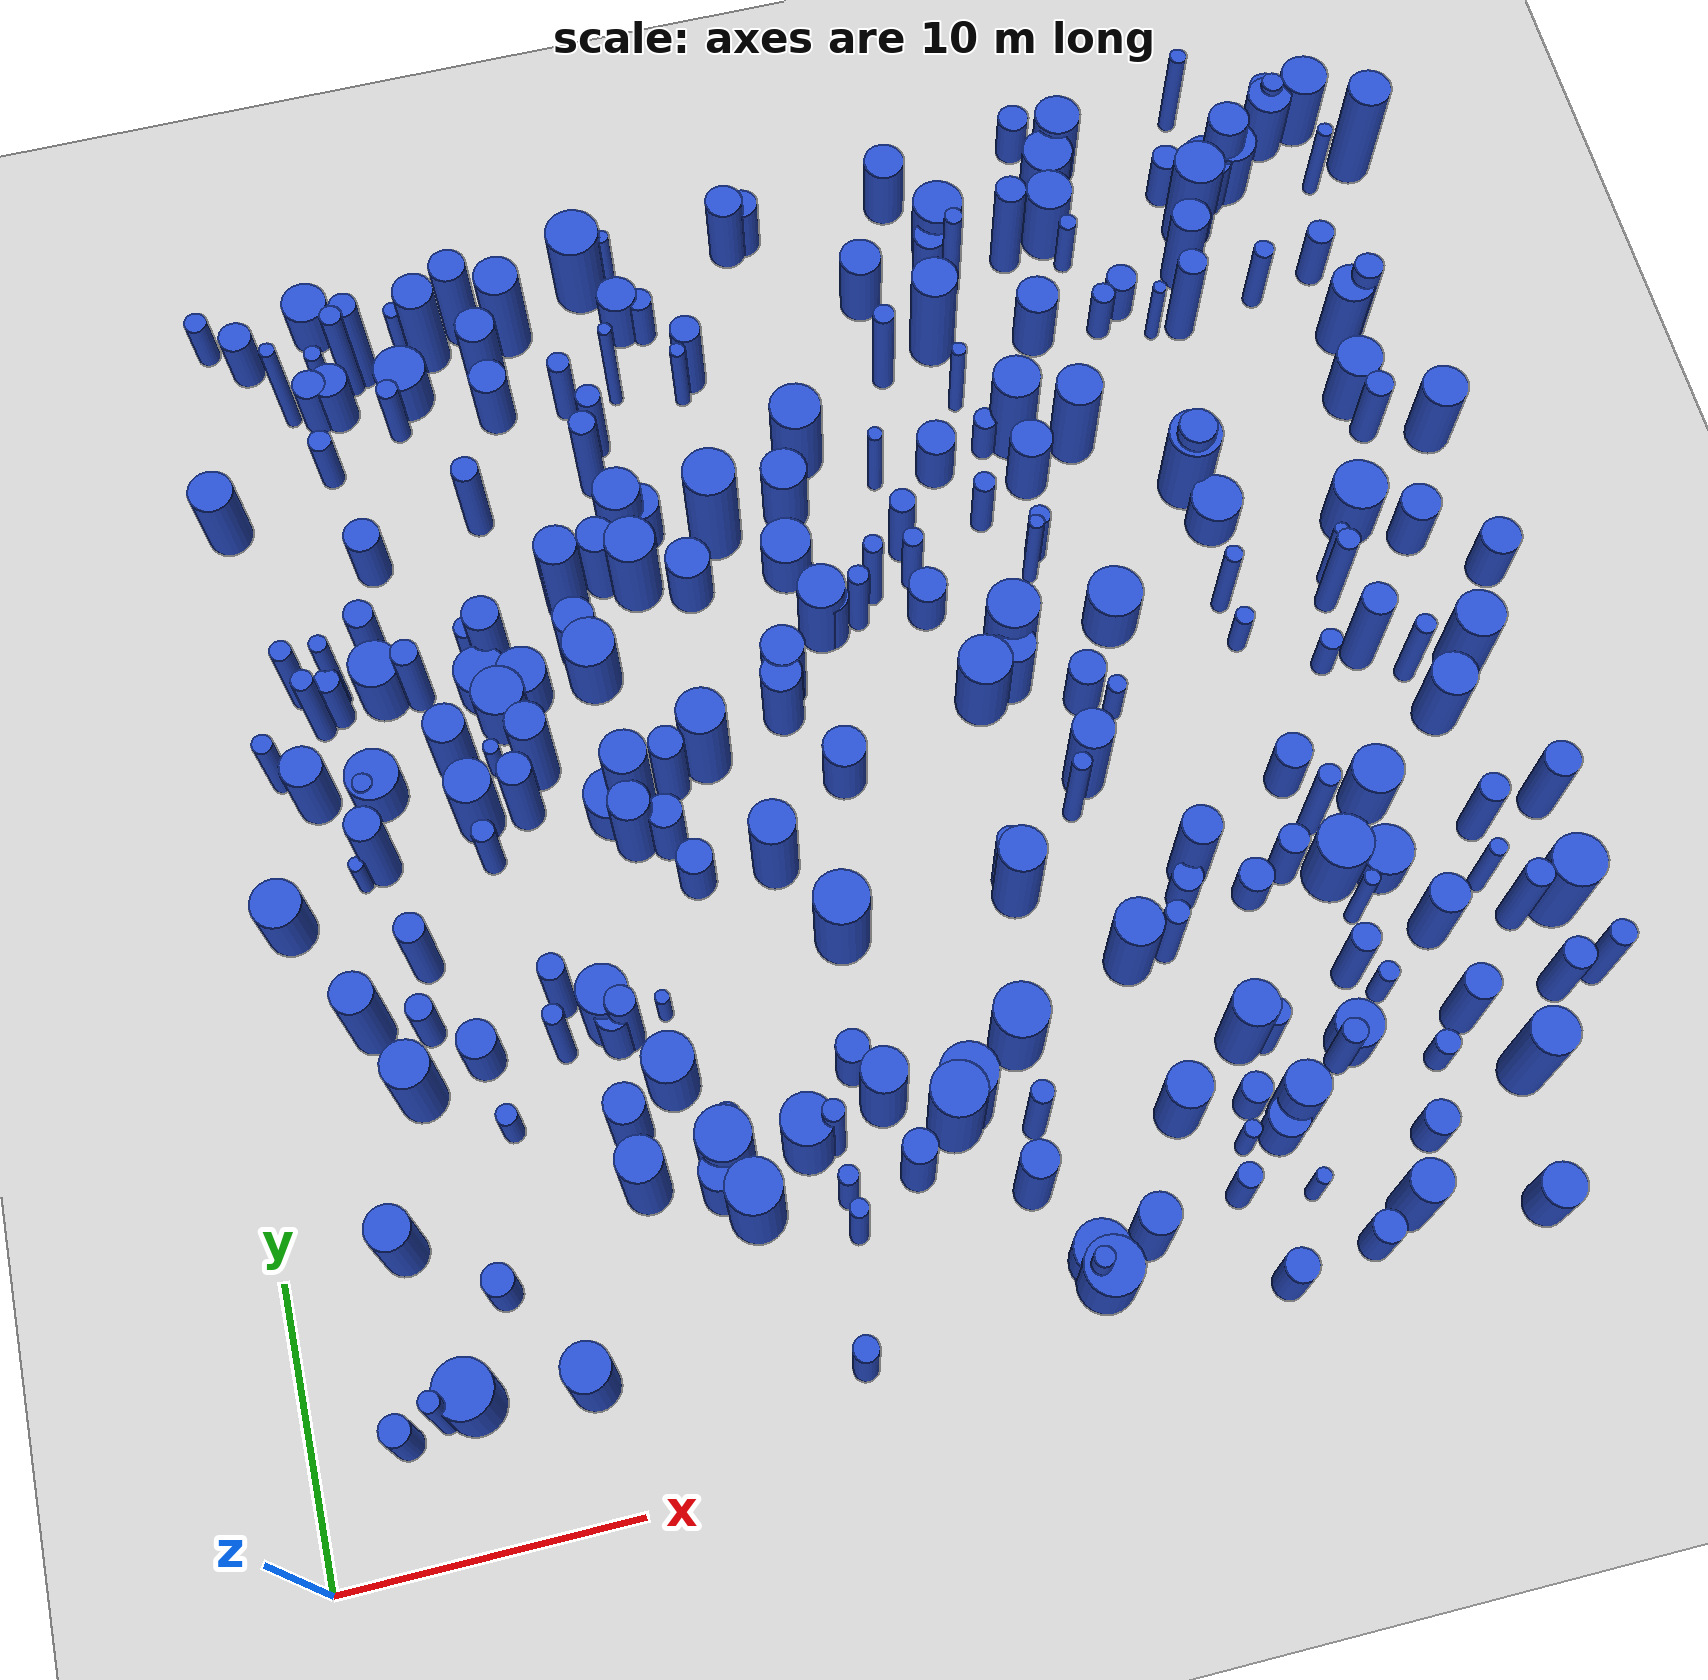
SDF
<sdf version="1.6">
 <world name="default">
  <light name="sun" type="directional">
   <pose>0 0 10 0 -0 0</pose>
   <diffuse>0.8 0.8 0.8 1</diffuse>
   <specular>0.1 0.1 0.1 1</specular>
   <attenuation>
    <range>1000</range>
    <constant>0.9</constant>
    <linear>0.01</linear>
    <quadratic>0.001</quadratic>
   </attenuation>
   <direction>-0.5 0.5 -1</direction>
  </light>
  <model name="ground_plane">
   <static>1</static>
   <link name="link">
    <collision name="collision">
     <geometry><plane><normal>0 0 1</normal><size>100 100</size></plane></geometry>
     <surface><friction><ode><mu>100</mu><mu2>50</mu2></ode></friction></surface>
    </collision>
    <visual name="visual">
     <cast_shadows>0</cast_shadows>
     <geometry><plane><normal>0 0 1</normal><size>100 100</size></plane></geometry>
     <material>
      <script><uri>file://media/materials/scripts/gazebo.material</uri><name>Gazebo/Grey</name></script>
     </material>
    </visual>
   </link>
  </model>
  <gravity>0 0 -9.8</gravity>
  <magnetic_field>6e-06 2.3e-05 -4.2e-05</magnetic_field>
  <atmosphere type="adiabatic"/>
  <physics name="default_physics" default="0" type="ode">
   <max_step_size>0.001</max_step_size>
   <real_time_factor>0.3</real_time_factor>
   <real_time_update_rate>1000</real_time_update_rate>
  </physics>
  <scene><ambient>0.4 0.4 0.4 1</ambient><background>0.7 0.7 0.7 1</background><shadows>1</shadows></scene>
  <spherical_coordinates>
   <surface_model>EARTH_WGS84</surface_model>
   <latitude_deg>0</latitude_deg>
   <longitude_deg>0</longitude_deg>
   <elevation>0</elevation>
   <heading_deg>0</heading_deg>
  </spherical_coordinates>
  <model name="0">
   <static>0</static>
   <link name="link">
    <inertial>
     <mass>2</mass>
     <inertia><ixx>3.55486</ixx><ixy>0</ixy><ixz>0</ixz><iyy>3.55486</iyy><iyz>0</iyz><izz>0.297884</izz></inertia>
    </inertial>
    <collision name="collision">
     <geometry><cylinder><length>4.52056</length><radius>0.545787</radius></cylinder></geometry>
     <surface><contact><collide_without_contact>0</collide_without_contact></contact></surface>
    </collision>
    <visual name="visual">
     <geometry><cylinder><length>4.52056</length><radius>0.545787</radius></cylinder></geometry>
     <material>
      <script><uri>file://media/materials/scripts/gazebo.material</uri><name>Gazebo/Blue</name></script>
     </material>
    </visual>
    <gravity>0</gravity>
   </link>
   <pose>38.7282 38.0226 2.26028 0 -0 0</pose>
  </model>
  <model name="1">
   <static>0</static>
   <link name="link">
    <inertial>
     <mass>2</mass>
     <inertia><ixx>3.81588</ixx><ixy>0</ixy><ixz>0</ixz><iyy>3.81588</iyy><iyz>0</iyz><izz>0.158534</izz></inertia>
    </inertial>
    <collision name="collision">
     <geometry><cylinder><length>4.73494</length><radius>0.398164</radius></cylinder></geometry>
     <surface><contact><collide_without_contact>0</collide_without_contact></contact></surface>
    </collision>
    <visual name="visual">
     <geometry><cylinder><length>4.73494</length><radius>0.398164</radius></cylinder></geometry>
     <material>
      <script><uri>file://media/materials/scripts/gazebo.material</uri><name>Gazebo/Blue</name></script>
     </material>
    </visual>
    <gravity>0</gravity>
   </link>
   <pose>37.3386 17.4202 2.36747 0 -0 0</pose>
  </model>
  <model name="2">
   <static>0</static>
   <link name="link">
    <inertial>
     <mass>2</mass>
     <inertia><ixx>1.55938</ixx><ixy>0</ixy><ixz>0</ixz><iyy>1.55938</iyy><iyz>0</iyz><izz>0.44286</izz></inertia>
    </inertial>
    <collision name="collision">
     <geometry><cylinder><length>2.83332</length><radius>0.665477</radius></cylinder></geometry>
     <surface><contact><collide_without_contact>0</collide_without_contact></contact></surface>
    </collision>
    <visual name="visual">
     <geometry><cylinder><length>2.83332</length><radius>0.665477</radius></cylinder></geometry>
     <material>
      <script><uri>file://media/materials/scripts/gazebo.material</uri><name>Gazebo/Blue</name></script>
     </material>
    </visual>
    <gravity>0</gravity>
   </link>
   <pose>30.9281 23.9603 1.41666 0 -0 0</pose>
  </model>
  <model name="3">
   <static>0</static>
   <link name="link">
    <inertial>
     <mass>2</mass>
     <inertia><ixx>1.79748</ixx><ixy>0</ixy><ixz>0</ixz><iyy>1.79748</iyy><iyz>0</iyz><izz>0.403289</izz></inertia>
    </inertial>
    <collision name="collision">
     <geometry><cylinder><length>3.09435</length><radius>0.635051</radius></cylinder></geometry>
     <surface><contact><collide_without_contact>0</collide_without_contact></contact></surface>
    </collision>
    <visual name="visual">
     <geometry><cylinder><length>3.09435</length><radius>0.635051</radius></cylinder></geometry>
     <material>
      <script><uri>file://media/materials/scripts/gazebo.material</uri><name>Gazebo/Blue</name></script>
     </material>
    </visual>
    <gravity>0</gravity>
   </link>
   <pose>44.145 45.8026 1.54718 0 -0 0</pose>
  </model>
  <model name="4">
   <static>0</static>
   <link name="link">
    <inertial>
     <mass>2</mass>
     <inertia><ixx>2.85473</ixx><ixy>0</ixy><ixz>0</ixz><iyy>2.85473</iyy><iyz>0</iyz><izz>0.620901</izz></inertia>
    </inertial>
    <collision name="collision">
     <geometry><cylinder><length>3.90714</length><radius>0.787973</radius></cylinder></geometry>
     <surface><contact><collide_without_contact>0</collide_without_contact></contact></surface>
    </collision>
    <visual name="visual">
     <geometry><cylinder><length>3.90714</length><radius>0.787973</radius></cylinder></geometry>
     <material>
      <script><uri>file://media/materials/scripts/gazebo.material</uri><name>Gazebo/Blue</name></script>
     </material>
    </visual>
    <gravity>0</gravity>
   </link>
   <pose>29.9206 8.51372 1.95357 0 -0 0</pose>
  </model>
  <model name="5">
   <static>0</static>
   <link name="link">
    <inertial>
     <mass>2</mass>
     <inertia><ixx>0.79305</ixx><ixy>0</ixy><ixz>0</ixz><iyy>0.79305</iyy><iyz>0</iyz><izz>0.186767</izz></inertia>
    </inertial>
    <collision name="collision">
     <geometry><cylinder><length>2.0489</length><radius>0.432165</radius></cylinder></geometry>
     <surface><contact><collide_without_contact>0</collide_without_contact></contact></surface>
    </collision>
    <visual name="visual">
     <geometry><cylinder><length>2.0489</length><radius>0.432165</radius></cylinder></geometry>
     <material>
      <script><uri>file://media/materials/scripts/gazebo.material</uri><name>Gazebo/Blue</name></script>
     </material>
    </visual>
    <gravity>0</gravity>
   </link>
   <pose>38.9921 8.31265 1.02445 0 -0 0</pose>
  </model>
  <model name="6">
   <static>0</static>
   <link name="link">
    <inertial>
     <mass>2</mass>
     <inertia><ixx>1.16849</ixx><ixy>0</ixy><ixz>0</ixz><iyy>1.16849</iyy><iyz>0</iyz><izz>0.30328</izz></inertia>
    </inertial>
    <collision name="collision">
     <geometry><cylinder><length>2.47004</length><radius>0.550708</radius></cylinder></geometry>
     <surface><contact><collide_without_contact>0</collide_without_contact></contact></surface>
    </collision>
    <visual name="visual">
     <geometry><cylinder><length>2.47004</length><radius>0.550708</radius></cylinder></geometry>
     <material>
      <script><uri>file://media/materials/scripts/gazebo.material</uri><name>Gazebo/Blue</name></script>
     </material>
    </visual>
    <gravity>0</gravity>
   </link>
   <pose>7.0052 7.97036 1.23502 0 -0 0</pose>
  </model>
  <model name="7">
   <static>0</static>
   <link name="link">
    <inertial>
     <mass>2</mass>
     <inertia><ixx>4.24686</ixx><ixy>0</ixy><ixz>0</ixz><iyy>4.24686</iyy><iyz>0</iyz><izz>0.171142</izz></inertia>
    </inertial>
    <collision name="collision">
     <geometry><cylinder><length>4.99677</length><radius>0.413693</radius></cylinder></geometry>
     <surface><contact><collide_without_contact>0</collide_without_contact></contact></surface>
    </collision>
    <visual name="visual">
     <geometry><cylinder><length>4.99677</length><radius>0.413693</radius></cylinder></geometry>
     <material>
      <script><uri>file://media/materials/scripts/gazebo.material</uri><name>Gazebo/Blue</name></script>
     </material>
    </visual>
    <gravity>0</gravity>
   </link>
   <pose>40.5992 25.5949 2.49839 0 -0 0</pose>
  </model>
  <model name="8">
   <static>0</static>
   <link name="link">
    <inertial>
     <mass>2</mass>
     <inertia><ixx>2.56634</ixx><ixy>0</ixy><ixz>0</ixz><iyy>2.56634</iyy><iyz>0</iyz><izz>0.222806</izz></inertia>
    </inertial>
    <collision name="collision">
     <geometry><cylinder><length>3.83792</length><radius>0.472024</radius></cylinder></geometry>
     <surface><contact><collide_without_contact>0</collide_without_contact></contact></surface>
    </collision>
    <visual name="visual">
     <geometry><cylinder><length>3.83792</length><radius>0.472024</radius></cylinder></geometry>
     <material>
      <script><uri>file://media/materials/scripts/gazebo.material</uri><name>Gazebo/Blue</name></script>
     </material>
    </visual>
    <gravity>0</gravity>
   </link>
   <pose>26.1172 31.3274 1.91896 0 -0 0</pose>
  </model>
  <model name="9">
   <static>0</static>
   <link name="link">
    <inertial>
     <mass>2</mass>
     <inertia><ixx>2.49906</ixx><ixy>0</ixy><ixz>0</ixz><iyy>2.49906</iyy><iyz>0</iyz><izz>0.95958</izz></inertia>
    </inertial>
    <collision name="collision">
     <geometry><cylinder><length>3.48075</length><radius>0.979581</radius></cylinder></geometry>
     <surface><contact><collide_without_contact>0</collide_without_contact></contact></surface>
    </collision>
    <visual name="visual">
     <geometry><cylinder><length>3.48075</length><radius>0.979581</radius></cylinder></geometry>
     <material>
      <script><uri>file://media/materials/scripts/gazebo.material</uri><name>Gazebo/Blue</name></script>
     </material>
    </visual>
    <gravity>0</gravity>
   </link>
   <pose>37.4825 15.4558 1.74037 0 -0 0</pose>
  </model>
  <model name="10">
   <static>0</static>
   <link name="link">
    <inertial>
     <mass>2</mass>
     <inertia><ixx>2.47867</ixx><ixy>0</ixy><ixz>0</ixz><iyy>2.47867</iyy><iyz>0</iyz><izz>0.684649</izz></inertia>
    </inertial>
    <collision name="collision">
     <geometry><cylinder><length>3.58024</length><radius>0.827435</radius></cylinder></geometry>
     <surface><contact><collide_without_contact>0</collide_without_contact></contact></surface>
    </collision>
    <visual name="visual">
     <geometry><cylinder><length>3.58024</length><radius>0.827435</radius></cylinder></geometry>
     <material>
      <script><uri>file://media/materials/scripts/gazebo.material</uri><name>Gazebo/Blue</name></script>
     </material>
    </visual>
    <gravity>0</gravity>
   </link>
   <pose>43.0104 20.4105 1.79012 0 -0 0</pose>
  </model>
  <model name="11">
   <static>0</static>
   <link name="link">
    <inertial>
     <mass>2</mass>
     <inertia><ixx>1.48597</ixx><ixy>0</ixy><ixz>0</ixz><iyy>1.48597</iyy><iyz>0</iyz><izz>0.264549</izz></inertia>
    </inertial>
    <collision name="collision">
     <geometry><cylinder><length>2.84994</length><radius>0.514344</radius></cylinder></geometry>
     <surface><contact><collide_without_contact>0</collide_without_contact></contact></surface>
    </collision>
    <visual name="visual">
     <geometry><cylinder><length>2.84994</length><radius>0.514344</radius></cylinder></geometry>
     <material>
      <script><uri>file://media/materials/scripts/gazebo.material</uri><name>Gazebo/Blue</name></script>
     </material>
    </visual>
    <gravity>0</gravity>
   </link>
   <pose>44.2752 39.1553 1.42497 0 -0 0</pose>
  </model>
  <model name="12">
   <static>0</static>
   <link name="link">
    <inertial>
     <mass>2</mass>
     <inertia><ixx>1.27619</ixx><ixy>0</ixy><ixz>0</ixz><iyy>1.27619</iyy><iyz>0</iyz><izz>0.925435</izz></inertia>
    </inertial>
    <collision name="collision">
     <geometry><cylinder><length>2.20927</length><radius>0.961995</radius></cylinder></geometry>
     <surface><contact><collide_without_contact>0</collide_without_contact></contact></surface>
    </collision>
    <visual name="visual">
     <geometry><cylinder><length>2.20927</length><radius>0.961995</radius></cylinder></geometry>
     <material>
      <script><uri>file://media/materials/scripts/gazebo.material</uri><name>Gazebo/Blue</name></script>
     </material>
    </visual>
    <gravity>0</gravity>
   </link>
   <pose>5.95857 26.1958 1.10463 0 -0 0</pose>
  </model>
  <model name="13">
   <static>0</static>
   <link name="link">
    <inertial>
     <mass>2</mass>
     <inertia><ixx>1.38583</ixx><ixy>0</ixy><ixz>0</ixz><iyy>1.38583</iyy><iyz>0</iyz><izz>0.558637</izz></inertia>
    </inertial>
    <collision name="collision">
     <geometry><cylinder><length>2.57664</length><radius>0.74742</radius></cylinder></geometry>
     <surface><contact><collide_without_contact>0</collide_without_contact></contact></surface>
    </collision>
    <visual name="visual">
     <geometry><cylinder><length>2.57664</length><radius>0.74742</radius></cylinder></geometry>
     <material>
      <script><uri>file://media/materials/scripts/gazebo.material</uri><name>Gazebo/Blue</name></script>
     </material>
    </visual>
    <gravity>0</gravity>
   </link>
   <pose>18.0491 42.9507 1.28832 0 -0 0</pose>
  </model>
  <model name="14">
   <static>0</static>
   <link name="link">
    <inertial>
     <mass>2</mass>
     <inertia>
      <ixx>0.836303</ixx>
      <ixy>0</ixy>
      <ixz>0</ixz>
      <iyy>0.836303</iyy>
      <iyz>0</iyz>
      <izz>0.0702342</izz>
     </inertia>
    </inertial>
    <collision name="collision">
     <geometry><cylinder><length>2.19251</length><radius>0.265017</radius></cylinder></geometry>
     <surface><contact><collide_without_contact>0</collide_without_contact></contact></surface>
    </collision>
    <visual name="visual">
     <geometry><cylinder><length>2.19251</length><radius>0.265017</radius></cylinder></geometry>
     <material>
      <script><uri>file://media/materials/scripts/gazebo.material</uri><name>Gazebo/Blue</name></script>
     </material>
    </visual>
    <gravity>0</gravity>
   </link>
   <pose>4.90241 23.0543 1.09626 0 -0 0</pose>
  </model>
  <model name="15">
   <static>0</static>
   <link name="link">
    <inertial>
     <mass>2</mass>
     <inertia><ixx>1.70661</ixx><ixy>0</ixy><ixz>0</ixz><iyy>1.70661</iyy><iyz>0</iyz><izz>0.956436</izz></inertia>
    </inertial>
    <collision name="collision">
     <geometry><cylinder><length>2.71484</length><radius>0.977976</radius></cylinder></geometry>
     <surface><contact><collide_without_contact>0</collide_without_contact></contact></surface>
    </collision>
    <visual name="visual">
     <geometry><cylinder><length>2.71484</length><radius>0.977976</radius></cylinder></geometry>
     <material>
      <script><uri>file://media/materials/scripts/gazebo.material</uri><name>Gazebo/Blue</name></script>
     </material>
    </visual>
    <gravity>0</gravity>
   </link>
   <pose>41.1423 43.5016 1.35742 0 -0 0</pose>
  </model>
  <model name="16">
   <static>0</static>
   <link name="link">
    <inertial>
     <mass>2</mass>
     <inertia><ixx>1.52106</ixx><ixy>0</ixy><ixz>0</ixz><iyy>1.52106</iyy><iyz>0</iyz><izz>0.42879</izz></inertia>
    </inertial>
    <collision name="collision">
     <geometry><cylinder><length>2.8</length><radius>0.65482</radius></cylinder></geometry>
     <surface><contact><collide_without_contact>0</collide_without_contact></contact></surface>
    </collision>
    <visual name="visual">
     <geometry><cylinder><length>2.8</length><radius>0.65482</radius></cylinder></geometry>
     <material>
      <script><uri>file://media/materials/scripts/gazebo.material</uri><name>Gazebo/Blue</name></script>
     </material>
    </visual>
    <gravity>0</gravity>
   </link>
   <pose>36.9714 19.2595 1.4 0 -0 0</pose>
  </model>
  <model name="17">
   <static>0</static>
   <link name="link">
    <inertial>
     <mass>2</mass>
     <inertia><ixx>2.36762</ixx><ixy>0</ixy><ixz>0</ixz><iyy>2.36762</iyy><iyz>0</iyz><izz>0.56369</izz></inertia>
    </inertial>
    <collision name="collision">
     <geometry><cylinder><length>3.53761</length><radius>0.750793</radius></cylinder></geometry>
     <surface><contact><collide_without_contact>0</collide_without_contact></contact></surface>
    </collision>
    <visual name="visual">
     <geometry><cylinder><length>3.53761</length><radius>0.750793</radius></cylinder></geometry>
     <material>
      <script><uri>file://media/materials/scripts/gazebo.material</uri><name>Gazebo/Blue</name></script>
     </material>
    </visual>
    <gravity>0</gravity>
   </link>
   <pose>3.8069 26.4539 1.7688 0 -0 0</pose>
  </model>
  <model name="18">
   <static>0</static>
   <link name="link">
    <inertial>
     <mass>2</mass>
     <inertia><ixx>2.27941</ixx><ixy>0</ixy><ixz>0</ixz><iyy>2.27941</iyy><iyz>0</iyz><izz>0.900366</izz></inertia>
    </inertial>
    <collision name="collision">
     <geometry><cylinder><length>3.31291</length><radius>0.948876</radius></cylinder></geometry>
     <surface><contact><collide_without_contact>0</collide_without_contact></contact></surface>
    </collision>
    <visual name="visual">
     <geometry><cylinder><length>3.31291</length><radius>0.948876</radius></cylinder></geometry>
     <material>
      <script><uri>file://media/materials/scripts/gazebo.material</uri><name>Gazebo/Blue</name></script>
     </material>
    </visual>
    <gravity>0</gravity>
   </link>
   <pose>35.1638 44.8172 1.65646 0 -0 0</pose>
  </model>
  <model name="19">
   <static>0</static>
   <link name="link">
    <inertial>
     <mass>2</mass>
     <inertia><ixx>1.67962</ixx><ixy>0</ixy><ixz>0</ixz><iyy>1.67962</iyy><iyz>0</iyz><izz>0.646256</izz></inertia>
    </inertial>
    <collision name="collision">
     <geometry><cylinder><length>2.85288</length><radius>0.803901</radius></cylinder></geometry>
     <surface><contact><collide_without_contact>0</collide_without_contact></contact></surface>
    </collision>
    <visual name="visual">
     <geometry><cylinder><length>2.85288</length><radius>0.803901</radius></cylinder></geometry>
     <material>
      <script><uri>file://media/materials/scripts/gazebo.material</uri><name>Gazebo/Blue</name></script>
     </material>
    </visual>
    <gravity>0</gravity>
   </link>
   <pose>18.2862 31.439 1.42644 0 -0 0</pose>
  </model>
  <model name="20">
   <static>0</static>
   <link name="link">
    <inertial>
     <mass>2</mass>
     <inertia><ixx>2.82224</ixx><ixy>0</ixy><ixz>0</ixz><iyy>2.82224</iyy><iyz>0</iyz><izz>0.140236</izz></inertia>
    </inertial>
    <collision name="collision">
     <geometry><cylinder><length>4.06358</length><radius>0.374481</radius></cylinder></geometry>
     <surface><contact><collide_without_contact>0</collide_without_contact></contact></surface>
    </collision>
    <visual name="visual">
     <geometry><cylinder><length>4.06358</length><radius>0.374481</radius></cylinder></geometry>
     <material>
      <script><uri>file://media/materials/scripts/gazebo.material</uri><name>Gazebo/Blue</name></script>
     </material>
    </visual>
    <gravity>0</gravity>
   </link>
   <pose>42.4835 22.2448 2.03179 0 -0 0</pose>
  </model>
  <model name="21">
   <static>0</static>
   <link name="link">
    <inertial>
     <mass>2</mass>
     <inertia><ixx>3.48031</ixx><ixy>0</ixy><ixz>0</ixz><iyy>3.48031</iyy><iyz>0</iyz><izz>0.247758</izz></inertia>
    </inertial>
    <collision name="collision">
     <geometry><cylinder><length>4.4876</length><radius>0.497753</radius></cylinder></geometry>
     <surface><contact><collide_without_contact>0</collide_without_contact></contact></surface>
    </collision>
    <visual name="visual">
     <geometry><cylinder><length>4.4876</length><radius>0.497753</radius></cylinder></geometry>
     <material>
      <script><uri>file://media/materials/scripts/gazebo.material</uri><name>Gazebo/Blue</name></script>
     </material>
    </visual>
    <gravity>0</gravity>
   </link>
   <pose>43.0951 12.5325 2.2438 0 -0 0</pose>
  </model>
  <model name="22">
   <static>0</static>
   <link name="link">
    <inertial>
     <mass>2</mass>
     <inertia><ixx>1.84413</ixx><ixy>0</ixy><ixz>0</ixz><iyy>1.84413</iyy><iyz>0</iyz><izz>0.585229</izz></inertia>
    </inertial>
    <collision name="collision">
     <geometry><cylinder><length>3.05108</length><radius>0.765002</radius></cylinder></geometry>
     <surface><contact><collide_without_contact>0</collide_without_contact></contact></surface>
    </collision>
    <visual name="visual">
     <geometry><cylinder><length>3.05108</length><radius>0.765002</radius></cylinder></geometry>
     <material>
      <script><uri>file://media/materials/scripts/gazebo.material</uri><name>Gazebo/Blue</name></script>
     </material>
    </visual>
    <gravity>0</gravity>
   </link>
   <pose>29.0774 45.9975 1.52554 0 -0 0</pose>
  </model>
  <model name="23">
   <static>0</static>
   <link name="link">
    <inertial>
     <mass>2</mass>
     <inertia><ixx>3.02897</ixx><ixy>0</ixy><ixz>0</ixz><iyy>3.02897</iyy><iyz>0</iyz><izz>0.799249</izz></inertia>
    </inertial>
    <collision name="collision">
     <geometry><cylinder><length>3.97191</length><radius>0.894007</radius></cylinder></geometry>
     <surface><contact><collide_without_contact>0</collide_without_contact></contact></surface>
    </collision>
    <visual name="visual">
     <geometry><cylinder><length>3.97191</length><radius>0.894007</radius></cylinder></geometry>
     <material>
      <script><uri>file://media/materials/scripts/gazebo.material</uri><name>Gazebo/Blue</name></script>
     </material>
    </visual>
    <gravity>0</gravity>
   </link>
   <pose>44.5026 22.2198 1.98596 0 -0 0</pose>
  </model>
  <model name="24">
   <static>0</static>
   <link name="link">
    <inertial>
     <mass>2</mass>
     <inertia><ixx>2.07239</ixx><ixy>0</ixy><ixz>0</ixz><iyy>2.07239</iyy><iyz>0</iyz><izz>0.74145</izz></inertia>
    </inertial>
    <collision name="collision">
     <geometry><cylinder><length>3.19531</length><radius>0.861075</radius></cylinder></geometry>
     <surface><contact><collide_without_contact>0</collide_without_contact></contact></surface>
    </collision>
    <visual name="visual">
     <geometry><cylinder><length>3.19531</length><radius>0.861075</radius></cylinder></geometry>
     <material>
      <script><uri>file://media/materials/scripts/gazebo.material</uri><name>Gazebo/Blue</name></script>
     </material>
    </visual>
    <gravity>0</gravity>
   </link>
   <pose>43.9047 33.4741 1.59766 0 -0 0</pose>
  </model>
  <model name="25">
   <static>0</static>
   <link name="link">
    <inertial>
     <mass>2</mass>
     <inertia><ixx>2.06566</ixx><ixy>0</ixy><ixz>0</ixz><iyy>2.06566</iyy><iyz>0</iyz><izz>0.169636</izz></inertia>
    </inertial>
    <collision name="collision">
     <geometry><cylinder><length>3.44747</length><radius>0.411869</radius></cylinder></geometry>
     <surface><contact><collide_without_contact>0</collide_without_contact></contact></surface>
    </collision>
    <visual name="visual">
     <geometry><cylinder><length>3.44747</length><radius>0.411869</radius></cylinder></geometry>
     <material>
      <script><uri>file://media/materials/scripts/gazebo.material</uri><name>Gazebo/Blue</name></script>
     </material>
    </visual>
    <gravity>0</gravity>
   </link>
   <pose>44.3259 45.7116 1.72374 0 -0 0</pose>
  </model>
  <model name="26">
   <static>0</static>
   <link name="link">
    <inertial>
     <mass>2</mass>
     <inertia><ixx>1.40947</ixx><ixy>0</ixy><ixz>0</ixz><iyy>1.40947</iyy><iyz>0</iyz><izz>0.829551</izz></inertia>
    </inertial>
    <collision name="collision">
     <geometry><cylinder><length>2.44298</length><radius>0.910797</radius></cylinder></geometry>
     <surface><contact><collide_without_contact>0</collide_without_contact></contact></surface>
    </collision>
    <visual name="visual">
     <geometry><cylinder><length>2.44298</length><radius>0.910797</radius></cylinder></geometry>
     <material>
      <script><uri>file://media/materials/scripts/gazebo.material</uri><name>Gazebo/Blue</name></script>
     </material>
    </visual>
    <gravity>0</gravity>
   </link>
   <pose>21.8699 31.4897 1.22149 0 -0 0</pose>
  </model>
  <model name="27">
   <static>0</static>
   <link name="link">
    <inertial>
     <mass>2</mass>
     <inertia><ixx>2.58788</ixx><ixy>0</ixy><ixz>0</ixz><iyy>2.58788</iyy><iyz>0</iyz><izz>0.212332</izz></inertia>
    </inertial>
    <collision name="collision">
     <geometry><cylinder><length>3.85879</length><radius>0.460795</radius></cylinder></geometry>
     <surface><contact><collide_without_contact>0</collide_without_contact></contact></surface>
    </collision>
    <visual name="visual">
     <geometry><cylinder><length>3.85879</length><radius>0.460795</radius></cylinder></geometry>
     <material>
      <script><uri>file://media/materials/scripts/gazebo.material</uri><name>Gazebo/Blue</name></script>
     </material>
    </visual>
    <gravity>0</gravity>
   </link>
   <pose>16.1431 38.1561 1.92939 0 -0 0</pose>
  </model>
  <model name="28">
   <static>0</static>
   <link name="link">
    <inertial>
     <mass>2</mass>
     <inertia><ixx>1.94852</ixx><ixy>0</ixy><ixz>0</ixz><iyy>1.94852</iyy><iyz>0</iyz><izz>0.176047</izz></inertia>
    </inertial>
    <collision name="collision">
     <geometry><cylinder><length>3.3411</length><radius>0.41958</radius></cylinder></geometry>
     <surface><contact><collide_without_contact>0</collide_without_contact></contact></surface>
    </collision>
    <visual name="visual">
     <geometry><cylinder><length>3.3411</length><radius>0.41958</radius></cylinder></geometry>
     <material>
      <script><uri>file://media/materials/scripts/gazebo.material</uri><name>Gazebo/Blue</name></script>
     </material>
    </visual>
    <gravity>0</gravity>
   </link>
   <pose>14.7068 10.6265 1.67055 0 -0 0</pose>
  </model>
  <model name="29">
   <static>0</static>
   <link name="link">
    <inertial>
     <mass>2</mass>
     <inertia><ixx>2.40213</ixx><ixy>0</ixy><ixz>0</ixz><iyy>2.40213</iyy><iyz>0</iyz><izz>0.316267</izz></inertia>
    </inertial>
    <collision name="collision">
     <geometry><cylinder><length>3.66933</length><radius>0.562376</radius></cylinder></geometry>
     <surface><contact><collide_without_contact>0</collide_without_contact></contact></surface>
    </collision>
    <visual name="visual">
     <geometry><cylinder><length>3.66933</length><radius>0.562376</radius></cylinder></geometry>
     <material>
      <script><uri>file://media/materials/scripts/gazebo.material</uri><name>Gazebo/Blue</name></script>
     </material>
    </visual>
    <gravity>0</gravity>
   </link>
   <pose>43.713 9.80193 1.83467 0 -0 0</pose>
  </model>
  <model name="30">
   <static>0</static>
   <link name="link">
    <inertial>
     <mass>2</mass>
     <inertia>
      <ixx>0.948335</ixx>
      <ixy>0</ixy>
      <ixz>0</ixz>
      <iyy>0.948335</iyy>
      <iyz>0</iyz>
      <izz>0.118719</izz>
     </inertia>
    </inertial>
    <collision name="collision">
     <geometry><cylinder><length>2.30951</length><radius>0.344557</radius></cylinder></geometry>
     <surface><contact><collide_without_contact>0</collide_without_contact></contact></surface>
    </collision>
    <visual name="visual">
     <geometry><cylinder><length>2.30951</length><radius>0.344557</radius></cylinder></geometry>
     <material>
      <script><uri>file://media/materials/scripts/gazebo.material</uri><name>Gazebo/Blue</name></script>
     </material>
    </visual>
    <gravity>0</gravity>
   </link>
   <pose>36.9819 24.7904 1.15476 0 -0 0</pose>
  </model>
  <model name="31">
   <static>0</static>
   <link name="link">
    <inertial>
     <mass>2</mass>
     <inertia><ixx>4.54322</ixx><ixy>0</ixy><ixz>0</ixz><iyy>4.54322</iyy><iyz>0</iyz><izz>0.904882</izz></inertia>
    </inertial>
    <collision name="collision">
     <geometry><cylinder><length>4.95426</length><radius>0.951253</radius></cylinder></geometry>
     <surface><contact><collide_without_contact>0</collide_without_contact></contact></surface>
    </collision>
    <visual name="visual">
     <geometry><cylinder><length>4.95426</length><radius>0.951253</radius></cylinder></geometry>
     <material>
      <script><uri>file://media/materials/scripts/gazebo.material</uri><name>Gazebo/Blue</name></script>
     </material>
    </visual>
    <gravity>0</gravity>
   </link>
   <pose>19.6267 33.4845 2.47713 0 -0 0</pose>
  </model>
  <model name="32">
   <static>0</static>
   <link name="link">
    <inertial>
     <mass>2</mass>
     <inertia><ixx>3.14804</ixx><ixy>0</ixy><ixz>0</ixz><iyy>3.14804</iyy><iyz>0</iyz><izz>0.2772</izz></inertia>
    </inertial>
    <collision name="collision">
     <geometry><cylinder><length>4.24931</length><radius>0.526498</radius></cylinder></geometry>
     <surface><contact><collide_without_contact>0</collide_without_contact></contact></surface>
    </collision>
    <visual name="visual">
     <geometry><cylinder><length>4.24931</length><radius>0.526498</radius></cylinder></geometry>
     <material>
      <script><uri>file://media/materials/scripts/gazebo.material</uri><name>Gazebo/Blue</name></script>
     </material>
    </visual>
    <gravity>0</gravity>
   </link>
   <pose>12.684 15.5314 2.12466 0 -0 0</pose>
  </model>
  <model name="33">
   <static>0</static>
   <link name="link">
    <inertial>
     <mass>2</mass>
     <inertia><ixx>2.44196</ixx><ixy>0</ixy><ixz>0</ixz><iyy>2.44196</iyy><iyz>0</iyz><izz>0.187757</izz></inertia>
    </inertial>
    <collision name="collision">
     <geometry><cylinder><length>3.75347</length><radius>0.43331</radius></cylinder></geometry>
     <surface><contact><collide_without_contact>0</collide_without_contact></contact></surface>
    </collision>
    <visual name="visual">
     <geometry><cylinder><length>3.75347</length><radius>0.43331</radius></cylinder></geometry>
     <material>
      <script><uri>file://media/materials/scripts/gazebo.material</uri><name>Gazebo/Blue</name></script>
     </material>
    </visual>
    <gravity>0</gravity>
   </link>
   <pose>35.6788 9.00993 1.87673 0 -0 0</pose>
  </model>
  <model name="34">
   <static>0</static>
   <link name="link">
    <inertial>
     <mass>2</mass>
     <inertia><ixx>1.29833</ixx><ixy>0</ixy><ixz>0</ixz><iyy>1.29833</iyy><iyz>0</iyz><izz>0.714199</izz></inertia>
    </inertial>
    <collision name="collision">
     <geometry><cylinder><length>2.37642</length><radius>0.845103</radius></cylinder></geometry>
     <surface><contact><collide_without_contact>0</collide_without_contact></contact></surface>
    </collision>
    <visual name="visual">
     <geometry><cylinder><length>2.37642</length><radius>0.845103</radius></cylinder></geometry>
     <material>
      <script><uri>file://media/materials/scripts/gazebo.material</uri><name>Gazebo/Blue</name></script>
     </material>
    </visual>
    <gravity>0</gravity>
   </link>
   <pose>36.2733 9.54869 1.18821 0 -0 0</pose>
  </model>
  <model name="35">
   <static>0</static>
   <link name="link">
    <inertial>
     <mass>2</mass>
     <inertia><ixx>1.28734</ixx><ixy>0</ixy><ixz>0</ixz><iyy>1.28734</iyy><iyz>0</iyz><izz>0.926556</izz></inertia>
    </inertial>
    <collision name="collision">
     <geometry><cylinder><length>2.22359</length><radius>0.962578</radius></cylinder></geometry>
     <surface><contact><collide_without_contact>0</collide_without_contact></contact></surface>
    </collision>
    <visual name="visual">
     <geometry><cylinder><length>2.22359</length><radius>0.962578</radius></cylinder></geometry>
     <material>
      <script><uri>file://media/materials/scripts/gazebo.material</uri><name>Gazebo/Blue</name></script>
     </material>
    </visual>
    <gravity>0</gravity>
   </link>
   <pose>25.9919 4.41635 1.11179 0 -0 0</pose>
  </model>
  <model name="36">
   <static>0</static>
   <link name="link">
    <inertial>
     <mass>2</mass>
     <inertia><ixx>1.15813</ixx><ixy>0</ixy><ixz>0</ixz><iyy>1.15813</iyy><iyz>0</iyz><izz>0.18494</izz></inertia>
    </inertial>
    <collision name="collision">
     <geometry><cylinder><length>2.52863</length><radius>0.430047</radius></cylinder></geometry>
     <surface><contact><collide_without_contact>0</collide_without_contact></contact></surface>
    </collision>
    <visual name="visual">
     <geometry><cylinder><length>2.52863</length><radius>0.430047</radius></cylinder></geometry>
     <material>
      <script><uri>file://media/materials/scripts/gazebo.material</uri><name>Gazebo/Blue</name></script>
     </material>
    </visual>
    <gravity>0</gravity>
   </link>
   <pose>35.7021 38.6987 1.26432 0 -0 0</pose>
  </model>
  <model name="37">
   <static>0</static>
   <link name="link">
    <inertial>
     <mass>2</mass>
     <inertia><ixx>3.10226</ixx><ixy>0</ixy><ixz>0</ixz><iyy>3.10226</iyy><iyz>0</iyz><izz>0.951705</izz></inertia>
    </inertial>
    <collision name="collision">
     <geometry><cylinder><length>3.96969</length><radius>0.975554</radius></cylinder></geometry>
     <surface><contact><collide_without_contact>0</collide_without_contact></contact></surface>
    </collision>
    <visual name="visual">
     <geometry><cylinder><length>3.96969</length><radius>0.975554</radius></cylinder></geometry>
     <material>
      <script><uri>file://media/materials/scripts/gazebo.material</uri><name>Gazebo/Blue</name></script>
     </material>
    </visual>
    <gravity>0</gravity>
   </link>
   <pose>36.9478 31.4151 1.98485 0 -0 0</pose>
  </model>
  <model name="38">
   <static>0</static>
   <link name="link">
    <inertial>
     <mass>2</mass>
     <inertia>
      <ixx>0.928398</ixx>
      <ixy>0</ixy>
      <ixz>0</ixz>
      <iyy>0.928398</iyy>
      <iyz>0</iyz>
      <izz>0.123325</izz>
     </inertia>
    </inertial>
    <collision name="collision">
     <geometry><cylinder><length>2.28044</length><radius>0.351177</radius></cylinder></geometry>
     <surface><contact><collide_without_contact>0</collide_without_contact></contact></surface>
    </collision>
    <visual name="visual">
     <geometry><cylinder><length>2.28044</length><radius>0.351177</radius></cylinder></geometry>
     <material>
      <script><uri>file://media/materials/scripts/gazebo.material</uri><name>Gazebo/Blue</name></script>
     </material>
    </visual>
    <gravity>0</gravity>
   </link>
   <pose>5.59868 25.9297 1.14022 0 -0 0</pose>
  </model>
  <model name="39">
   <static>0</static>
   <link name="link">
    <inertial>
     <mass>2</mass>
     <inertia>
      <ixx>0.895212</ixx>
      <ixy>0</ixy>
      <ixz>0</ixz>
      <iyy>0.895212</iyy>
      <iyz>0</iyz>
      <izz>0.162805</izz>
     </inertia>
    </inertial>
    <collision name="collision">
     <geometry><cylinder><length>2.20972</length><radius>0.403491</radius></cylinder></geometry>
     <surface><contact><collide_without_contact>0</collide_without_contact></contact></surface>
    </collision>
    <visual name="visual">
     <geometry><cylinder><length>2.20972</length><radius>0.403491</radius></cylinder></geometry>
     <material>
      <script><uri>file://media/materials/scripts/gazebo.material</uri><name>Gazebo/Blue</name></script>
     </material>
    </visual>
    <gravity>0</gravity>
   </link>
   <pose>39.7052 23.2253 1.10486 0 -0 0</pose>
  </model>
  <model name="40">
   <static>0</static>
   <link name="link">
    <inertial>
     <mass>2</mass>
     <inertia><ixx>2.63983</ixx><ixy>0</ixy><ixz>0</ixz><iyy>2.63983</iyy><iyz>0</iyz><izz>0.666975</izz></inertia>
    </inertial>
    <collision name="collision">
     <geometry><cylinder><length>3.71996</length><radius>0.816686</radius></cylinder></geometry>
     <surface><contact><collide_without_contact>0</collide_without_contact></contact></surface>
    </collision>
    <visual name="visual">
     <geometry><cylinder><length>3.71996</length><radius>0.816686</radius></cylinder></geometry>
     <material>
      <script><uri>file://media/materials/scripts/gazebo.material</uri><name>Gazebo/Blue</name></script>
     </material>
    </visual>
    <gravity>0</gravity>
   </link>
   <pose>9.25913 4.38919 1.85998 0 -0 0</pose>
  </model>
  <model name="41">
   <static>0</static>
   <link name="link">
    <inertial>
     <mass>2</mass>
     <inertia><ixx>4.24794</ixx><ixy>0</ixy><ixz>0</ixz><iyy>4.24794</iyy><iyz>0</iyz><izz>0.162608</izz></inertia>
    </inertial>
    <collision name="collision">
     <geometry><cylinder><length>4.99998</length><radius>0.403246</radius></cylinder></geometry>
     <surface><contact><collide_without_contact>0</collide_without_contact></contact></surface>
    </collision>
    <visual name="visual">
     <geometry><cylinder><length>4.99998</length><radius>0.403246</radius></cylinder></geometry>
     <material>
      <script><uri>file://media/materials/scripts/gazebo.material</uri><name>Gazebo/Blue</name></script>
     </material>
    </visual>
    <gravity>0</gravity>
   </link>
   <pose>7.77155 42.938 2.49999 0 -0 0</pose>
  </model>
  <model name="42">
   <static>0</static>
   <link name="link">
    <inertial>
     <mass>2</mass>
     <inertia>
      <ixx>4.19788</ixx>
      <ixy>0</ixy>
      <ixz>0</ixz>
      <iyy>4.19788</iyy>
      <iyz>0</iyz>
      <izz>0.0844153</izz>
     </inertia>
    </inertial>
    <collision name="collision">
     <geometry><cylinder><length>4.9934</length><radius>0.290543</radius></cylinder></geometry>
     <surface><contact><collide_without_contact>0</collide_without_contact></contact></surface>
    </collision>
    <visual name="visual">
     <geometry><cylinder><length>4.9934</length><radius>0.290543</radius></cylinder></geometry>
     <material>
      <script><uri>file://media/materials/scripts/gazebo.material</uri><name>Gazebo/Blue</name></script>
     </material>
    </visual>
    <gravity>0</gravity>
   </link>
   <pose>5.32712 42.0448 2.4967 0 -0 0</pose>
  </model>
  <model name="43">
   <static>0</static>
   <link name="link">
    <inertial>
     <mass>2</mass>
     <inertia><ixx>1.11898</ixx><ixy>0</ixy><ixz>0</ixz><iyy>1.11898</iyy><iyz>0</iyz><izz>0.887933</izz></inertia>
    </inertial>
    <collision name="collision">
     <geometry><cylinder><length>2.01248</length><radius>0.942302</radius></cylinder></geometry>
     <surface><contact><collide_without_contact>0</collide_without_contact></contact></surface>
    </collision>
    <visual name="visual">
     <geometry><cylinder><length>2.01248</length><radius>0.942302</radius></cylinder></geometry>
     <material>
      <script><uri>file://media/materials/scripts/gazebo.material</uri><name>Gazebo/Blue</name></script>
     </material>
    </visual>
    <gravity>0</gravity>
   </link>
   <pose>10.2971 29.319 1.00624 0 -0 0</pose>
  </model>
  <model name="44">
   <static>0</static>
   <link name="link">
    <inertial>
     <mass>2</mass>
     <inertia><ixx>1.18069</ixx><ixy>0</ixy><ixz>0</ixz><iyy>1.18069</iyy><iyz>0</iyz><izz>0.295683</izz></inertia>
    </inertial>
    <collision name="collision">
     <geometry><cylinder><length>2.48939</length><radius>0.543768</radius></cylinder></geometry>
     <surface><contact><collide_without_contact>0</collide_without_contact></contact></surface>
    </collision>
    <visual name="visual">
     <geometry><cylinder><length>2.48939</length><radius>0.543768</radius></cylinder></geometry>
     <material>
      <script><uri>file://media/materials/scripts/gazebo.material</uri><name>Gazebo/Blue</name></script>
     </material>
    </visual>
    <gravity>0</gravity>
   </link>
   <pose>39.706 43.9992 1.2447 0 -0 0</pose>
  </model>
  <model name="45">
   <static>0</static>
   <link name="link">
    <inertial>
     <mass>2</mass>
     <inertia><ixx>1.79897</ixx><ixy>0</ixy><ixz>0</ixz><iyy>1.79897</iyy><iyz>0</iyz><izz>0.441379</izz></inertia>
    </inertial>
    <collision name="collision">
     <geometry><cylinder><length>3.07729</length><radius>0.664364</radius></cylinder></geometry>
     <surface><contact><collide_without_contact>0</collide_without_contact></contact></surface>
    </collision>
    <visual name="visual">
     <geometry><cylinder><length>3.07729</length><radius>0.664364</radius></cylinder></geometry>
     <material>
      <script><uri>file://media/materials/scripts/gazebo.material</uri><name>Gazebo/Blue</name></script>
     </material>
    </visual>
    <gravity>0</gravity>
   </link>
   <pose>22.8185 28.6538 1.53864 0 -0 0</pose>
  </model>
  <model name="46">
   <static>0</static>
   <link name="link">
    <inertial>
     <mass>2</mass>
     <inertia><ixx>2.80292</ixx><ixy>0</ixy><ixz>0</ixz><iyy>2.80292</iyy><iyz>0</iyz><izz>0.10545</izz></inertia>
    </inertial>
    <collision name="collision">
     <geometry><cylinder><length>4.06216</length><radius>0.32473</radius></cylinder></geometry>
     <surface><contact><collide_without_contact>0</collide_without_contact></contact></surface>
    </collision>
    <visual name="visual">
     <geometry><cylinder><length>4.06216</length><radius>0.32473</radius></cylinder></geometry>
     <material>
      <script><uri>file://media/materials/scripts/gazebo.material</uri><name>Gazebo/Blue</name></script>
     </material>
    </visual>
    <gravity>0</gravity>
   </link>
   <pose>36.8355 26.4172 2.03108 0 -0 0</pose>
  </model>
  <model name="47">
   <static>0</static>
   <link name="link">
    <inertial>
     <mass>2</mass>
     <inertia><ixx>1.90834</ixx><ixy>0</ixy><ixz>0</ixz><iyy>1.90834</iyy><iyz>0</iyz><izz>0.988377</izz></inertia>
    </inertial>
    <collision name="collision">
     <geometry><cylinder><length>2.91289</length><radius>0.994171</radius></cylinder></geometry>
     <surface><contact><collide_without_contact>0</collide_without_contact></contact></surface>
    </collision>
    <visual name="visual">
     <geometry><cylinder><length>2.91289</length><radius>0.994171</radius></cylinder></geometry>
     <material>
      <script><uri>file://media/materials/scripts/gazebo.material</uri><name>Gazebo/Blue</name></script>
     </material>
    </visual>
    <gravity>0</gravity>
   </link>
   <pose>42.3702 28.5407 1.45644 0 -0 0</pose>
  </model>
  <model name="48">
   <static>0</static>
   <link name="link">
    <inertial>
     <mass>2</mass>
     <inertia><ixx>3.26153</ixx><ixy>0</ixy><ixz>0</ixz><iyy>3.26153</iyy><iyz>0</iyz><izz>0.520826</izz></inertia>
    </inertial>
    <collision name="collision">
     <geometry><cylinder><length>4.24343</length><radius>0.721682</radius></cylinder></geometry>
     <surface><contact><collide_without_contact>0</collide_without_contact></contact></surface>
    </collision>
    <visual name="visual">
     <geometry><cylinder><length>4.24343</length><radius>0.721682</radius></cylinder></geometry>
     <material>
      <script><uri>file://media/materials/scripts/gazebo.material</uri><name>Gazebo/Blue</name></script>
     </material>
    </visual>
    <gravity>0</gravity>
   </link>
   <pose>36.3989 3.62936 2.12171 0 -0 0</pose>
  </model>
  <model name="49">
   <static>0</static>
   <link name="link">
    <inertial>
     <mass>2</mass>
     <inertia><ixx>3.82017</ixx><ixy>0</ixy><ixz>0</ixz><iyy>3.82017</iyy><iyz>0</iyz><izz>0.891197</izz></inertia>
    </inertial>
    <collision name="collision">
     <geometry><cylinder><length>4.49972</length><radius>0.944032</radius></cylinder></geometry>
     <surface><contact><collide_without_contact>0</collide_without_contact></contact></surface>
    </collision>
    <visual name="visual">
     <geometry><cylinder><length>4.49972</length><radius>0.944032</radius></cylinder></geometry>
     <material>
      <script><uri>file://media/materials/scripts/gazebo.material</uri><name>Gazebo/Blue</name></script>
     </material>
    </visual>
    <gravity>0</gravity>
   </link>
   <pose>40.2277 42.1705 2.24986 0 -0 0</pose>
  </model>
  <model name="50">
   <static>0</static>
   <link name="link">
    <inertial>
     <mass>2</mass>
     <inertia><ixx>4.39079</ixx><ixy>0</ixy><ixz>0</ixz><iyy>4.39079</iyy><iyz>0</iyz><izz>0.652635</izz></inertia>
    </inertial>
    <collision name="collision">
     <geometry><cylinder><length>4.9383</length><radius>0.807858</radius></cylinder></geometry>
     <surface><contact><collide_without_contact>0</collide_without_contact></contact></surface>
    </collision>
    <visual name="visual">
     <geometry><cylinder><length>4.9383</length><radius>0.807858</radius></cylinder></geometry>
     <material>
      <script><uri>file://media/materials/scripts/gazebo.material</uri><name>Gazebo/Blue</name></script>
     </material>
    </visual>
    <gravity>0</gravity>
   </link>
   <pose>47.2454 43.5549 2.46915 0 -0 0</pose>
  </model>
  <model name="51">
   <static>0</static>
   <link name="link">
    <inertial>
     <mass>2</mass>
     <inertia><ixx>2.86155</ixx><ixy>0</ixy><ixz>0</ixz><iyy>2.86155</iyy><iyz>0</iyz><izz>0.388059</izz></inertia>
    </inertial>
    <collision name="collision">
     <geometry><cylinder><length>4.00064</length><radius>0.622944</radius></cylinder></geometry>
     <surface><contact><collide_without_contact>0</collide_without_contact></contact></surface>
    </collision>
    <visual name="visual">
     <geometry><cylinder><length>4.00064</length><radius>0.622944</radius></cylinder></geometry>
     <material>
      <script><uri>file://media/materials/scripts/gazebo.material</uri><name>Gazebo/Blue</name></script>
     </material>
    </visual>
    <gravity>0</gravity>
   </link>
   <pose>40.1805 9.54253 2.00032 0 -0 0</pose>
  </model>
  <model name="52">
   <static>0</static>
   <link name="link">
    <inertial>
     <mass>2</mass>
     <inertia>
      <ixx>3.67726</ixx>
      <ixy>0</ixy>
      <ixz>0</ixz>
      <iyy>3.67726</iyy>
      <iyz>0</iyz>
      <izz>0.0947076</izz>
     </inertia>
    </inertial>
    <collision name="collision">
     <geometry><cylinder><length>4.66685</length><radius>0.307746</radius></cylinder></geometry>
     <surface><contact><collide_without_contact>0</collide_without_contact></contact></surface>
    </collision>
    <visual name="visual">
     <geometry><cylinder><length>4.66685</length><radius>0.307746</radius></cylinder></geometry>
     <material>
      <script><uri>file://media/materials/scripts/gazebo.material</uri><name>Gazebo/Blue</name></script>
     </material>
    </visual>
    <gravity>0</gravity>
   </link>
   <pose>13.41 31.8865 2.33342 0 -0 0</pose>
  </model>
  <model name="53">
   <static>0</static>
   <link name="link">
    <inertial>
     <mass>2</mass>
     <inertia><ixx>2.60897</ixx><ixy>0</ixy><ixz>0</ixz><iyy>2.60897</iyy><iyz>0</iyz><izz>0.17796</izz></inertia>
    </inertial>
    <collision name="collision">
     <geometry><cylinder><length>3.88844</length><radius>0.421853</radius></cylinder></geometry>
     <surface><contact><collide_without_contact>0</collide_without_contact></contact></surface>
    </collision>
    <visual name="visual">
     <geometry><cylinder><length>3.88844</length><radius>0.421853</radius></cylinder></geometry>
     <material>
      <script><uri>file://media/materials/scripts/gazebo.material</uri><name>Gazebo/Blue</name></script>
     </material>
    </visual>
    <gravity>0</gravity>
   </link>
   <pose>16.5759 34.2285 1.94422 0 -0 0</pose>
  </model>
  <model name="54">
   <static>0</static>
   <link name="link">
    <inertial>
     <mass>2</mass>
     <inertia><ixx>1.57607</ixx><ixy>0</ixy><ixz>0</ixz><iyy>1.57607</iyy><iyz>0</iyz><izz>0.179412</izz></inertia>
    </inertial>
    <collision name="collision">
     <geometry><cylinder><length>2.98633</length><radius>0.423571</radius></cylinder></geometry>
     <surface><contact><collide_without_contact>0</collide_without_contact></contact></surface>
    </collision>
    <visual name="visual">
     <geometry><cylinder><length>2.98633</length><radius>0.423571</radius></cylinder></geometry>
     <material>
      <script><uri>file://media/materials/scripts/gazebo.material</uri><name>Gazebo/Blue</name></script>
     </material>
    </visual>
    <gravity>0</gravity>
   </link>
   <pose>31.1213 5.4114 1.49317 0 -0 0</pose>
  </model>
  <model name="55">
   <static>0</static>
   <link name="link">
    <inertial>
     <mass>2</mass>
     <inertia><ixx>1.46159</ixx><ixy>0</ixy><ixz>0</ixz><iyy>1.46159</iyy><iyz>0</iyz><izz>0.545159</izz></inertia>
    </inertial>
    <collision name="collision">
     <geometry><cylinder><length>2.67097</length><radius>0.738349</radius></cylinder></geometry>
     <surface><contact><collide_without_contact>0</collide_without_contact></contact></surface>
    </collision>
    <visual name="visual">
     <geometry><cylinder><length>2.67097</length><radius>0.738349</radius></cylinder></geometry>
     <material>
      <script><uri>file://media/materials/scripts/gazebo.material</uri><name>Gazebo/Blue</name></script>
     </material>
    </visual>
    <gravity>0</gravity>
   </link>
   <pose>46.6874 25.4916 1.33548 0 -0 0</pose>
  </model>
  <model name="56">
   <static>0</static>
   <link name="link">
    <inertial>
     <mass>2</mass>
     <inertia><ixx>1.56191</ixx><ixy>0</ixy><ixz>0</ixz><iyy>1.56191</iyy><iyz>0</iyz><izz>0.435046</izz></inertia>
    </inertial>
    <collision name="collision">
     <geometry><cylinder><length>2.84013</length><radius>0.65958</radius></cylinder></geometry>
     <surface><contact><collide_without_contact>0</collide_without_contact></contact></surface>
    </collision>
    <visual name="visual">
     <geometry><cylinder><length>2.84013</length><radius>0.65958</radius></cylinder></geometry>
     <material>
      <script><uri>file://media/materials/scripts/gazebo.material</uri><name>Gazebo/Blue</name></script>
     </material>
    </visual>
    <gravity>0</gravity>
   </link>
   <pose>7.21091 35.0864 1.42006 0 -0 0</pose>
  </model>
  <model name="57">
   <static>0</static>
   <link name="link">
    <inertial>
     <mass>2</mass>
     <inertia><ixx>2.18418</ixx><ixy>0</ixy><ixz>0</ixz><iyy>2.18418</iyy><iyz>0</iyz><izz>0.482198</izz></inertia>
    </inertial>
    <collision name="collision">
     <geometry><cylinder><length>3.41445</length><radius>0.694405</radius></cylinder></geometry>
     <surface><contact><collide_without_contact>0</collide_without_contact></contact></surface>
    </collision>
    <visual name="visual">
     <geometry><cylinder><length>3.41445</length><radius>0.694405</radius></cylinder></geometry>
     <material>
      <script><uri>file://media/materials/scripts/gazebo.material</uri><name>Gazebo/Blue</name></script>
     </material>
    </visual>
    <gravity>0</gravity>
   </link>
   <pose>22.7422 45.4386 1.70723 0 -0 0</pose>
  </model>
  <model name="58">
   <static>0</static>
   <link name="link">
    <inertial>
     <mass>2</mass>
     <inertia><ixx>1.90136</ixx><ixy>0</ixy><ixz>0</ixz><iyy>1.90136</iyy><iyz>0</iyz><izz>0.784577</izz></inertia>
    </inertial>
    <collision name="collision">
     <geometry><cylinder><length>3.00905</length><radius>0.885763</radius></cylinder></geometry>
     <surface><contact><collide_without_contact>0</collide_without_contact></contact></surface>
    </collision>
    <visual name="visual">
     <geometry><cylinder><length>3.00905</length><radius>0.885763</radius></cylinder></geometry>
     <material>
      <script><uri>file://media/materials/scripts/gazebo.material</uri><name>Gazebo/Blue</name></script>
     </material>
    </visual>
    <gravity>0</gravity>
   </link>
   <pose>2.14865 21.9876 1.50453 0 -0 0</pose>
  </model>
  <model name="59">
   <static>0</static>
   <link name="link">
    <inertial>
     <mass>2</mass>
     <inertia><ixx>1.77923</ixx><ixy>0</ixy><ixz>0</ixz><iyy>1.77923</iyy><iyz>0</iyz><izz>0.488407</izz></inertia>
    </inertial>
    <collision name="collision">
     <geometry><cylinder><length>3.03483</length><radius>0.698861</radius></cylinder></geometry>
     <surface><contact><collide_without_contact>0</collide_without_contact></contact></surface>
    </collision>
    <visual name="visual">
     <geometry><cylinder><length>3.03483</length><radius>0.698861</radius></cylinder></geometry>
     <material>
      <script><uri>file://media/materials/scripts/gazebo.material</uri><name>Gazebo/Blue</name></script>
     </material>
    </visual>
    <gravity>0</gravity>
   </link>
   <pose>12.759 40.3292 1.51741 0 -0 0</pose>
  </model>
  <model name="60">
   <static>0</static>
   <link name="link">
    <inertial>
     <mass>2</mass>
     <inertia><ixx>2.88942</ixx><ixy>0</ixy><ixz>0</ixz><iyy>2.88942</iyy><iyz>0</iyz><izz>0.374804</izz></inertia>
    </inertial>
    <collision name="collision">
     <geometry><cylinder><length>4.02643</length><radius>0.612213</radius></cylinder></geometry>
     <surface><contact><collide_without_contact>0</collide_without_contact></contact></surface>
    </collision>
    <visual name="visual">
     <geometry><cylinder><length>4.02643</length><radius>0.612213</radius></cylinder></geometry>
     <material>
      <script><uri>file://media/materials/scripts/gazebo.material</uri><name>Gazebo/Blue</name></script>
     </material>
    </visual>
    <gravity>0</gravity>
   </link>
   <pose>16.028 24.169 2.01321 0 -0 0</pose>
  </model>
  <model name="61">
   <static>0</static>
   <link name="link">
    <inertial>
     <mass>2</mass>
     <inertia><ixx>2.9263</ixx><ixy>0</ixy><ixz>0</ixz><iyy>2.9263</iyy><iyz>0</iyz><izz>0.149705</izz></inertia>
    </inertial>
    <collision name="collision">
     <geometry><cylinder><length>4.13626</length><radius>0.386917</radius></cylinder></geometry>
     <surface><contact><collide_without_contact>0</collide_without_contact></contact></surface>
    </collision>
    <visual name="visual">
     <geometry><cylinder><length>4.13626</length><radius>0.386917</radius></cylinder></geometry>
     <material>
      <script><uri>file://media/materials/scripts/gazebo.material</uri><name>Gazebo/Blue</name></script>
     </material>
    </visual>
    <gravity>0</gravity>
   </link>
   <pose>3.87976 30.6038 2.06813 0 -0 0</pose>
  </model>
  <model name="62">
   <static>0</static>
   <link name="link">
    <inertial>
     <mass>2</mass>
     <inertia><ixx>2.04969</ixx><ixy>0</ixy><ixz>0</ixz><iyy>2.04969</iyy><iyz>0</iyz><izz>0.595965</izz></inertia>
    </inertial>
    <collision name="collision">
     <geometry><cylinder><length>3.24195</length><radius>0.771988</radius></cylinder></geometry>
     <surface><contact><collide_without_contact>0</collide_without_contact></contact></surface>
    </collision>
    <visual name="visual">
     <geometry><cylinder><length>3.24195</length><radius>0.771988</radius></cylinder></geometry>
     <material>
      <script><uri>file://media/materials/scripts/gazebo.material</uri><name>Gazebo/Blue</name></script>
     </material>
    </visual>
    <gravity>0</gravity>
   </link>
   <pose>31.3314 33.0011 1.62098 0 -0 0</pose>
  </model>
  <model name="63">
   <static>0</static>
   <link name="link">
    <inertial>
     <mass>2</mass>
     <inertia><ixx>1.61709</ixx><ixy>0</ixy><ixz>0</ixz><iyy>1.61709</iyy><iyz>0</iyz><izz>0.150907</izz></inertia>
    </inertial>
    <collision name="collision">
     <geometry><cylinder><length>3.04135</length><radius>0.388467</radius></cylinder></geometry>
     <surface><contact><collide_without_contact>0</collide_without_contact></contact></surface>
    </collision>
    <visual name="visual">
     <geometry><cylinder><length>3.04135</length><radius>0.388467</radius></cylinder></geometry>
     <material>
      <script><uri>file://media/materials/scripts/gazebo.material</uri><name>Gazebo/Blue</name></script>
     </material>
    </visual>
    <gravity>0</gravity>
   </link>
   <pose>30.8493 30.0189 1.52067 0 -0 0</pose>
  </model>
  <model name="64">
   <static>0</static>
   <link name="link">
    <inertial>
     <mass>2</mass>
     <inertia><ixx>3.05222</ixx><ixy>0</ixy><ixz>0</ixz><iyy>3.05222</iyy><iyz>0</iyz><izz>0.246295</izz></inertia>
    </inertial>
    <collision name="collision">
     <geometry><cylinder><length>4.19219</length><radius>0.496281</radius></cylinder></geometry>
     <surface><contact><collide_without_contact>0</collide_without_contact></contact></surface>
    </collision>
    <visual name="visual">
     <geometry><cylinder><length>4.19219</length><radius>0.496281</radius></cylinder></geometry>
     <material>
      <script><uri>file://media/materials/scripts/gazebo.material</uri><name>Gazebo/Blue</name></script>
     </material>
    </visual>
    <gravity>0</gravity>
   </link>
   <pose>11.3018 36.0602 2.09609 0 -0 0</pose>
  </model>
  <model name="65">
   <static>0</static>
   <link name="link">
    <inertial>
     <mass>2</mass>
     <inertia><ixx>4.07214</ixx><ixy>0</ixy><ixz>0</ixz><iyy>4.07214</iyy><iyz>0</iyz><izz>0.583035</izz></inertia>
    </inertial>
    <collision name="collision">
     <geometry><cylinder><length>4.76274</length><radius>0.763567</radius></cylinder></geometry>
     <surface><contact><collide_without_contact>0</collide_without_contact></contact></surface>
    </collision>
    <visual name="visual">
     <geometry><cylinder><length>4.76274</length><radius>0.763567</radius></cylinder></geometry>
     <material>
      <script><uri>file://media/materials/scripts/gazebo.material</uri><name>Gazebo/Blue</name></script>
     </material>
    </visual>
    <gravity>0</gravity>
   </link>
   <pose>13.8342 32.044 2.38137 0 -0 0</pose>
  </model>
  <model name="66">
   <static>0</static>
   <link name="link">
    <inertial>
     <mass>2</mass>
     <inertia>
      <ixx>2.20663</ixx>
      <ixy>0</ixy>
      <ixz>0</ixz>
      <iyy>2.20663</iyy>
      <iyz>0</iyz>
      <izz>0.0996871</izz>
     </inertia>
    </inertial>
    <collision name="collision">
     <geometry><cylinder><length>3.59732</length><radius>0.315733</radius></cylinder></geometry>
     <surface><contact><collide_without_contact>0</collide_without_contact></contact></surface>
    </collision>
    <visual name="visual">
     <geometry><cylinder><length>3.59732</length><radius>0.315733</radius></cylinder></geometry>
     <material>
      <script><uri>file://media/materials/scripts/gazebo.material</uri><name>Gazebo/Blue</name></script>
     </material>
    </visual>
    <gravity>0</gravity>
   </link>
   <pose>42.3597 13.9829 1.79866 0 -0 0</pose>
  </model>
  <model name="67">
   <static>0</static>
   <link name="link">
    <inertial>
     <mass>2</mass>
     <inertia><ixx>2.79637</ixx><ixy>0</ixy><ixz>0</ixz><iyy>2.79637</iyy><iyz>0</iyz><izz>0.102595</izz></inertia>
    </inertial>
    <collision name="collision">
     <geometry><cylinder><length>4.05837</length><radius>0.320305</radius></cylinder></geometry>
     <surface><contact><collide_without_contact>0</collide_without_contact></contact></surface>
    </collision>
    <visual name="visual">
     <geometry><cylinder><length>4.05837</length><radius>0.320305</radius></cylinder></geometry>
     <material>
      <script><uri>file://media/materials/scripts/gazebo.material</uri><name>Gazebo/Blue</name></script>
     </material>
    </visual>
    <gravity>0</gravity>
   </link>
   <pose>18.6336 7.11868 2.02919 0 -0 0</pose>
  </model>
  <model name="68">
   <static>0</static>
   <link name="link">
    <inertial>
     <mass>2</mass>
     <inertia><ixx>2.56035</ixx><ixy>0</ixy><ixz>0</ixz><iyy>2.56035</iyy><iyz>0</iyz><izz>0.482898</izz></inertia>
    </inertial>
    <collision name="collision">
     <geometry><cylinder><length>3.73007</length><radius>0.694909</radius></cylinder></geometry>
     <surface><contact><collide_without_contact>0</collide_without_contact></contact></surface>
    </collision>
    <visual name="visual">
     <geometry><cylinder><length>3.73007</length><radius>0.694909</radius></cylinder></geometry>
     <material>
      <script><uri>file://media/materials/scripts/gazebo.material</uri><name>Gazebo/Blue</name></script>
     </material>
    </visual>
    <gravity>0</gravity>
   </link>
   <pose>15.2838 32.6616 1.86504 0 -0 0</pose>
  </model>
  <model name="69">
   <static>0</static>
   <link name="link">
    <inertial>
     <mass>2</mass>
     <inertia><ixx>3.22963</ixx><ixy>0</ixy><ixz>0</ixz><iyy>3.22963</iyy><iyz>0</iyz><izz>0.217421</izz></inertia>
    </inertial>
    <collision name="collision">
     <geometry><cylinder><length>4.3273</length><radius>0.466285</radius></cylinder></geometry>
     <surface><contact><collide_without_contact>0</collide_without_contact></contact></surface>
    </collision>
    <visual name="visual">
     <geometry><cylinder><length>4.3273</length><radius>0.466285</radius></cylinder></geometry>
     <material>
      <script><uri>file://media/materials/scripts/gazebo.material</uri><name>Gazebo/Blue</name></script>
     </material>
    </visual>
    <gravity>0</gravity>
   </link>
   <pose>10.7285 17.1635 2.16365 0 -0 0</pose>
  </model>
  <model name="70">
   <static>0</static>
   <link name="link">
    <inertial>
     <mass>2</mass>
     <inertia>
      <ixx>4.12077</ixx>
      <ixy>0</ixy>
      <ixz>0</ixz>
      <iyy>4.12077</iyy>
      <iyz>0</iyz>
      <izz>0.0638492</izz>
     </inertia>
    </inertial>
    <collision name="collision">
     <geometry><cylinder><length>4.95309</length><radius>0.252684</radius></cylinder></geometry>
     <surface><contact><collide_without_contact>0</collide_without_contact></contact></surface>
    </collision>
    <visual name="visual">
     <geometry><cylinder><length>4.95309</length><radius>0.252684</radius></cylinder></geometry>
     <material>
      <script><uri>file://media/materials/scripts/gazebo.material</uri><name>Gazebo/Blue</name></script>
     </material>
    </visual>
    <gravity>0</gravity>
   </link>
   <pose>17.248 40.06 2.47654 0 -0 0</pose>
  </model>
  <model name="71">
   <static>0</static>
   <link name="link">
    <inertial>
     <mass>2</mass>
     <inertia><ixx>1.26288</ixx><ixy>0</ixy><ixz>0</ixz><iyy>1.26288</iyy><iyz>0</iyz><izz>0.333359</izz></inertia>
    </inertial>
    <collision name="collision">
     <geometry><cylinder><length>2.5646</length><radius>0.577373</radius></cylinder></geometry>
     <surface><contact><collide_without_contact>0</collide_without_contact></contact></surface>
    </collision>
    <visual name="visual">
     <geometry><cylinder><length>2.5646</length><radius>0.577373</radius></cylinder></geometry>
     <material>
      <script><uri>file://media/materials/scripts/gazebo.material</uri><name>Gazebo/Blue</name></script>
     </material>
    </visual>
    <gravity>0</gravity>
   </link>
   <pose>44.2708 46.0973 1.2823 0 -0 0</pose>
  </model>
  <model name="72">
   <static>0</static>
   <link name="link">
    <inertial>
     <mass>2</mass>
     <inertia><ixx>3.37373</ixx><ixy>0</ixy><ixz>0</ixz><iyy>3.37373</iyy><iyz>0</iyz><izz>0.599551</izz></inertia>
    </inertial>
    <collision name="collision">
     <geometry><cylinder><length>4.29461</length><radius>0.774307</radius></cylinder></geometry>
     <surface><contact><collide_without_contact>0</collide_without_contact></contact></surface>
    </collision>
    <visual name="visual">
     <geometry><cylinder><length>4.29461</length><radius>0.774307</radius></cylinder></geometry>
     <material>
      <script><uri>file://media/materials/scripts/gazebo.material</uri><name>Gazebo/Blue</name></script>
     </material>
    </visual>
    <gravity>0</gravity>
   </link>
   <pose>33.5461 7.57259 2.14731 0 -0 0</pose>
  </model>
  <model name="73">
   <static>0</static>
   <link name="link">
    <inertial>
     <mass>2</mass>
     <inertia><ixx>2.00036</ixx><ixy>0</ixy><ixz>0</ixz><iyy>2.00036</iyy><iyz>0</iyz><izz>0.690071</izz></inertia>
    </inertial>
    <collision name="collision">
     <geometry><cylinder><length>3.1515</length><radius>0.830705</radius></cylinder></geometry>
     <surface><contact><collide_without_contact>0</collide_without_contact></contact></surface>
    </collision>
    <visual name="visual">
     <geometry><cylinder><length>3.1515</length><radius>0.830705</radius></cylinder></geometry>
     <material>
      <script><uri>file://media/materials/scripts/gazebo.material</uri><name>Gazebo/Blue</name></script>
     </material>
    </visual>
    <gravity>0</gravity>
   </link>
   <pose>44.1486 45.3804 1.57575 0 -0 0</pose>
  </model>
  <model name="74">
   <static>0</static>
   <link name="link">
    <inertial>
     <mass>2</mass>
     <inertia><ixx>3.58592</ixx><ixy>0</ixy><ixz>0</ixz><iyy>3.58592</iyy><iyz>0</iyz><izz>0.162136</izz></inertia>
    </inertial>
    <collision name="collision">
     <geometry><cylinder><length>4.58575</length><radius>0.402661</radius></cylinder></geometry>
     <surface><contact><collide_without_contact>0</collide_without_contact></contact></surface>
    </collision>
    <visual name="visual">
     <geometry><cylinder><length>4.58575</length><radius>0.402661</radius></cylinder></geometry>
     <material>
      <script><uri>file://media/materials/scripts/gazebo.material</uri><name>Gazebo/Blue</name></script>
     </material>
    </visual>
    <gravity>0</gravity>
   </link>
   <pose>27.2099 38.5082 2.29288 0 -0 0</pose>
  </model>
  <model name="75">
   <static>0</static>
   <link name="link">
    <inertial>
     <mass>2</mass>
     <inertia><ixx>1.82506</ixx><ixy>0</ixy><ixz>0</ixz><iyy>1.82506</iyy><iyz>0</iyz><izz>0.862483</izz></inertia>
    </inertial>
    <collision name="collision">
     <geometry><cylinder><length>2.89187</length><radius>0.928699</radius></cylinder></geometry>
     <surface><contact><collide_without_contact>0</collide_without_contact></contact></surface>
    </collision>
    <visual name="visual">
     <geometry><cylinder><length>2.89187</length><radius>0.928699</radius></cylinder></geometry>
     <material>
      <script><uri>file://media/materials/scripts/gazebo.material</uri><name>Gazebo/Blue</name></script>
     </material>
    </visual>
    <gravity>0</gravity>
   </link>
   <pose>42.203 43.8436 1.44593 0 -0 0</pose>
  </model>
  <model name="76">
   <static>0</static>
   <link name="link">
    <inertial>
     <mass>2</mass>
     <inertia><ixx>2.26784</ixx><ixy>0</ixy><ixz>0</ixz><iyy>2.26784</iyy><iyz>0</iyz><izz>0.465328</izz></inertia>
    </inertial>
    <collision name="collision">
     <geometry><cylinder><length>3.49443</length><radius>0.68215</radius></cylinder></geometry>
     <surface><contact><collide_without_contact>0</collide_without_contact></contact></surface>
    </collision>
    <visual name="visual">
     <geometry><cylinder><length>3.49443</length><radius>0.68215</radius></cylinder></geometry>
     <material>
      <script><uri>file://media/materials/scripts/gazebo.material</uri><name>Gazebo/Blue</name></script>
     </material>
    </visual>
    <gravity>0</gravity>
   </link>
   <pose>14.5999 9.48681 1.74722 0 -0 0</pose>
  </model>
  <model name="77">
   <static>0</static>
   <link name="link">
    <inertial>
     <mass>2</mass>
     <inertia><ixx>3.70884</ixx><ixy>0</ixy><ixz>0</ixz><iyy>3.70884</iyy><iyz>0</iyz><izz>0.383531</izz></inertia>
    </inertial>
    <collision name="collision">
     <geometry><cylinder><length>4.59374</length><radius>0.619299</radius></cylinder></geometry>
     <surface><contact><collide_without_contact>0</collide_without_contact></contact></surface>
    </collision>
    <visual name="visual">
     <geometry><cylinder><length>4.59374</length><radius>0.619299</radius></cylinder></geometry>
     <material>
      <script><uri>file://media/materials/scripts/gazebo.material</uri><name>Gazebo/Blue</name></script>
     </material>
    </visual>
    <gravity>0</gravity>
   </link>
   <pose>41.0513 23.3285 2.29687 0 -0 0</pose>
  </model>
  <model name="78">
   <static>0</static>
   <link name="link">
    <inertial>
     <mass>2</mass>
     <inertia><ixx>2.13726</ixx><ixy>0</ixy><ixz>0</ixz><iyy>2.13726</iyy><iyz>0</iyz><izz>0.219295</izz></inertia>
    </inertial>
    <collision name="collision">
     <geometry><cylinder><length>3.48793</length><radius>0.46829</radius></cylinder></geometry>
     <surface><contact><collide_without_contact>0</collide_without_contact></contact></surface>
    </collision>
    <visual name="visual">
     <geometry><cylinder><length>3.48793</length><radius>0.46829</radius></cylinder></geometry>
     <material>
      <script><uri>file://media/materials/scripts/gazebo.material</uri><name>Gazebo/Blue</name></script>
     </material>
    </visual>
    <gravity>0</gravity>
   </link>
   <pose>33.4722 10.2994 1.74397 0 -0 0</pose>
  </model>
  <model name="79">
   <static>0</static>
   <link name="link">
    <inertial>
     <mass>2</mass>
     <inertia><ixx>2.97852</ixx><ixy>0</ixy><ixz>0</ixz><iyy>2.97852</iyy><iyz>0</iyz><izz>0.125524</izz></inertia>
    </inertial>
    <collision name="collision">
     <geometry><cylinder><length>4.18265</length><radius>0.354294</radius></cylinder></geometry>
     <surface><contact><collide_without_contact>0</collide_without_contact></contact></surface>
    </collision>
    <visual name="visual">
     <geometry><cylinder><length>4.18265</length><radius>0.354294</radius></cylinder></geometry>
     <material>
      <script><uri>file://media/materials/scripts/gazebo.material</uri><name>Gazebo/Blue</name></script>
     </material>
    </visual>
    <gravity>0</gravity>
   </link>
   <pose>24.6514 29.743 2.09133 0 -0 0</pose>
  </model>
  <model name="80">
   <static>0</static>
   <link name="link">
    <inertial>
     <mass>2</mass>
     <inertia><ixx>3.71121</ixx><ixy>0</ixy><ixz>0</ixz><iyy>3.71121</iyy><iyz>0</iyz><izz>0.629149</izz></inertia>
    </inertial>
    <collision name="collision">
     <geometry><cylinder><length>4.5144</length><radius>0.793189</radius></cylinder></geometry>
     <surface><contact><collide_without_contact>0</collide_without_contact></contact></surface>
    </collision>
    <visual name="visual">
     <geometry><cylinder><length>4.5144</length><radius>0.793189</radius></cylinder></geometry>
     <material>
      <script><uri>file://media/materials/scripts/gazebo.material</uri><name>Gazebo/Blue</name></script>
     </material>
    </visual>
    <gravity>0</gravity>
   </link>
   <pose>12.2104 10.1975 2.2572 0 -0 0</pose>
  </model>
  <model name="81">
   <static>0</static>
   <link name="link">
    <inertial>
     <mass>2</mass>
     <inertia><ixx>2.09463</ixx><ixy>0</ixy><ixz>0</ixz><iyy>2.09463</iyy><iyz>0</iyz><izz>0.116243</izz></inertia>
    </inertial>
    <collision name="collision">
     <geometry><cylinder><length>3.49558</length><radius>0.340944</radius></cylinder></geometry>
     <surface><contact><collide_without_contact>0</collide_without_contact></contact></surface>
    </collision>
    <visual name="visual">
     <geometry><cylinder><length>3.49558</length><radius>0.340944</radius></cylinder></geometry>
     <material>
      <script><uri>file://media/materials/scripts/gazebo.material</uri><name>Gazebo/Blue</name></script>
     </material>
    </visual>
    <gravity>0</gravity>
   </link>
   <pose>18.5804 8.35897 1.74779 0 -0 0</pose>
  </model>
  <model name="82">
   <static>0</static>
   <link name="link">
    <inertial>
     <mass>2</mass>
     <inertia><ixx>1.92476</ixx><ixy>0</ixy><ixz>0</ixz><iyy>1.92476</iyy><iyz>0</iyz><izz>0.900452</izz></inertia>
    </inertial>
    <collision name="collision">
     <geometry><cylinder><length>2.97442</length><radius>0.948921</radius></cylinder></geometry>
     <surface><contact><collide_without_contact>0</collide_without_contact></contact></surface>
    </collision>
    <visual name="visual">
     <geometry><cylinder><length>2.97442</length><radius>0.948921</radius></cylinder></geometry>
     <material>
      <script><uri>file://media/materials/scripts/gazebo.material</uri><name>Gazebo/Blue</name></script>
     </material>
    </visual>
    <gravity>0</gravity>
   </link>
   <pose>30.6164 43.7903 1.48721 0 -0 0</pose>
  </model>
  <model name="83">
   <static>0</static>
   <link name="link">
    <inertial>
     <mass>2</mass>
     <inertia><ixx>3.76364</ixx><ixy>0</ixy><ixz>0</ixz><iyy>3.76364</iyy><iyz>0</iyz><izz>0.745798</izz></inertia>
    </inertial>
    <collision name="collision">
     <geometry><cylinder><length>4.51048</length><radius>0.863596</radius></cylinder></geometry>
     <surface><contact><collide_without_contact>0</collide_without_contact></contact></surface>
    </collision>
    <visual name="visual">
     <geometry><cylinder><length>4.51048</length><radius>0.863596</radius></cylinder></geometry>
     <material>
      <script><uri>file://media/materials/scripts/gazebo.material</uri><name>Gazebo/Blue</name></script>
     </material>
    </visual>
    <gravity>0</gravity>
   </link>
   <pose>17.4087 24.8194 2.25524 0 -0 0</pose>
  </model>
  <model name="84">
   <static>0</static>
   <link name="link">
    <inertial>
     <mass>2</mass>
     <inertia><ixx>1.96542</ixx><ixy>0</ixy><ixz>0</ixz><iyy>1.96542</iyy><iyz>0</iyz><izz>0.55372</izz></inertia>
    </inertial>
    <collision name="collision">
     <geometry><cylinder><length>3.18298</length><radius>0.744123</radius></cylinder></geometry>
     <surface><contact><collide_without_contact>0</collide_without_contact></contact></surface>
    </collision>
    <visual name="visual">
     <geometry><cylinder><length>3.18298</length><radius>0.744123</radius></cylinder></geometry>
     <material>
      <script><uri>file://media/materials/scripts/gazebo.material</uri><name>Gazebo/Blue</name></script>
     </material>
    </visual>
    <gravity>0</gravity>
   </link>
   <pose>13.9097 30.0086 1.59149 0 -0 0</pose>
  </model>
  <model name="85">
   <static>0</static>
   <link name="link">
    <inertial>
     <mass>2</mass>
     <inertia>
      <ixx>1.04976</ixx>
      <ixy>0</ixy>
      <ixz>0</ixz>
      <iyy>1.04976</iyy>
      <iyz>0</iyz>
      <izz>0.0926647</izz>
     </inertia>
    </inertial>
    <collision name="collision">
     <geometry><cylinder><length>2.45369</length><radius>0.304409</radius></cylinder></geometry>
     <surface><contact><collide_without_contact>0</collide_without_contact></contact></surface>
    </collision>
    <visual name="visual">
     <geometry><cylinder><length>2.45369</length><radius>0.304409</radius></cylinder></geometry>
     <material>
      <script><uri>file://media/materials/scripts/gazebo.material</uri><name>Gazebo/Blue</name></script>
     </material>
    </visual>
    <gravity>0</gravity>
   </link>
   <pose>31.7715 6.96102 1.22685 0 -0 0</pose>
  </model>
  <model name="86">
   <static>0</static>
   <link name="link">
    <inertial>
     <mass>2</mass>
     <inertia><ixx>1.70084</ixx><ixy>0</ixy><ixz>0</ixz><iyy>1.70084</iyy><iyz>0</iyz><izz>0.217344</izz></inertia>
    </inertial>
    <collision name="collision">
     <geometry><cylinder><length>3.09079</length><radius>0.466202</radius></cylinder></geometry>
     <surface><contact><collide_without_contact>0</collide_without_contact></contact></surface>
    </collision>
    <visual name="visual">
     <geometry><cylinder><length>3.09079</length><radius>0.466202</radius></cylinder></geometry>
     <material>
      <script><uri>file://media/materials/scripts/gazebo.material</uri><name>Gazebo/Blue</name></script>
     </material>
    </visual>
    <gravity>0</gravity>
   </link>
   <pose>6.19283 17.2437 1.5454 0 -0 0</pose>
  </model>
  <model name="87">
   <static>0</static>
   <link name="link">
    <inertial>
     <mass>2</mass>
     <inertia><ixx>2.24731</ixx><ixy>0</ixy><ixz>0</ixz><iyy>2.24731</iyy><iyz>0</iyz><izz>0.904156</izz></inertia>
    </inertial>
    <collision name="collision">
     <geometry><cylinder><length>3.28198</length><radius>0.950871</radius></cylinder></geometry>
     <surface><contact><collide_without_contact>0</collide_without_contact></contact></surface>
    </collision>
    <visual name="visual">
     <geometry><cylinder><length>3.28198</length><radius>0.950871</radius></cylinder></geometry>
     <material>
      <script><uri>file://media/materials/scripts/gazebo.material</uri><name>Gazebo/Blue</name></script>
     </material>
    </visual>
    <gravity>0</gravity>
   </link>
   <pose>14.2112 28.8442 1.64099 0 -0 0</pose>
  </model>
  <model name="88">
   <static>0</static>
   <link name="link">
    <inertial>
     <mass>2</mass>
     <inertia><ixx>2.97237</ixx><ixy>0</ixy><ixz>0</ixz><iyy>2.97237</iyy><iyz>0</iyz><izz>0.674588</izz></inertia>
    </inertial>
    <collision name="collision">
     <geometry><cylinder><length>3.97624</length><radius>0.821333</radius></cylinder></geometry>
     <surface><contact><collide_without_contact>0</collide_without_contact></contact></surface>
    </collision>
    <visual name="visual">
     <geometry><cylinder><length>3.97624</length><radius>0.821333</radius></cylinder></geometry>
     <material>
      <script><uri>file://media/materials/scripts/gazebo.material</uri><name>Gazebo/Blue</name></script>
     </material>
    </visual>
    <gravity>0</gravity>
   </link>
   <pose>9.23452 24.4216 1.98812 0 -0 0</pose>
  </model>
  <model name="89">
   <static>0</static>
   <link name="link">
    <inertial>
     <mass>2</mass>
     <inertia><ixx>3.86103</ixx><ixy>0</ixy><ixz>0</ixz><iyy>3.86103</iyy><iyz>0</iyz><izz>0.517319</izz></inertia>
    </inertial>
    <collision name="collision">
     <geometry><cylinder><length>4.64911</length><radius>0.719249</radius></cylinder></geometry>
     <surface><contact><collide_without_contact>0</collide_without_contact></contact></surface>
    </collision>
    <visual name="visual">
     <geometry><cylinder><length>4.64911</length><radius>0.719249</radius></cylinder></geometry>
     <material>
      <script><uri>file://media/materials/scripts/gazebo.material</uri><name>Gazebo/Blue</name></script>
     </material>
    </visual>
    <gravity>0</gravity>
   </link>
   <pose>11.5608 25.8149 2.32455 0 -0 0</pose>
  </model>
  <model name="90">
   <static>0</static>
   <link name="link">
    <inertial>
     <mass>2</mass>
     <inertia><ixx>2.41035</ixx><ixy>0</ixy><ixz>0</ixz><iyy>2.41035</iyy><iyz>0</iyz><izz>0.324501</izz></inertia>
    </inertial>
    <collision name="collision">
     <geometry><cylinder><length>3.67268</length><radius>0.56965</radius></cylinder></geometry>
     <surface><contact><collide_without_contact>0</collide_without_contact></contact></surface>
    </collision>
    <visual name="visual">
     <geometry><cylinder><length>3.67268</length><radius>0.56965</radius></cylinder></geometry>
     <material>
      <script><uri>file://media/materials/scripts/gazebo.material</uri><name>Gazebo/Blue</name></script>
     </material>
    </visual>
    <gravity>0</gravity>
   </link>
   <pose>20.1419 40.1772 1.83634 0 -0 0</pose>
  </model>
  <model name="91">
   <static>0</static>
   <link name="link">
    <inertial>
     <mass>2</mass>
     <inertia><ixx>1.36713</ixx><ixy>0</ixy><ixz>0</ixz><iyy>1.36713</iyy><iyz>0</iyz><izz>0.24454</izz></inertia>
    </inertial>
    <collision name="collision">
     <geometry><cylinder><length>2.73298</length><radius>0.49451</radius></cylinder></geometry>
     <surface><contact><collide_without_contact>0</collide_without_contact></contact></surface>
    </collision>
    <visual name="visual">
     <geometry><cylinder><length>2.73298</length><radius>0.49451</radius></cylinder></geometry>
     <material>
      <script><uri>file://media/materials/scripts/gazebo.material</uri><name>Gazebo/Blue</name></script>
     </material>
    </visual>
    <gravity>0</gravity>
   </link>
   <pose>31.3781 35.5506 1.36649 0 -0 0</pose>
  </model>
  <model name="92">
   <static>0</static>
   <link name="link">
    <inertial>
     <mass>2</mass>
     <inertia><ixx>4.21808</ixx><ixy>0</ixy><ixz>0</ixz><iyy>4.21808</iyy><iyz>0</iyz><izz>0.253696</izz></inertia>
    </inertial>
    <collision name="collision">
     <geometry><cylinder><length>4.95453</length><radius>0.503682</radius></cylinder></geometry>
     <surface><contact><collide_without_contact>0</collide_without_contact></contact></surface>
    </collision>
    <visual name="visual">
     <geometry><cylinder><length>4.95453</length><radius>0.503682</radius></cylinder></geometry>
     <material>
      <script><uri>file://media/materials/scripts/gazebo.material</uri><name>Gazebo/Blue</name></script>
     </material>
    </visual>
    <gravity>0</gravity>
   </link>
   <pose>8.25943 43.2878 2.47727 0 -0 0</pose>
  </model>
  <model name="93">
   <static>0</static>
   <link name="link">
    <inertial>
     <mass>2</mass>
     <inertia>
      <ixx>1.77363</ixx>
      <ixy>0</ixy>
      <ixz>0</ixz>
      <iyy>1.77363</iyy>
      <iyz>0</iyz>
      <izz>0.0645447</izz>
     </inertia>
    </inertial>
    <collision name="collision">
     <geometry><cylinder><length>3.23236</length><radius>0.254056</radius></cylinder></geometry>
     <surface><contact><collide_without_contact>0</collide_without_contact></contact></surface>
    </collision>
    <visual name="visual">
     <geometry><cylinder><length>3.23236</length><radius>0.254056</radius></cylinder></geometry>
     <material>
      <script><uri>file://media/materials/scripts/gazebo.material</uri><name>Gazebo/Blue</name></script>
     </material>
    </visual>
    <gravity>0</gravity>
   </link>
   <pose>37.6218 38.031 1.61618 0 -0 0</pose>
  </model>
  <model name="94">
   <static>0</static>
   <link name="link">
    <inertial>
     <mass>2</mass>
     <inertia><ixx>1.43984</ixx><ixy>0</ixy><ixz>0</ixz><iyy>1.43984</iyy><iyz>0</iyz><izz>0.112897</izz></inertia>
    </inertial>
    <collision name="collision">
     <geometry><cylinder><length>2.88103</length><radius>0.336001</radius></cylinder></geometry>
     <surface><contact><collide_without_contact>0</collide_without_contact></contact></surface>
    </collision>
    <visual name="visual">
     <geometry><cylinder><length>2.88103</length><radius>0.336001</radius></cylinder></geometry>
     <material>
      <script><uri>file://media/materials/scripts/gazebo.material</uri><name>Gazebo/Blue</name></script>
     </material>
    </visual>
    <gravity>0</gravity>
   </link>
   <pose>35.1663 41.8146 1.44052 0 -0 0</pose>
  </model>
  <model name="95">
   <static>0</static>
   <link name="link">
    <inertial>
     <mass>2</mass>
     <inertia>
      <ixx>0.940801</ixx>
      <ixy>0</ixy>
      <ixz>0</ixz>
      <iyy>0.940801</iyy>
      <iyz>0</iyz>
      <izz>0.344368</izz>
     </inertia>
    </inertial>
    <collision name="collision">
     <geometry><cylinder><length>2.14749</length><radius>0.586829</radius></cylinder></geometry>
     <surface><contact><collide_without_contact>0</collide_without_contact></contact></surface>
    </collision>
    <visual name="visual">
     <geometry><cylinder><length>2.14749</length><radius>0.586829</radius></cylinder></geometry>
     <material>
      <script><uri>file://media/materials/scripts/gazebo.material</uri><name>Gazebo/Blue</name></script>
     </material>
    </visual>
    <gravity>0</gravity>
   </link>
   <pose>34.5638 47.3775 1.07374 0 -0 0</pose>
  </model>
  <model name="96">
   <static>0</static>
   <link name="link">
    <inertial>
     <mass>2</mass>
     <inertia><ixx>1.33841</ixx><ixy>0</ixy><ixz>0</ixz><iyy>1.33841</iyy><iyz>0</iyz><izz>0.366534</izz></inertia>
    </inertial>
    <collision name="collision">
     <geometry><cylinder><length>2.63265</length><radius>0.60542</radius></cylinder></geometry>
     <surface><contact><collide_without_contact>0</collide_without_contact></contact></surface>
    </collision>
    <visual name="visual">
     <geometry><cylinder><length>2.63265</length><radius>0.60542</radius></cylinder></geometry>
     <material>
      <script><uri>file://media/materials/scripts/gazebo.material</uri><name>Gazebo/Blue</name></script>
     </material>
    </visual>
    <gravity>0</gravity>
   </link>
   <pose>6.3203 41.7983 1.31632 0 -0 0</pose>
  </model>
  <model name="97">
   <static>0</static>
   <link name="link">
    <inertial>
     <mass>2</mass>
     <inertia><ixx>1.02493</ixx><ixy>0</ixy><ixz>0</ixz><iyy>1.02493</iyy><iyz>0</iyz><izz>0.288554</izz></inertia>
    </inertial>
    <collision name="collision">
     <geometry><cylinder><length>2.29868</length><radius>0.537172</radius></cylinder></geometry>
     <surface><contact><collide_without_contact>0</collide_without_contact></contact></surface>
    </collision>
    <visual name="visual">
     <geometry><cylinder><length>2.29868</length><radius>0.537172</radius></cylinder></geometry>
     <material>
      <script><uri>file://media/materials/scripts/gazebo.material</uri><name>Gazebo/Blue</name></script>
     </material>
    </visual>
    <gravity>0</gravity>
   </link>
   <pose>32.2275 15.8811 1.14934 0 -0 0</pose>
  </model>
  <model name="98">
   <static>0</static>
   <link name="link">
    <inertial>
     <mass>2</mass>
     <inertia><ixx>3.32763</ixx><ixy>0</ixy><ixz>0</ixz><iyy>3.32763</iyy><iyz>0</iyz><izz>0.121645</izz></inertia>
    </inertial>
    <collision name="collision">
     <geometry><cylinder><length>4.42729</length><radius>0.348777</radius></cylinder></geometry>
     <surface><contact><collide_without_contact>0</collide_without_contact></contact></surface>
    </collision>
    <visual name="visual">
     <geometry><cylinder><length>4.42729</length><radius>0.348777</radius></cylinder></geometry>
     <material>
      <script><uri>file://media/materials/scripts/gazebo.material</uri><name>Gazebo/Blue</name></script>
     </material>
    </visual>
    <gravity>0</gravity>
   </link>
   <pose>4.45743 4.36938 2.21364 0 -0 0</pose>
  </model>
  <model name="99">
   <static>0</static>
   <link name="link">
    <inertial>
     <mass>2</mass>
     <inertia><ixx>2.24551</ixx><ixy>0</ixy><ixz>0</ixz><iyy>2.24551</iyy><iyz>0</iyz><izz>0.698313</izz></inertia>
    </inertial>
    <collision name="collision">
     <geometry><cylinder><length>3.37315</length><radius>0.835651</radius></cylinder></geometry>
     <surface><contact><collide_without_contact>0</collide_without_contact></contact></surface>
    </collision>
    <visual name="visual">
     <geometry><cylinder><length>3.37315</length><radius>0.835651</radius></cylinder></geometry>
     <material>
      <script><uri>file://media/materials/scripts/gazebo.material</uri><name>Gazebo/Blue</name></script>
     </material>
    </visual>
    <gravity>0</gravity>
   </link>
   <pose>22.3578 33.8355 1.68657 0 -0 0</pose>
  </model>
  <model name="100">
   <static>0</static>
   <link name="link">
    <inertial>
     <mass>2</mass>
     <inertia><ixx>1.16576</ixx><ixy>0</ixy><ixz>0</ixz><iyy>1.16576</iyy><iyz>0</iyz><izz>0.479179</izz></inertia>
    </inertial>
    <collision name="collision">
     <geometry><cylinder><length>2.35733</length><radius>0.692228</radius></cylinder></geometry>
     <surface><contact><collide_without_contact>0</collide_without_contact></contact></surface>
    </collision>
    <visual name="visual">
     <geometry><cylinder><length>2.35733</length><radius>0.692228</radius></cylinder></geometry>
     <material>
      <script><uri>file://media/materials/scripts/gazebo.material</uri><name>Gazebo/Blue</name></script>
     </material>
    </visual>
    <gravity>0</gravity>
   </link>
   <pose>26.3754 28.6172 1.17867 0 -0 0</pose>
  </model>
  <model name="101">
   <static>0</static>
   <link name="link">
    <inertial>
     <mass>2</mass>
     <inertia><ixx>2.52382</ixx><ixy>0</ixy><ixz>0</ixz><iyy>2.52382</iyy><iyz>0</iyz><izz>0.271897</izz></inertia>
    </inertial>
    <collision name="collision">
     <geometry><cylinder><length>3.78514</length><radius>0.521438</radius></cylinder></geometry>
     <surface><contact><collide_without_contact>0</collide_without_contact></contact></surface>
    </collision>
    <visual name="visual">
     <geometry><cylinder><length>3.78514</length><radius>0.521438</radius></cylinder></geometry>
     <material>
      <script><uri>file://media/materials/scripts/gazebo.material</uri><name>Gazebo/Blue</name></script>
     </material>
    </visual>
    <gravity>0</gravity>
   </link>
   <pose>42.8813 15.9971 1.89257 0 -0 0</pose>
  </model>
  <model name="102">
   <static>0</static>
   <link name="link">
    <inertial>
     <mass>2</mass>
     <inertia><ixx>2.03174</ixx><ixy>0</ixy><ixz>0</ixz><iyy>2.03174</iyy><iyz>0</iyz><izz>0.142404</izz></inertia>
    </inertial>
    <collision name="collision">
     <geometry><cylinder><length>3.42975</length><radius>0.377365</radius></cylinder></geometry>
     <surface><contact><collide_without_contact>0</collide_without_contact></contact></surface>
    </collision>
    <visual name="visual">
     <geometry><cylinder><length>3.42975</length><radius>0.377365</radius></cylinder></geometry>
     <material>
      <script><uri>file://media/materials/scripts/gazebo.material</uri><name>Gazebo/Blue</name></script>
     </material>
    </visual>
    <gravity>0</gravity>
   </link>
   <pose>26.1844 30.0475 1.71488 0 -0 0</pose>
  </model>
  <model name="103">
   <static>0</static>
   <link name="link">
    <inertial>
     <mass>2</mass>
     <inertia><ixx>2.72213</ixx><ixy>0</ixy><ixz>0</ixz><iyy>2.72213</iyy><iyz>0</iyz><izz>0.486014</izz></inertia>
    </inertial>
    <collision name="collision">
     <geometry><cylinder><length>3.85678</length><radius>0.697147</radius></cylinder></geometry>
     <surface><contact><collide_without_contact>0</collide_without_contact></contact></surface>
    </collision>
    <visual name="visual">
     <geometry><cylinder><length>3.85678</length><radius>0.697147</radius></cylinder></geometry>
     <material>
      <script><uri>file://media/materials/scripts/gazebo.material</uri><name>Gazebo/Blue</name></script>
     </material>
    </visual>
    <gravity>0</gravity>
   </link>
   <pose>40.1712 12.7482 1.92839 0 -0 0</pose>
  </model>
  <model name="104">
   <static>0</static>
   <link name="link">
    <inertial>
     <mass>2</mass>
     <inertia>
      <ixx>0.866746</ixx>
      <ixy>0</ixy>
      <ixz>0</ixz>
      <iyy>0.866746</iyy>
      <iyz>0</iyz>
      <izz>0.105059</izz>
     </inertia>
    </inertial>
    <collision name="collision">
     <geometry><cylinder><length>2.21027</length><radius>0.324128</radius></cylinder></geometry>
     <surface><contact><collide_without_contact>0</collide_without_contact></contact></surface>
    </collision>
    <visual name="visual">
     <geometry><cylinder><length>2.21027</length><radius>0.324128</radius></cylinder></geometry>
     <material>
      <script><uri>file://media/materials/scripts/gazebo.material</uri><name>Gazebo/Blue</name></script>
     </material>
    </visual>
    <gravity>0</gravity>
   </link>
   <pose>9.80388 44.4915 1.10514 0 -0 0</pose>
  </model>
  <model name="105">
   <static>0</static>
   <link name="link">
    <inertial>
     <mass>2</mass>
     <inertia><ixx>2.06606</ixx><ixy>0</ixy><ixz>0</ixz><iyy>2.06606</iyy><iyz>0</iyz><izz>0.17566</izz></inertia>
    </inertial>
    <collision name="collision">
     <geometry><cylinder><length>3.4452</length><radius>0.419118</radius></cylinder></geometry>
     <surface><contact><collide_without_contact>0</collide_without_contact></contact></surface>
    </collision>
    <visual name="visual">
     <geometry><cylinder><length>3.4452</length><radius>0.419118</radius></cylinder></geometry>
     <material>
      <script><uri>file://media/materials/scripts/gazebo.material</uri><name>Gazebo/Blue</name></script>
     </material>
    </visual>
    <gravity>0</gravity>
   </link>
   <pose>15.3781 40.0314 1.7226 0 -0 0</pose>
  </model>
  <model name="106">
   <static>0</static>
   <link name="link">
    <inertial>
     <mass>2</mass>
     <inertia><ixx>1.98531</ixx><ixy>0</ixy><ixz>0</ixz><iyy>1.98531</iyy><iyz>0</iyz><izz>0.825751</izz></inertia>
    </inertial>
    <collision name="collision">
     <geometry><cylinder><length>3.07158</length><radius>0.908708</radius></cylinder></geometry>
     <surface><contact><collide_without_contact>0</collide_without_contact></contact></surface>
    </collision>
    <visual name="visual">
     <geometry><cylinder><length>3.07158</length><radius>0.908708</radius></cylinder></geometry>
     <material>
      <script><uri>file://media/materials/scripts/gazebo.material</uri><name>Gazebo/Blue</name></script>
     </material>
    </visual>
    <gravity>0</gravity>
   </link>
   <pose>39.4858 17.8355 1.53579 0 -0 0</pose>
  </model>
  <model name="107">
   <static>0</static>
   <link name="link">
    <inertial>
     <mass>2</mass>
     <inertia><ixx>2.6751</ixx><ixy>0</ixy><ixz>0</ixz><iyy>2.6751</iyy><iyz>0</iyz><izz>0.0768651</izz></inertia>
    </inertial>
    <collision name="collision">
     <geometry><cylinder><length>3.97744</length><radius>0.277246</radius></cylinder></geometry>
     <surface><contact><collide_without_contact>0</collide_without_contact></contact></surface>
    </collision>
    <visual name="visual">
     <geometry><cylinder><length>3.97744</length><radius>0.277246</radius></cylinder></geometry>
     <material>
      <script><uri>file://media/materials/scripts/gazebo.material</uri><name>Gazebo/Blue</name></script>
     </material>
    </visual>
    <gravity>0</gravity>
   </link>
   <pose>37.7998 13.8436 1.98872 0 -0 0</pose>
  </model>
  <model name="108">
   <static>0</static>
   <link name="link">
    <inertial>
     <mass>2</mass>
     <inertia><ixx>2.89097</ixx><ixy>0</ixy><ixz>0</ixz><iyy>2.89097</iyy><iyz>0</iyz><izz>0.769265</izz></inertia>
    </inertial>
    <collision name="collision">
     <geometry><cylinder><length>3.87789</length><radius>0.877078</radius></cylinder></geometry>
     <surface><contact><collide_without_contact>0</collide_without_contact></contact></surface>
    </collision>
    <visual name="visual">
     <geometry><cylinder><length>3.87789</length><radius>0.877078</radius></cylinder></geometry>
     <material>
      <script><uri>file://media/materials/scripts/gazebo.material</uri><name>Gazebo/Blue</name></script>
     </material>
    </visual>
    <gravity>0</gravity>
   </link>
   <pose>12.1664 16.1752 1.93895 0 -0 0</pose>
  </model>
  <model name="109">
   <static>0</static>
   <link name="link">
    <inertial>
     <mass>2</mass>
     <inertia><ixx>1.3731</ixx><ixy>0</ixy><ixz>0</ixz><iyy>1.3731</iyy><iyz>0</iyz><izz>0.503151</izz></inertia>
    </inertial>
    <collision name="collision">
     <geometry><cylinder><length>2.59406</length><radius>0.709332</radius></cylinder></geometry>
     <surface><contact><collide_without_contact>0</collide_without_contact></contact></surface>
    </collision>
    <visual name="visual">
     <geometry><cylinder><length>2.59406</length><radius>0.709332</radius></cylinder></geometry>
     <material>
      <script><uri>file://media/materials/scripts/gazebo.material</uri><name>Gazebo/Blue</name></script>
     </material>
    </visual>
    <gravity>0</gravity>
   </link>
   <pose>33.0318 7.0477 1.29703 0 -0 0</pose>
  </model>
  <model name="110">
   <static>0</static>
   <link name="link">
    <inertial>
     <mass>2</mass>
     <inertia><ixx>3.46082</ixx><ixy>0</ixy><ixz>0</ixz><iyy>3.46082</iyy><iyz>0</iyz><izz>0.623462</izz></inertia>
    </inertial>
    <collision name="collision">
     <geometry><cylinder><length>4.34679</length><radius>0.789596</radius></cylinder></geometry>
     <surface><contact><collide_without_contact>0</collide_without_contact></contact></surface>
    </collision>
    <visual name="visual">
     <geometry><cylinder><length>4.34679</length><radius>0.789596</radius></cylinder></geometry>
     <material>
      <script><uri>file://media/materials/scripts/gazebo.material</uri><name>Gazebo/Blue</name></script>
     </material>
    </visual>
    <gravity>0</gravity>
   </link>
   <pose>20.4546 11.2162 2.17339 0 -0 0</pose>
  </model>
  <model name="111">
   <static>0</static>
   <link name="link">
    <inertial>
     <mass>2</mass>
     <inertia><ixx>1.61305</ixx><ixy>0</ixy><ixz>0</ixz><iyy>1.61305</iyy><iyz>0</iyz><izz>0.331208</izz></inertia>
    </inertial>
    <collision name="collision">
     <geometry><cylinder><length>2.94697</length><radius>0.575506</radius></cylinder></geometry>
     <surface><contact><collide_without_contact>0</collide_without_contact></contact></surface>
    </collision>
    <visual name="visual">
     <geometry><cylinder><length>2.94697</length><radius>0.575506</radius></cylinder></geometry>
     <material>
      <script><uri>file://media/materials/scripts/gazebo.material</uri><name>Gazebo/Blue</name></script>
     </material>
    </visual>
    <gravity>0</gravity>
   </link>
   <pose>19.7444 12.6258 1.47349 0 -0 0</pose>
  </model>
  <model name="112">
   <static>0</static>
   <link name="link">
    <inertial>
     <mass>2</mass>
     <inertia><ixx>2.22524</ixx><ixy>0</ixy><ixz>0</ixz><iyy>2.22524</iyy><iyz>0</iyz><izz>0.133987</izz></inertia>
    </inertial>
    <collision name="collision">
     <geometry><cylinder><length>3.59854</length><radius>0.366043</radius></cylinder></geometry>
     <surface><contact><collide_without_contact>0</collide_without_contact></contact></surface>
    </collision>
    <visual name="visual">
     <geometry><cylinder><length>3.59854</length><radius>0.366043</radius></cylinder></geometry>
     <material>
      <script><uri>file://media/materials/scripts/gazebo.material</uri><name>Gazebo/Blue</name></script>
     </material>
    </visual>
    <gravity>0</gravity>
   </link>
   <pose>2.67065 27.5483 1.79927 0 -0 0</pose>
  </model>
  <model name="113">
   <static>0</static>
   <link name="link">
    <inertial>
     <mass>2</mass>
     <inertia><ixx>1.78792</ixx><ixy>0</ixy><ixz>0</ixz><iyy>1.78792</iyy><iyz>0</iyz><izz>0.287967</izz></inertia>
    </inertial>
    <collision name="collision">
     <geometry><cylinder><length>3.14064</length><radius>0.536625</radius></cylinder></geometry>
     <surface><contact><collide_without_contact>0</collide_without_contact></contact></surface>
    </collision>
    <visual name="visual">
     <geometry><cylinder><length>3.14064</length><radius>0.536625</radius></cylinder></geometry>
     <material>
      <script><uri>file://media/materials/scripts/gazebo.material</uri><name>Gazebo/Blue</name></script>
     </material>
    </visual>
    <gravity>0</gravity>
   </link>
   <pose>35.9208 16.0488 1.57032 0 -0 0</pose>
  </model>
  <model name="114">
   <static>0</static>
   <link name="link">
    <inertial>
     <mass>2</mass>
     <inertia><ixx>1.56107</ixx><ixy>0</ixy><ixz>0</ixz><iyy>1.56107</iyy><iyz>0</iyz><izz>0.543529</izz></inertia>
    </inertial>
    <collision name="collision">
     <geometry><cylinder><length>2.78133</length><radius>0.737244</radius></cylinder></geometry>
     <surface><contact><collide_without_contact>0</collide_without_contact></contact></surface>
    </collision>
    <visual name="visual">
     <geometry><cylinder><length>2.78133</length><radius>0.737244</radius></cylinder></geometry>
     <material>
      <script><uri>file://media/materials/scripts/gazebo.material</uri><name>Gazebo/Blue</name></script>
     </material>
    </visual>
    <gravity>0</gravity>
   </link>
   <pose>44.3012 27.4066 1.39067 0 -0 0</pose>
  </model>
  <model name="115">
   <static>0</static>
   <link name="link">
    <inertial>
     <mass>2</mass>
     <inertia><ixx>3.11202</ixx><ixy>0</ixy><ixz>0</ixz><iyy>3.11202</iyy><iyz>0</iyz><izz>0.73503</izz></inertia>
    </inertial>
    <collision name="collision">
     <geometry><cylinder><length>4.05796</length><radius>0.857339</radius></cylinder></geometry>
     <surface><contact><collide_without_contact>0</collide_without_contact></contact></surface>
    </collision>
    <visual name="visual">
     <geometry><cylinder><length>4.05796</length><radius>0.857339</radius></cylinder></geometry>
     <material>
      <script><uri>file://media/materials/scripts/gazebo.material</uri><name>Gazebo/Blue</name></script>
     </material>
    </visual>
    <gravity>0</gravity>
   </link>
   <pose>16.3497 34.101 2.02898 0 -0 0</pose>
  </model>
  <model name="116">
   <static>0</static>
   <link name="link">
    <inertial>
     <mass>2</mass>
     <inertia>
      <ixx>2.61659</ixx>
      <ixy>0</ixy>
      <ixz>0</ixz>
      <iyy>2.61659</iyy>
      <iyz>0</iyz>
      <izz>0.0647721</izz>
     </inertia>
    </inertial>
    <collision name="collision">
     <geometry><cylinder><length>3.93767</length><radius>0.254504</radius></cylinder></geometry>
     <surface><contact><collide_without_contact>0</collide_without_contact></contact></surface>
    </collision>
    <visual name="visual">
     <geometry><cylinder><length>3.93767</length><radius>0.254504</radius></cylinder></geometry>
     <material>
      <script><uri>file://media/materials/scripts/gazebo.material</uri><name>Gazebo/Blue</name></script>
     </material>
    </visual>
    <gravity>0</gravity>
   </link>
   <pose>40.8198 26.5162 1.96883 0 -0 0</pose>
  </model>
  <model name="117">
   <static>0</static>
   <link name="link">
    <inertial>
     <mass>2</mass>
     <inertia><ixx>2.7452</ixx><ixy>0</ixy><ixz>0</ixz><iyy>2.7452</iyy><iyz>0</iyz><izz>0.535852</izz></inertia>
    </inertial>
    <collision name="collision">
     <geometry><cylinder><length>3.85534</length><radius>0.732019</radius></cylinder></geometry>
     <surface><contact><collide_without_contact>0</collide_without_contact></contact></surface>
    </collision>
    <visual name="visual">
     <geometry><cylinder><length>3.85534</length><radius>0.732019</radius></cylinder></geometry>
     <material>
      <script><uri>file://media/materials/scripts/gazebo.material</uri><name>Gazebo/Blue</name></script>
     </material>
    </visual>
    <gravity>0</gravity>
   </link>
   <pose>20.4326 25.8517 1.92767 0 -0 0</pose>
  </model>
  <model name="118">
   <static>0</static>
   <link name="link">
    <inertial>
     <mass>2</mass>
     <inertia><ixx>1.89909</ixx><ixy>0</ixy><ixz>0</ixz><iyy>1.89909</iyy><iyz>0</iyz><izz>0.622758</izz></inertia>
    </inertial>
    <collision name="collision">
     <geometry><cylinder><length>3.08646</length><radius>0.78915</radius></cylinder></geometry>
     <surface><contact><collide_without_contact>0</collide_without_contact></contact></surface>
    </collision>
    <visual name="visual">
     <geometry><cylinder><length>3.08646</length><radius>0.78915</radius></cylinder></geometry>
     <material>
      <script><uri>file://media/materials/scripts/gazebo.material</uri><name>Gazebo/Blue</name></script>
     </material>
    </visual>
    <gravity>0</gravity>
   </link>
   <pose>33.1794 38.8872 1.54323 0 -0 0</pose>
  </model>
  <model name="119">
   <static>0</static>
   <link name="link">
    <inertial>
     <mass>2</mass>
     <inertia><ixx>1.0452</ixx><ixy>0</ixy><ixz>0</ixz><iyy>1.0452</iyy><iyz>0</iyz><izz>0.0754433</izz></inertia>
    </inertial>
    <collision name="collision">
     <geometry><cylinder><length>2.45863</length><radius>0.274669</radius></cylinder></geometry>
     <surface><contact><collide_without_contact>0</collide_without_contact></contact></surface>
    </collision>
    <visual name="visual">
     <geometry><cylinder><length>2.45863</length><radius>0.274669</radius></cylinder></geometry>
     <material>
      <script><uri>file://media/materials/scripts/gazebo.material</uri><name>Gazebo/Blue</name></script>
     </material>
    </visual>
    <gravity>0</gravity>
   </link>
   <pose>33.5432 4.92379 1.22931 0 -0 0</pose>
  </model>
  <model name="120">
   <static>0</static>
   <link name="link">
    <inertial>
     <mass>2</mass>
     <inertia><ixx>1.34975</ixx><ixy>0</ixy><ixz>0</ixz><iyy>1.34975</iyy><iyz>0</iyz><izz>0.510108</izz></inertia>
    </inertial>
    <collision name="collision">
     <geometry><cylinder><length>2.56285</length><radius>0.714219</radius></cylinder></geometry>
     <surface><contact><collide_without_contact>0</collide_without_contact></contact></surface>
    </collision>
    <visual name="visual">
     <geometry><cylinder><length>2.56285</length><radius>0.714219</radius></cylinder></geometry>
     <material>
      <script><uri>file://media/materials/scripts/gazebo.material</uri><name>Gazebo/Blue</name></script>
     </material>
    </visual>
    <gravity>0</gravity>
   </link>
   <pose>28.1202 34.2139 1.28142 0 -0 0</pose>
  </model>
  <model name="121">
   <static>0</static>
   <link name="link">
    <inertial>
     <mass>2</mass>
     <inertia>
      <ixx>0.701249</ixx>
      <ixy>0</ixy>
      <ixz>0</ixz>
      <iyy>0.701249</iyy>
      <iyz>0</iyz>
      <izz>0.0646593</izz>
     </inertia>
    </inertial>
    <collision name="collision">
     <geometry><cylinder><length>2.00338</length><radius>0.254282</radius></cylinder></geometry>
     <surface><contact><collide_without_contact>0</collide_without_contact></contact></surface>
    </collision>
    <visual name="visual">
     <geometry><cylinder><length>2.00338</length><radius>0.254282</radius></cylinder></geometry>
     <material>
      <script><uri>file://media/materials/scripts/gazebo.material</uri><name>Gazebo/Blue</name></script>
     </material>
    </visual>
    <gravity>0</gravity>
   </link>
   <pose>14.0322 16.041 1.00169 0 -0 0</pose>
  </model>
  <model name="122">
   <static>0</static>
   <link name="link">
    <inertial>
     <mass>2</mass>
     <inertia><ixx>3.02054</ixx><ixy>0</ixy><ixz>0</ixz><iyy>3.02054</iyy><iyz>0</iyz><izz>0.797746</izz></inertia>
    </inertial>
    <collision name="collision">
     <geometry><cylinder><length>3.9661</length><radius>0.893166</radius></cylinder></geometry>
     <surface><contact><collide_without_contact>0</collide_without_contact></contact></surface>
    </collision>
    <visual name="visual">
     <geometry><cylinder><length>3.9661</length><radius>0.893166</radius></cylinder></geometry>
     <material>
      <script><uri>file://media/materials/scripts/gazebo.material</uri><name>Gazebo/Blue</name></script>
     </material>
    </visual>
    <gravity>0</gravity>
   </link>
   <pose>17.7023 10.3334 1.98305 0 -0 0</pose>
  </model>
  <model name="123">
   <static>0</static>
   <link name="link">
    <inertial>
     <mass>2</mass>
     <inertia><ixx>3.08274</ixx><ixy>0</ixy><ixz>0</ixz><iyy>3.08274</iyy><iyz>0</iyz><izz>0.826748</izz></inertia>
    </inertial>
    <collision name="collision">
     <geometry><cylinder><length>4.00202</length><radius>0.909257</radius></cylinder></geometry>
     <surface><contact><collide_without_contact>0</collide_without_contact></contact></surface>
    </collision>
    <visual name="visual">
     <geometry><cylinder><length>4.00202</length><radius>0.909257</radius></cylinder></geometry>
     <material>
      <script><uri>file://media/materials/scripts/gazebo.material</uri><name>Gazebo/Blue</name></script>
     </material>
    </visual>
    <gravity>0</gravity>
   </link>
   <pose>16.4086 32.052 2.00101 0 -0 0</pose>
  </model>
  <model name="124">
   <static>0</static>
   <link name="link">
    <inertial>
     <mass>2</mass>
     <inertia><ixx>3.6875</ixx><ixy>0</ixy><ixz>0</ixz><iyy>3.6875</iyy><iyz>0</iyz><izz>0.151865</izz></inertia>
    </inertial>
    <collision name="collision">
     <geometry><cylinder><length>4.65504</length><radius>0.389699</radius></cylinder></geometry>
     <surface><contact><collide_without_contact>0</collide_without_contact></contact></surface>
    </collision>
    <visual name="visual">
     <geometry><cylinder><length>4.65504</length><radius>0.389699</radius></cylinder></geometry>
     <material>
      <script><uri>file://media/materials/scripts/gazebo.material</uri><name>Gazebo/Blue</name></script>
     </material>
    </visual>
    <gravity>0</gravity>
   </link>
   <pose>25.1592 9.2284 2.32752 0 -0 0</pose>
  </model>
  <model name="125">
   <static>0</static>
   <link name="link">
    <inertial>
     <mass>2</mass>
     <inertia><ixx>3.64166</ixx><ixy>0</ixy><ixz>0</ixz><iyy>3.64166</iyy><iyz>0</iyz><izz>0.572656</izz></inertia>
    </inertial>
    <collision name="collision">
     <geometry><cylinder><length>4.48687</length><radius>0.756741</radius></cylinder></geometry>
     <surface><contact><collide_without_contact>0</collide_without_contact></contact></surface>
    </collision>
    <visual name="visual">
     <geometry><cylinder><length>4.48687</length><radius>0.756741</radius></cylinder></geometry>
     <material>
      <script><uri>file://media/materials/scripts/gazebo.material</uri><name>Gazebo/Blue</name></script>
     </material>
    </visual>
    <gravity>0</gravity>
   </link>
   <pose>10.7911 43.5918 2.24344 0 -0 0</pose>
  </model>
  <model name="126">
   <static>0</static>
   <link name="link">
    <inertial>
     <mass>2</mass>
     <inertia><ixx>1.99303</ixx><ixy>0</ixy><ixz>0</ixz><iyy>1.99303</iyy><iyz>0</iyz><izz>0.607698</izz></inertia>
    </inertial>
    <collision name="collision">
     <geometry><cylinder><length>3.18356</length><radius>0.77955</radius></cylinder></geometry>
     <surface><contact><collide_without_contact>0</collide_without_contact></contact></surface>
    </collision>
    <visual name="visual">
     <geometry><cylinder><length>3.18356</length><radius>0.77955</radius></cylinder></geometry>
     <material>
      <script><uri>file://media/materials/scripts/gazebo.material</uri><name>Gazebo/Blue</name></script>
     </material>
    </visual>
    <gravity>0</gravity>
   </link>
   <pose>27.1803 41.9705 1.59178 0 -0 0</pose>
  </model>
  <model name="127">
   <static>0</static>
   <link name="link">
    <inertial>
     <mass>2</mass>
     <inertia><ixx>3.41432</ixx><ixy>0</ixy><ixz>0</ixz><iyy>3.41432</iyy><iyz>0</iyz><izz>0.901291</izz></inertia>
    </inertial>
    <collision name="collision">
     <geometry><cylinder><length>4.21688</length><radius>0.949363</radius></cylinder></geometry>
     <surface><contact><collide_without_contact>0</collide_without_contact></contact></surface>
    </collision>
    <visual name="visual">
     <geometry><cylinder><length>4.21688</length><radius>0.949363</radius></cylinder></geometry>
     <material>
      <script><uri>file://media/materials/scripts/gazebo.material</uri><name>Gazebo/Blue</name></script>
     </material>
    </visual>
    <gravity>0</gravity>
   </link>
   <pose>44.6225 12.7235 2.10844 0 -0 0</pose>
  </model>
  <model name="128">
   <static>0</static>
   <link name="link">
    <inertial>
     <mass>2</mass>
     <inertia><ixx>2.677</ixx><ixy>0</ixy><ixz>0</ixz><iyy>2.677</iyy><iyz>0</iyz><izz>0.902624</izz></inertia>
    </inertial>
    <collision name="collision">
     <geometry><cylinder><length>3.65433</length><radius>0.950065</radius></cylinder></geometry>
     <surface><contact><collide_without_contact>0</collide_without_contact></contact></surface>
    </collision>
    <visual name="visual">
     <geometry><cylinder><length>3.65433</length><radius>0.950065</radius></cylinder></geometry>
     <material>
      <script><uri>file://media/materials/scripts/gazebo.material</uri><name>Gazebo/Blue</name></script>
     </material>
    </visual>
    <gravity>0</gravity>
   </link>
   <pose>27.4181 24.7427 1.82716 0 -0 0</pose>
  </model>
  <model name="129">
   <static>0</static>
   <link name="link">
    <inertial>
     <mass>2</mass>
     <inertia><ixx>4.2289</ixx><ixy>0</ixy><ixz>0</ixz><iyy>4.2289</iyy><iyz>0</iyz><izz>0.722048</izz></inertia>
    </inertial>
    <collision name="collision">
     <geometry><cylinder><length>4.81739</length><radius>0.849734</radius></cylinder></geometry>
     <surface><contact><collide_without_contact>0</collide_without_contact></contact></surface>
    </collision>
    <visual name="visual">
     <geometry><cylinder><length>4.81739</length><radius>0.849734</radius></cylinder></geometry>
     <material>
      <script><uri>file://media/materials/scripts/gazebo.material</uri><name>Gazebo/Blue</name></script>
     </material>
    </visual>
    <gravity>0</gravity>
   </link>
   <pose>29.3469 39.4504 2.40869 0 -0 0</pose>
  </model>
  <model name="130">
   <static>0</static>
   <link name="link">
    <inertial>
     <mass>2</mass>
     <inertia><ixx>3.12542</ixx><ixy>0</ixy><ixz>0</ixz><iyy>3.12542</iyy><iyz>0</iyz><izz>0.992962</izz></inertia>
    </inertial>
    <collision name="collision">
     <geometry><cylinder><length>3.9716</length><radius>0.996475</radius></cylinder></geometry>
     <surface><contact><collide_without_contact>0</collide_without_contact></contact></surface>
    </collision>
    <visual name="visual">
     <geometry><cylinder><length>3.9716</length><radius>0.996475</radius></cylinder></geometry>
     <material>
      <script><uri>file://media/materials/scripts/gazebo.material</uri><name>Gazebo/Blue</name></script>
     </material>
    </visual>
    <gravity>0</gravity>
   </link>
   <pose>16.9289 45.0492 1.9858 0 -0 0</pose>
  </model>
  <model name="131">
   <static>0</static>
   <link name="link">
    <inertial>
     <mass>2</mass>
     <inertia><ixx>3.80125</ixx><ixy>0</ixy><ixz>0</ixz><iyy>3.80125</iyy><iyz>0</iyz><izz>0.478681</izz></inertia>
    </inertial>
    <collision name="collision">
     <geometry><cylinder><length>4.62293</length><radius>0.691868</radius></cylinder></geometry>
     <surface><contact><collide_without_contact>0</collide_without_contact></contact></surface>
    </collision>
    <visual name="visual">
     <geometry><cylinder><length>4.62293</length><radius>0.691868</radius></cylinder></geometry>
     <material>
      <script><uri>file://media/materials/scripts/gazebo.material</uri><name>Gazebo/Blue</name></script>
     </material>
    </visual>
    <gravity>0</gravity>
   </link>
   <pose>36.9289 31.3375 2.31146 0 -0 0</pose>
  </model>
  <model name="132">
   <static>0</static>
   <link name="link">
    <inertial>
     <mass>2</mass>
     <inertia><ixx>3.47744</ixx><ixy>0</ixy><ixz>0</ixz><iyy>3.47744</iyy><iyz>0</iyz><izz>0.716025</izz></inertia>
    </inertial>
    <collision name="collision">
     <geometry><cylinder><length>4.32626</length><radius>0.846183</radius></cylinder></geometry>
     <surface><contact><collide_without_contact>0</collide_without_contact></contact></surface>
    </collision>
    <visual name="visual">
     <geometry><cylinder><length>4.32626</length><radius>0.846183</radius></cylinder></geometry>
     <material>
      <script><uri>file://media/materials/scripts/gazebo.material</uri><name>Gazebo/Blue</name></script>
     </material>
    </visual>
    <gravity>0</gravity>
   </link>
   <pose>29.8014 14.0881 2.16313 0 -0 0</pose>
  </model>
  <model name="133">
   <static>0</static>
   <link name="link">
    <inertial>
     <mass>2</mass>
     <inertia><ixx>2.01033</ixx><ixy>0</ixy><ixz>0</ixz><iyy>2.01033</iyy><iyz>0</iyz><izz>0.140787</izz></inertia>
    </inertial>
    <collision name="collision">
     <geometry><cylinder><length>3.41169</length><radius>0.375216</radius></cylinder></geometry>
     <surface><contact><collide_without_contact>0</collide_without_contact></contact></surface>
    </collision>
    <visual name="visual">
     <geometry><cylinder><length>3.41169</length><radius>0.375216</radius></cylinder></geometry>
     <material>
      <script><uri>file://media/materials/scripts/gazebo.material</uri><name>Gazebo/Blue</name></script>
     </material>
    </visual>
    <gravity>0</gravity>
   </link>
   <pose>41.7939 38.5926 1.70585 0 -0 0</pose>
  </model>
  <model name="134">
   <static>0</static>
   <link name="link">
    <inertial>
     <mass>2</mass>
     <inertia><ixx>3.83594</ixx><ixy>0</ixy><ixz>0</ixz><iyy>3.83594</iyy><iyz>0</iyz><izz>0.559969</izz></inertia>
    </inertial>
    <collision name="collision">
     <geometry><cylinder><length>4.61906</length><radius>0.748311</radius></cylinder></geometry>
     <surface><contact><collide_without_contact>0</collide_without_contact></contact></surface>
    </collision>
    <visual name="visual">
     <geometry><cylinder><length>4.61906</length><radius>0.748311</radius></cylinder></geometry>
     <material>
      <script><uri>file://media/materials/scripts/gazebo.material</uri><name>Gazebo/Blue</name></script>
     </material>
    </visual>
    <gravity>0</gravity>
   </link>
   <pose>30.1511 20.9742 2.30953 0 -0 0</pose>
  </model>
  <model name="135">
   <static>0</static>
   <link name="link">
    <inertial>
     <mass>2</mass>
     <inertia><ixx>2.66442</ixx><ixy>0</ixy><ixz>0</ixz><iyy>2.66442</iyy><iyz>0</iyz><izz>0.539051</izz></inertia>
    </inertial>
    <collision name="collision">
     <geometry><cylinder><length>3.7907</length><radius>0.734201</radius></cylinder></geometry>
     <surface><contact><collide_without_contact>0</collide_without_contact></contact></surface>
    </collision>
    <visual name="visual">
     <geometry><cylinder><length>3.7907</length><radius>0.734201</radius></cylinder></geometry>
     <material>
      <script><uri>file://media/materials/scripts/gazebo.material</uri><name>Gazebo/Blue</name></script>
     </material>
    </visual>
    <gravity>0</gravity>
   </link>
   <pose>8.82373 26.7736 1.89535 0 -0 0</pose>
  </model>
  <model name="136">
   <static>0</static>
   <link name="link">
    <inertial>
     <mass>2</mass>
     <inertia>
      <ixx>2.36535</ixx>
      <ixy>0</ixy>
      <ixz>0</ixz>
      <iyy>2.36535</iyy>
      <iyz>0</iyz>
      <izz>0.0754725</izz>
     </inertia>
    </inertial>
    <collision name="collision">
     <geometry><cylinder><length>3.73706</length><radius>0.274723</radius></cylinder></geometry>
     <surface><contact><collide_without_contact>0</collide_without_contact></contact></surface>
    </collision>
    <visual name="visual">
     <geometry><cylinder><length>3.73706</length><radius>0.274723</radius></cylinder></geometry>
     <material>
      <script><uri>file://media/materials/scripts/gazebo.material</uri><name>Gazebo/Blue</name></script>
     </material>
    </visual>
    <gravity>0</gravity>
   </link>
   <pose>25.8349 34.2419 1.86853 0 -0 0</pose>
  </model>
  <model name="137">
   <static>0</static>
   <link name="link">
    <inertial>
     <mass>2</mass>
     <inertia><ixx>3.57417</ixx><ixy>0</ixy><ixz>0</ixz><iyy>3.57417</iyy><iyz>0</iyz><izz>0.404861</izz></inertia>
    </inertial>
    <collision name="collision">
     <geometry><cylinder><length>4.49783</length><radius>0.636287</radius></cylinder></geometry>
     <surface><contact><collide_without_contact>0</collide_without_contact></contact></surface>
    </collision>
    <visual name="visual">
     <geometry><cylinder><length>4.49783</length><radius>0.636287</radius></cylinder></geometry>
     <material>
      <script><uri>file://media/materials/scripts/gazebo.material</uri><name>Gazebo/Blue</name></script>
     </material>
    </visual>
    <gravity>0</gravity>
   </link>
   <pose>24.5313 7.18181 2.24891 0 -0 0</pose>
  </model>
  <model name="138">
   <static>0</static>
   <link name="link">
    <inertial>
     <mass>2</mass>
     <inertia>
      <ixx>2.11905</ixx>
      <ixy>0</ixy>
      <ixz>0</ixz>
      <iyy>2.11905</iyy>
      <iyz>0</iyz>
      <izz>0.0820105</izz>
     </inertia>
    </inertial>
    <collision name="collision">
     <geometry><cylinder><length>3.53105</length><radius>0.286375</radius></cylinder></geometry>
     <surface><contact><collide_without_contact>0</collide_without_contact></contact></surface>
    </collision>
    <visual name="visual">
     <geometry><cylinder><length>3.53105</length><radius>0.286375</radius></cylinder></geometry>
     <material>
      <script><uri>file://media/materials/scripts/gazebo.material</uri><name>Gazebo/Blue</name></script>
     </material>
    </visual>
    <gravity>0</gravity>
   </link>
   <pose>19.6943 39.4602 1.76552 0 -0 0</pose>
  </model>
  <model name="139">
   <static>0</static>
   <link name="link">
    <inertial>
     <mass>2</mass>
     <inertia><ixx>2.7254</ixx><ixy>0</ixy><ixz>0</ixz><iyy>2.7254</iyy><iyz>0</iyz><izz>0.347029</izz></inertia>
    </inertial>
    <collision name="collision">
     <geometry><cylinder><length>3.91297</length><radius>0.589092</radius></cylinder></geometry>
     <surface><contact><collide_without_contact>0</collide_without_contact></contact></surface>
    </collision>
    <visual name="visual">
     <geometry><cylinder><length>3.91297</length><radius>0.589092</radius></cylinder></geometry>
     <material>
      <script><uri>file://media/materials/scripts/gazebo.material</uri><name>Gazebo/Blue</name></script>
     </material>
    </visual>
    <gravity>0</gravity>
   </link>
   <pose>21.0016 8.62317 1.95648 0 -0 0</pose>
  </model>
  <model name="140">
   <static>0</static>
   <link name="link">
    <inertial>
     <mass>2</mass>
     <inertia><ixx>1.40632</ixx><ixy>0</ixy><ixz>0</ixz><iyy>1.40632</iyy><iyz>0</iyz><izz>0.308108</izz></inertia>
    </inertial>
    <collision name="collision">
     <geometry><cylinder><length>2.7411</length><radius>0.555075</radius></cylinder></geometry>
     <surface><contact><collide_without_contact>0</collide_without_contact></contact></surface>
    </collision>
    <visual name="visual">
     <geometry><cylinder><length>2.7411</length><radius>0.555075</radius></cylinder></geometry>
     <material>
      <script><uri>file://media/materials/scripts/gazebo.material</uri><name>Gazebo/Blue</name></script>
     </material>
    </visual>
    <gravity>0</gravity>
   </link>
   <pose>35.0094 2.803 1.37055 0 -0 0</pose>
  </model>
  <model name="141">
   <static>0</static>
   <link name="link">
    <inertial>
     <mass>2</mass>
     <inertia><ixx>2.67739</ixx><ixy>0</ixy><ixz>0</ixz><iyy>2.67739</iyy><iyz>0</iyz><izz>0.739102</izz></inertia>
    </inertial>
    <collision name="collision">
     <geometry><cylinder><length>3.72116</length><radius>0.85971</radius></cylinder></geometry>
     <surface><contact><collide_without_contact>0</collide_without_contact></contact></surface>
    </collision>
    <visual name="visual">
     <geometry><cylinder><length>3.72116</length><radius>0.85971</radius></cylinder></geometry>
     <material>
      <script><uri>file://media/materials/scripts/gazebo.material</uri><name>Gazebo/Blue</name></script>
     </material>
    </visual>
    <gravity>0</gravity>
   </link>
   <pose>22.5502 28.8034 1.86058 0 -0 0</pose>
  </model>
  <model name="142">
   <static>0</static>
   <link name="link">
    <inertial>
     <mass>2</mass>
     <inertia><ixx>2.45958</ixx><ixy>0</ixy><ixz>0</ixz><iyy>2.45958</iyy><iyz>0</iyz><izz>0.99276</izz></inertia>
    </inertial>
    <collision name="collision">
     <geometry><cylinder><length>3.43208</length><radius>0.996374</radius></cylinder></geometry>
     <surface><contact><collide_without_contact>0</collide_without_contact></contact></surface>
    </collision>
    <visual name="visual">
     <geometry><cylinder><length>3.43208</length><radius>0.996374</radius></cylinder></geometry>
     <material>
      <script><uri>file://media/materials/scripts/gazebo.material</uri><name>Gazebo/Blue</name></script>
     </material>
    </visual>
    <gravity>0</gravity>
   </link>
   <pose>5.41598 4.70127 1.71604 0 -0 0</pose>
  </model>
  <model name="143">
   <static>0</static>
   <link name="link">
    <inertial>
     <mass>2</mass>
     <inertia><ixx>2.80765</ixx><ixy>0</ixy><ixz>0</ixz><iyy>2.80765</iyy><iyz>0</iyz><izz>0.487148</izz></inertia>
    </inertial>
    <collision name="collision">
     <geometry><cylinder><length>3.9223</length><radius>0.69796</radius></cylinder></geometry>
     <surface><contact><collide_without_contact>0</collide_without_contact></contact></surface>
    </collision>
    <visual name="visual">
     <geometry><cylinder><length>3.9223</length><radius>0.69796</radius></cylinder></geometry>
     <material>
      <script><uri>file://media/materials/scripts/gazebo.material</uri><name>Gazebo/Blue</name></script>
     </material>
    </visual>
    <gravity>0</gravity>
   </link>
   <pose>12.1102 12.2397 1.96115 0 -0 0</pose>
  </model>
  <model name="144">
   <static>0</static>
   <link name="link">
    <inertial>
     <mass>2</mass>
     <inertia><ixx>2.96724</ixx><ixy>0</ixy><ixz>0</ixz><iyy>2.96724</iyy><iyz>0</iyz><izz>0.88856</izz></inertia>
    </inertial>
    <collision name="collision">
     <geometry><cylinder><length>3.89073</length><radius>0.942635</radius></cylinder></geometry>
     <surface><contact><collide_without_contact>0</collide_without_contact></contact></surface>
    </collision>
    <visual name="visual">
     <geometry><cylinder><length>3.89073</length><radius>0.942635</radius></cylinder></geometry>
     <material>
      <script><uri>file://media/materials/scripts/gazebo.material</uri><name>Gazebo/Blue</name></script>
     </material>
    </visual>
    <gravity>0</gravity>
   </link>
   <pose>23.2912 35.9452 1.94536 0 -0 0</pose>
  </model>
  <model name="145">
   <static>0</static>
   <link name="link">
    <inertial>
     <mass>2</mass>
     <inertia><ixx>2.22651</ixx><ixy>0</ixy><ixz>0</ixz><iyy>2.22651</iyy><iyz>0</iyz><izz>0.788437</izz></inertia>
    </inertial>
    <collision name="collision">
     <geometry><cylinder><length>3.31569</length><radius>0.88794</radius></cylinder></geometry>
     <surface><contact><collide_without_contact>0</collide_without_contact></contact></surface>
    </collision>
    <visual name="visual">
     <geometry><cylinder><length>3.31569</length><radius>0.88794</radius></cylinder></geometry>
     <material>
      <script><uri>file://media/materials/scripts/gazebo.material</uri><name>Gazebo/Blue</name></script>
     </material>
    </visual>
    <gravity>0</gravity>
   </link>
   <pose>45.6499 45.8225 1.65784 0 -0 0</pose>
  </model>
  <model name="146">
   <static>0</static>
   <link name="link">
    <inertial>
     <mass>2</mass>
     <inertia><ixx>4.0179</ixx><ixy>0</ixy><ixz>0</ixz><iyy>4.0179</iyy><iyz>0</iyz><izz>0.681055</izz></inertia>
    </inertial>
    <collision name="collision">
     <geometry><cylinder><length>4.69726</length><radius>0.82526</radius></cylinder></geometry>
     <surface><contact><collide_without_contact>0</collide_without_contact></contact></surface>
    </collision>
    <visual name="visual">
     <geometry><cylinder><length>4.69726</length><radius>0.82526</radius></cylinder></geometry>
     <material>
      <script><uri>file://media/materials/scripts/gazebo.material</uri><name>Gazebo/Blue</name></script>
     </material>
    </visual>
    <gravity>0</gravity>
   </link>
   <pose>26.6902 17.3442 2.34863 0 -0 0</pose>
  </model>
  <model name="147">
   <static>0</static>
   <link name="link">
    <inertial>
     <mass>2</mass>
     <inertia><ixx>1.3619</ixx><ixy>0</ixy><ixz>0</ixz><iyy>1.3619</iyy><iyz>0</iyz><izz>0.369863</izz></inertia>
    </inertial>
    <collision name="collision">
     <geometry><cylinder><length>2.65741</length><radius>0.608163</radius></cylinder></geometry>
     <surface><contact><collide_without_contact>0</collide_without_contact></contact></surface>
    </collision>
    <visual name="visual">
     <geometry><cylinder><length>2.65741</length><radius>0.608163</radius></cylinder></geometry>
     <material>
      <script><uri>file://media/materials/scripts/gazebo.material</uri><name>Gazebo/Blue</name></script>
     </material>
    </visual>
    <gravity>0</gravity>
   </link>
   <pose>23.4438 45.6917 1.3287 0 -0 0</pose>
  </model>
  <model name="148">
   <static>0</static>
   <link name="link">
    <inertial>
     <mass>2</mass>
     <inertia><ixx>4.08409</ixx><ixy>0</ixy><ixz>0</ixz><iyy>4.08409</iyy><iyz>0</iyz><izz>0.951518</izz></inertia>
    </inertial>
    <collision name="collision">
     <geometry><cylinder><length>4.65295</length><radius>0.975458</radius></cylinder></geometry>
     <surface><contact><collide_without_contact>0</collide_without_contact></contact></surface>
    </collision>
    <visual name="visual">
     <geometry><cylinder><length>4.65295</length><radius>0.975458</radius></cylinder></geometry>
     <material>
      <script><uri>file://media/materials/scripts/gazebo.material</uri><name>Gazebo/Blue</name></script>
     </material>
    </visual>
    <gravity>0</gravity>
   </link>
   <pose>23.0698 10.4532 2.32648 0 -0 0</pose>
  </model>
  <model name="149">
   <static>0</static>
   <link name="link">
    <inertial>
     <mass>2</mass>
     <inertia><ixx>3.48042</ixx><ixy>0</ixy><ixz>0</ixz><iyy>3.48042</iyy><iyz>0</iyz><izz>0.680354</izz></inertia>
    </inertial>
    <collision name="collision">
     <geometry><cylinder><length>4.34067</length><radius>0.824836</radius></cylinder></geometry>
     <surface><contact><collide_without_contact>0</collide_without_contact></contact></surface>
    </collision>
    <visual name="visual">
     <geometry><cylinder><length>4.34067</length><radius>0.824836</radius></cylinder></geometry>
     <material>
      <script><uri>file://media/materials/scripts/gazebo.material</uri><name>Gazebo/Blue</name></script>
     </material>
    </visual>
    <gravity>0</gravity>
   </link>
   <pose>13.8489 43.6199 2.17034 0 -0 0</pose>
  </model>
  <model name="150">
   <static>0</static>
   <link name="link">
    <inertial>
     <mass>2</mass>
     <inertia><ixx>3.53297</ixx><ixy>0</ixy><ixz>0</ixz><iyy>3.53297</iyy><iyz>0</iyz><izz>0.946006</izz></inertia>
    </inertial>
    <collision name="collision">
     <geometry><cylinder><length>4.28484</length><radius>0.972629</radius></cylinder></geometry>
     <surface><contact><collide_without_contact>0</collide_without_contact></contact></surface>
    </collision>
    <visual name="visual">
     <geometry><cylinder><length>4.28484</length><radius>0.972629</radius></cylinder></geometry>
     <material>
      <script><uri>file://media/materials/scripts/gazebo.material</uri><name>Gazebo/Blue</name></script>
     </material>
    </visual>
    <gravity>0</gravity>
   </link>
   <pose>20.5094 17.2649 2.14242 0 -0 0</pose>
  </model>
  <model name="151">
   <static>0</static>
   <link name="link">
    <inertial>
     <mass>2</mass>
     <inertia><ixx>2.48162</ixx><ixy>0</ixy><ixz>0</ixz><iyy>2.48162</iyy><iyz>0</iyz><izz>0.443338</izz></inertia>
    </inertial>
    <collision name="collision">
     <geometry><cylinder><length>3.68235</length><radius>0.665836</radius></cylinder></geometry>
     <surface><contact><collide_without_contact>0</collide_without_contact></contact></surface>
    </collision>
    <visual name="visual">
     <geometry><cylinder><length>3.68235</length><radius>0.665836</radius></cylinder></geometry>
     <material>
      <script><uri>file://media/materials/scripts/gazebo.material</uri><name>Gazebo/Blue</name></script>
     </material>
    </visual>
    <gravity>0</gravity>
   </link>
   <pose>10.7873 30.6197 1.84118 0 -0 0</pose>
  </model>
  <model name="152">
   <static>0</static>
   <link name="link">
    <inertial>
     <mass>2</mass>
     <inertia><ixx>2.1005</ixx><ixy>0</ixy><ixz>0</ixz><iyy>2.1005</iyy><iyz>0</iyz><izz>0.270482</izz></inertia>
    </inertial>
    <collision name="collision">
     <geometry><cylinder><length>3.43388</length><radius>0.520079</radius></cylinder></geometry>
     <surface><contact><collide_without_contact>0</collide_without_contact></contact></surface>
    </collision>
    <visual name="visual">
     <geometry><cylinder><length>3.43388</length><radius>0.520079</radius></cylinder></geometry>
     <material>
      <script><uri>file://media/materials/scripts/gazebo.material</uri><name>Gazebo/Blue</name></script>
     </material>
    </visual>
    <gravity>0</gravity>
   </link>
   <pose>44.16 32.0785 1.71694 0 -0 0</pose>
  </model>
  <model name="153">
   <static>0</static>
   <link name="link">
    <inertial>
     <mass>2</mass>
     <inertia><ixx>1.40308</ixx><ixy>0</ixy><ixz>0</ixz><iyy>1.40308</iyy><iyz>0</iyz><izz>0.496893</izz></inertia>
    </inertial>
    <collision name="collision">
     <geometry><cylinder><length>2.63207</length><radius>0.704907</radius></cylinder></geometry>
     <surface><contact><collide_without_contact>0</collide_without_contact></contact></surface>
    </collision>
    <visual name="visual">
     <geometry><cylinder><length>2.63207</length><radius>0.704907</radius></cylinder></geometry>
     <material>
      <script><uri>file://media/materials/scripts/gazebo.material</uri><name>Gazebo/Blue</name></script>
     </material>
    </visual>
    <gravity>0</gravity>
   </link>
   <pose>7.04977 41.8099 1.31604 0 -0 0</pose>
  </model>
  <model name="154">
   <static>0</static>
   <link name="link">
    <inertial>
     <mass>2</mass>
     <inertia><ixx>1.7028</ixx><ixy>0</ixy><ixz>0</ixz><iyy>1.7028</iyy><iyz>0</iyz><izz>0.159402</izz></inertia>
    </inertial>
    <collision name="collision">
     <geometry><cylinder><length>3.12067</length><radius>0.399252</radius></cylinder></geometry>
     <surface><contact><collide_without_contact>0</collide_without_contact></contact></surface>
    </collision>
    <visual name="visual">
     <geometry><cylinder><length>3.12067</length><radius>0.399252</radius></cylinder></geometry>
     <material>
      <script><uri>file://media/materials/scripts/gazebo.material</uri><name>Gazebo/Blue</name></script>
     </material>
    </visual>
    <gravity>0</gravity>
   </link>
   <pose>29.2638 31.7399 1.56033 0 -0 0</pose>
  </model>
  <model name="155">
   <static>0</static>
   <link name="link">
    <inertial>
     <mass>2</mass>
     <inertia><ixx>2.94944</ixx><ixy>0</ixy><ixz>0</ixz><iyy>2.94944</iyy><iyz>0</iyz><izz>0.486165</izz></inertia>
    </inertial>
    <collision name="collision">
     <geometry><cylinder><length>4.02966</length><radius>0.697255</radius></cylinder></geometry>
     <surface><contact><collide_without_contact>0</collide_without_contact></contact></surface>
    </collision>
    <visual name="visual">
     <geometry><cylinder><length>4.02966</length><radius>0.697255</radius></cylinder></geometry>
     <material>
      <script><uri>file://media/materials/scripts/gazebo.material</uri><name>Gazebo/Blue</name></script>
     </material>
    </visual>
    <gravity>0</gravity>
   </link>
   <pose>27.8001 4.70758 2.01483 0 -0 0</pose>
  </model>
  <model name="156">
   <static>0</static>
   <link name="link">
    <inertial>
     <mass>2</mass>
     <inertia><ixx>2.3637</ixx><ixy>0</ixy><ixz>0</ixz><iyy>2.3637</iyy><iyz>0</iyz><izz>0.186598</izz></inertia>
    </inertial>
    <collision name="collision">
     <geometry><cylinder><length>3.69085</length><radius>0.431969</radius></cylinder></geometry>
     <surface><contact><collide_without_contact>0</collide_without_contact></contact></surface>
    </collision>
    <visual name="visual">
     <geometry><cylinder><length>3.69085</length><radius>0.431969</radius></cylinder></geometry>
     <material>
      <script><uri>file://media/materials/scripts/gazebo.material</uri><name>Gazebo/Blue</name></script>
     </material>
    </visual>
    <gravity>0</gravity>
   </link>
   <pose>17.8167 2.86989 1.84543 0 -0 0</pose>
  </model>
  <model name="157">
   <static>0</static>
   <link name="link">
    <inertial>
     <mass>2</mass>
     <inertia><ixx>1.12934</ixx><ixy>0</ixy><ixz>0</ixz><iyy>1.12934</iyy><iyz>0</iyz><izz>0.888814</izz></inertia>
    </inertial>
    <collision name="collision">
     <geometry><cylinder><length>2.02722</length><radius>0.942769</radius></cylinder></geometry>
     <surface><contact><collide_without_contact>0</collide_without_contact></contact></surface>
    </collision>
    <visual name="visual">
     <geometry><cylinder><length>2.02722</length><radius>0.942769</radius></cylinder></geometry>
     <material>
      <script><uri>file://media/materials/scripts/gazebo.material</uri><name>Gazebo/Blue</name></script>
     </material>
    </visual>
    <gravity>0</gravity>
   </link>
   <pose>37.4515 29.6656 1.01361 0 -0 0</pose>
  </model>
  <model name="158">
   <static>0</static>
   <link name="link">
    <inertial>
     <mass>2</mass>
     <inertia><ixx>4.07295</ixx><ixy>0</ixy><ixz>0</ixz><iyy>4.07295</iyy><iyz>0</iyz><izz>0.902413</izz></inertia>
    </inertial>
    <collision name="collision">
     <geometry><cylinder><length>4.66159</length><radius>0.949954</radius></cylinder></geometry>
     <surface><contact><collide_without_contact>0</collide_without_contact></contact></surface>
    </collision>
    <visual name="visual">
     <geometry><cylinder><length>4.66159</length><radius>0.949954</radius></cylinder></geometry>
     <material>
      <script><uri>file://media/materials/scripts/gazebo.material</uri><name>Gazebo/Blue</name></script>
     </material>
    </visual>
    <gravity>0</gravity>
   </link>
   <pose>22.6072 9.96097 2.3308 0 -0 0</pose>
  </model>
  <model name="159">
   <static>0</static>
   <link name="link">
    <inertial>
     <mass>2</mass>
     <inertia><ixx>2.35713</ixx><ixy>0</ixy><ixz>0</ixz><iyy>2.35713</iyy><iyz>0</iyz><izz>0.716433</izz></inertia>
    </inertial>
    <collision name="collision">
     <geometry><cylinder><length>3.46316</length><radius>0.846423</radius></cylinder></geometry>
     <surface><contact><collide_without_contact>0</collide_without_contact></contact></surface>
    </collision>
    <visual name="visual">
     <geometry><cylinder><length>3.46316</length><radius>0.846423</radius></cylinder></geometry>
     <material>
      <script><uri>file://media/materials/scripts/gazebo.material</uri><name>Gazebo/Blue</name></script>
     </material>
    </visual>
    <gravity>0</gravity>
   </link>
   <pose>46.4214 31.3944 1.73158 0 -0 0</pose>
  </model>
  <model name="160">
   <static>0</static>
   <link name="link">
    <inertial>
     <mass>2</mass>
     <inertia><ixx>1.12383</ixx><ixy>0</ixy><ixz>0</ixz><iyy>1.12383</iyy><iyz>0</iyz><izz>0.220587</izz></inertia>
    </inertial>
    <collision name="collision">
     <geometry><cylinder><length>2.46601</length><radius>0.469667</radius></cylinder></geometry>
     <surface><contact><collide_without_contact>0</collide_without_contact></contact></surface>
    </collision>
    <visual name="visual">
     <geometry><cylinder><length>2.46601</length><radius>0.469667</radius></cylinder></geometry>
     <material>
      <script><uri>file://media/materials/scripts/gazebo.material</uri><name>Gazebo/Blue</name></script>
     </material>
    </visual>
    <gravity>0</gravity>
   </link>
   <pose>18.8373 42.5814 1.233 0 -0 0</pose>
  </model>
  <model name="161">
   <static>0</static>
   <link name="link">
    <inertial>
     <mass>2</mass>
     <inertia><ixx>4.00763</ixx><ixy>0</ixy><ixz>0</ixz><iyy>4.00763</iyy><iyz>0</iyz><izz>0.65728</izz></inertia>
    </inertial>
    <collision name="collision">
     <geometry><cylinder><length>4.69829</length><radius>0.810728</radius></cylinder></geometry>
     <surface><contact><collide_without_contact>0</collide_without_contact></contact></surface>
    </collision>
    <visual name="visual">
     <geometry><cylinder><length>4.69829</length><radius>0.810728</radius></cylinder></geometry>
     <material>
      <script><uri>file://media/materials/scripts/gazebo.material</uri><name>Gazebo/Blue</name></script>
     </material>
    </visual>
    <gravity>0</gravity>
   </link>
   <pose>14.5574 23.8871 2.34915 0 -0 0</pose>
  </model>
  <model name="162">
   <static>0</static>
   <link name="link">
    <inertial>
     <mass>2</mass>
     <inertia><ixx>3.96253</ixx><ixy>0</ixy><ixz>0</ixz><iyy>3.96253</iyy><iyz>0</iyz><izz>0.116789</izz></inertia>
    </inertial>
    <collision name="collision">
     <geometry><cylinder><length>4.83992</length><radius>0.341744</radius></cylinder></geometry>
     <surface><contact><collide_without_contact>0</collide_without_contact></contact></surface>
    </collision>
    <visual name="visual">
     <geometry><cylinder><length>4.83992</length><radius>0.341744</radius></cylinder></geometry>
     <material>
      <script><uri>file://media/materials/scripts/gazebo.material</uri><name>Gazebo/Blue</name></script>
     </material>
    </visual>
    <gravity>0</gravity>
   </link>
   <pose>30.6669 41.8212 2.41996 0 -0 0</pose>
  </model>
  <model name="163">
   <static>0</static>
   <link name="link">
    <inertial>
     <mass>2</mass>
     <inertia><ixx>3.32373</ixx><ixy>0</ixy><ixz>0</ixz><iyy>3.32373</iyy><iyz>0</iyz><izz>0.890012</izz></inertia>
    </inertial>
    <collision name="collision">
     <geometry><cylinder><length>4.156</length><radius>0.943405</radius></cylinder></geometry>
     <surface><contact><collide_without_contact>0</collide_without_contact></contact></surface>
    </collision>
    <visual name="visual">
     <geometry><cylinder><length>4.156</length><radius>0.943405</radius></cylinder></geometry>
     <material>
      <script><uri>file://media/materials/scripts/gazebo.material</uri><name>Gazebo/Blue</name></script>
     </material>
    </visual>
    <gravity>0</gravity>
   </link>
   <pose>14.9851 10.467 2.078 0 -0 0</pose>
  </model>
  <model name="164">
   <static>0</static>
   <link name="link">
    <inertial>
     <mass>2</mass>
     <inertia><ixx>1.12381</ixx><ixy>0</ixy><ixz>0</ixz><iyy>1.12381</iyy><iyz>0</iyz><izz>0.161791</izz></inertia>
    </inertial>
    <collision name="collision">
     <geometry><cylinder><length>2.5015</length><radius>0.402233</radius></cylinder></geometry>
     <surface><contact><collide_without_contact>0</collide_without_contact></contact></surface>
    </collision>
    <visual name="visual">
     <geometry><cylinder><length>2.5015</length><radius>0.402233</radius></cylinder></geometry>
     <material>
      <script><uri>file://media/materials/scripts/gazebo.material</uri><name>Gazebo/Blue</name></script>
     </material>
    </visual>
    <gravity>0</gravity>
   </link>
   <pose>10.107 30.8018 1.25075 0 -0 0</pose>
  </model>
  <model name="165">
   <static>0</static>
   <link name="link">
    <inertial>
     <mass>2</mass>
     <inertia><ixx>1.03255</ixx><ixy>0</ixy><ixz>0</ixz><iyy>1.03255</iyy><iyz>0</iyz><izz>0.176958</izz></inertia>
    </inertial>
    <collision name="collision">
     <geometry><cylinder><length>2.38001</length><radius>0.420664</radius></cylinder></geometry>
     <surface><contact><collide_without_contact>0</collide_without_contact></contact></surface>
    </collision>
    <visual name="visual">
     <geometry><cylinder><length>2.38001</length><radius>0.420664</radius></cylinder></geometry>
     <material>
      <script><uri>file://media/materials/scripts/gazebo.material</uri><name>Gazebo/Blue</name></script>
     </material>
    </visual>
    <gravity>0</gravity>
   </link>
   <pose>2.63785 45.5585 1.19 0 -0 0</pose>
  </model>
  <model name="166">
   <static>0</static>
   <link name="link">
    <inertial>
     <mass>2</mass>
     <inertia><ixx>1.08491</ixx><ixy>0</ixy><ixz>0</ixz><iyy>1.08491</iyy><iyz>0</iyz><izz>0.115595</izz></inertia>
    </inertial>
    <collision name="collision">
     <geometry><cylinder><length>2.48247</length><radius>0.339992</radius></cylinder></geometry>
     <surface><contact><collide_without_contact>0</collide_without_contact></contact></surface>
    </collision>
    <visual name="visual">
     <geometry><cylinder><length>2.48247</length><radius>0.339992</radius></cylinder></geometry>
     <material>
      <script><uri>file://media/materials/scripts/gazebo.material</uri><name>Gazebo/Blue</name></script>
     </material>
    </visual>
    <gravity>0</gravity>
   </link>
   <pose>31.8331 23.245 1.24124 0 -0 0</pose>
  </model>
  <model name="167">
   <static>0</static>
   <link name="link">
    <inertial>
     <mass>2</mass>
     <inertia><ixx>3.80657</ixx><ixy>0</ixy><ixz>0</ixz><iyy>3.80657</iyy><iyz>0</iyz><izz>0.106043</izz></inertia>
    </inertial>
    <collision name="collision">
     <geometry><cylinder><length>4.74566</length><radius>0.325643</radius></cylinder></geometry>
     <surface><contact><collide_without_contact>0</collide_without_contact></contact></surface>
    </collision>
    <visual name="visual">
     <geometry><cylinder><length>4.74566</length><radius>0.325643</radius></cylinder></geometry>
     <material>
      <script><uri>file://media/materials/scripts/gazebo.material</uri><name>Gazebo/Blue</name></script>
     </material>
    </visual>
    <gravity>0</gravity>
   </link>
   <pose>5.24562 30.2544 2.37283 0 -0 0</pose>
  </model>
  <model name="168">
   <static>0</static>
   <link name="link">
    <inertial>
     <mass>2</mass>
     <inertia><ixx>1.88036</ixx><ixy>0</ixy><ixz>0</ixz><iyy>1.88036</iyy><iyz>0</iyz><izz>0.387286</izz></inertia>
    </inertial>
    <collision name="collision">
     <geometry><cylinder><length>3.18124</length><radius>0.622323</radius></cylinder></geometry>
     <surface><contact><collide_without_contact>0</collide_without_contact></contact></surface>
    </collision>
    <visual name="visual">
     <geometry><cylinder><length>3.18124</length><radius>0.622323</radius></cylinder></geometry>
     <material>
      <script><uri>file://media/materials/scripts/gazebo.material</uri><name>Gazebo/Blue</name></script>
     </material>
    </visual>
    <gravity>0</gravity>
   </link>
   <pose>15.4862 22.0829 1.59062 0 -0 0</pose>
  </model>
  <model name="169">
   <static>0</static>
   <link name="link">
    <inertial>
     <mass>2</mass>
     <inertia><ixx>1.68061</ixx><ixy>0</ixy><ixz>0</ixz><iyy>1.68061</iyy><iyz>0</iyz><izz>0.872903</izz></inertia>
    </inertial>
    <collision name="collision">
     <geometry><cylinder><length>2.73221</length><radius>0.934293</radius></cylinder></geometry>
     <surface><contact><collide_without_contact>0</collide_without_contact></contact></surface>
    </collision>
    <visual name="visual">
     <geometry><cylinder><length>2.73221</length><radius>0.934293</radius></cylinder></geometry>
     <material>
      <script><uri>file://media/materials/scripts/gazebo.material</uri><name>Gazebo/Blue</name></script>
     </material>
    </visual>
    <gravity>0</gravity>
   </link>
   <pose>10.7726 28.0436 1.3661 0 -0 0</pose>
  </model>
  <model name="170">
   <static>0</static>
   <link name="link">
    <inertial>
     <mass>2</mass>
     <inertia>
      <ixx>0.902578</ixx>
      <ixy>0</ixy>
      <ixz>0</ixz>
      <iyy>0.902578</iyy>
      <iyz>0</iyz>
      <izz>0.329341</izz>
     </inertia>
    </inertial>
    <collision name="collision">
     <geometry><cylinder><length>2.10415</length><radius>0.573883</radius></cylinder></geometry>
     <surface><contact><collide_without_contact>0</collide_without_contact></contact></surface>
    </collision>
    <visual name="visual">
     <geometry><cylinder><length>2.10415</length><radius>0.573883</radius></cylinder></geometry>
     <material>
      <script><uri>file://media/materials/scripts/gazebo.material</uri><name>Gazebo/Blue</name></script>
     </material>
    </visual>
    <gravity>0</gravity>
   </link>
   <pose>36.6556 39.4396 1.05207 0 -0 0</pose>
  </model>
  <model name="171">
   <static>0</static>
   <link name="link">
    <inertial>
     <mass>2</mass>
     <inertia><ixx>2.06842</ixx><ixy>0</ixy><ixz>0</ixz><iyy>2.06842</iyy><iyz>0</iyz><izz>0.996957</izz></inertia>
    </inertial>
    <collision name="collision">
     <geometry><cylinder><length>3.06915</length><radius>0.998477</radius></cylinder></geometry>
     <surface><contact><collide_without_contact>0</collide_without_contact></contact></surface>
    </collision>
    <visual name="visual">
     <geometry><cylinder><length>3.06915</length><radius>0.998477</radius></cylinder></geometry>
     <material>
      <script><uri>file://media/materials/scripts/gazebo.material</uri><name>Gazebo/Blue</name></script>
     </material>
    </visual>
    <gravity>0</gravity>
   </link>
   <pose>26.0832 3.64066 1.53457 0 -0 0</pose>
  </model>
  <model name="172">
   <static>0</static>
   <link name="link">
    <inertial>
     <mass>2</mass>
     <inertia><ixx>1.40764</ixx><ixy>0</ixy><ixz>0</ixz><iyy>1.40764</iyy><iyz>0</iyz><izz>0.557029</izz></inertia>
    </inertial>
    <collision name="collision">
     <geometry><cylinder><length>2.60284</length><radius>0.746344</radius></cylinder></geometry>
     <surface><contact><collide_without_contact>0</collide_without_contact></contact></surface>
    </collision>
    <visual name="visual">
     <geometry><cylinder><length>2.60284</length><radius>0.746344</radius></cylinder></geometry>
     <material>
      <script><uri>file://media/materials/scripts/gazebo.material</uri><name>Gazebo/Blue</name></script>
     </material>
    </visual>
    <gravity>0</gravity>
   </link>
   <pose>17.0703 34.1902 1.30142 0 -0 0</pose>
  </model>
  <model name="173">
   <static>0</static>
   <link name="link">
    <inertial>
     <mass>2</mass>
     <inertia><ixx>3.90189</ixx><ixy>0</ixy><ixz>0</ixz><iyy>3.90189</iyy><iyz>0</iyz><izz>0.540275</izz></inertia>
    </inertial>
    <collision name="collision">
     <geometry><cylinder><length>4.66803</length><radius>0.735034</radius></cylinder></geometry>
     <surface><contact><collide_without_contact>0</collide_without_contact></contact></surface>
    </collision>
    <visual name="visual">
     <geometry><cylinder><length>4.66803</length><radius>0.735034</radius></cylinder></geometry>
     <material>
      <script><uri>file://media/materials/scripts/gazebo.material</uri><name>Gazebo/Blue</name></script>
     </material>
    </visual>
    <gravity>0</gravity>
   </link>
   <pose>4.30772 17.7082 2.33402 0 -0 0</pose>
  </model>
  <model name="174">
   <static>0</static>
   <link name="link">
    <inertial>
     <mass>2</mass>
     <inertia><ixx>3.44519</ixx><ixy>0</ixy><ixz>0</ixz><iyy>3.44519</iyy><iyz>0</iyz><izz>0.726752</izz></inertia>
    </inertial>
    <collision name="collision">
     <geometry><cylinder><length>4.3001</length><radius>0.852498</radius></cylinder></geometry>
     <surface><contact><collide_without_contact>0</collide_without_contact></contact></surface>
    </collision>
    <visual name="visual">
     <geometry><cylinder><length>4.3001</length><radius>0.852498</radius></cylinder></geometry>
     <material>
      <script><uri>file://media/materials/scripts/gazebo.material</uri><name>Gazebo/Blue</name></script>
     </material>
    </visual>
    <gravity>0</gravity>
   </link>
   <pose>33.3684 34.1408 2.15005 0 -0 0</pose>
  </model>
  <model name="175">
   <static>0</static>
   <link name="link">
    <inertial>
     <mass>2</mass>
     <inertia><ixx>3.81884</ixx><ixy>0</ixy><ixz>0</ixz><iyy>3.81884</iyy><iyz>0</iyz><izz>0.234939</izz></inertia>
    </inertial>
    <collision name="collision">
     <geometry><cylinder><length>4.71256</length><radius>0.484705</radius></cylinder></geometry>
     <surface><contact><collide_without_contact>0</collide_without_contact></contact></surface>
    </collision>
    <visual name="visual">
     <geometry><cylinder><length>4.71256</length><radius>0.484705</radius></cylinder></geometry>
     <material>
      <script><uri>file://media/materials/scripts/gazebo.material</uri><name>Gazebo/Blue</name></script>
     </material>
    </visual>
    <gravity>0</gravity>
   </link>
   <pose>15.7049 36.614 2.35628 0 -0 0</pose>
  </model>
  <model name="176">
   <static>0</static>
   <link name="link">
    <inertial>
     <mass>2</mass>
     <inertia><ixx>3.34478</ixx><ixy>0</ixy><ixz>0</ixz><iyy>3.34478</iyy><iyz>0</iyz><izz>0.153505</izz></inertia>
    </inertial>
    <collision name="collision">
     <geometry><cylinder><length>4.42811</length><radius>0.391798</radius></cylinder></geometry>
     <surface><contact><collide_without_contact>0</collide_without_contact></contact></surface>
    </collision>
    <visual name="visual">
     <geometry><cylinder><length>4.42811</length><radius>0.391798</radius></cylinder></geometry>
     <material>
      <script><uri>file://media/materials/scripts/gazebo.material</uri><name>Gazebo/Blue</name></script>
     </material>
    </visual>
    <gravity>0</gravity>
   </link>
   <pose>4.45821 29.1911 2.21406 0 -0 0</pose>
  </model>
  <model name="177">
   <static>0</static>
   <link name="link">
    <inertial>
     <mass>2</mass>
     <inertia><ixx>0.95271</ixx><ixy>0</ixy><ixz>0</ixz><iyy>0.95271</iyy><iyz>0</iyz><izz>0.135392</izz></inertia>
    </inertial>
    <collision name="collision">
     <geometry><cylinder><length>2.30436</length><radius>0.367956</radius></cylinder></geometry>
     <surface><contact><collide_without_contact>0</collide_without_contact></contact></surface>
    </collision>
    <visual name="visual">
     <geometry><cylinder><length>2.30436</length><radius>0.367956</radius></cylinder></geometry>
     <material>
      <script><uri>file://media/materials/scripts/gazebo.material</uri><name>Gazebo/Blue</name></script>
     </material>
    </visual>
    <gravity>0</gravity>
   </link>
   <pose>8.26384 13.2308 1.15218 0 -0 0</pose>
  </model>
  <model name="178">
   <static>0</static>
   <link name="link">
    <inertial>
     <mass>2</mass>
     <inertia>
      <ixx>2.40858</ixx>
      <ixy>0</ixy>
      <ixz>0</ixz>
      <iyy>2.40858</iyy>
      <iyz>0</iyz>
      <izz>0.0861653</izz>
     </inertia>
    </inertial>
    <collision name="collision">
     <geometry><cylinder><length>3.76736</length><radius>0.293539</radius></cylinder></geometry>
     <surface><contact><collide_without_contact>0</collide_without_contact></contact></surface>
    </collision>
    <visual name="visual">
     <geometry><cylinder><length>3.76736</length><radius>0.293539</radius></cylinder></geometry>
     <material>
      <script><uri>file://media/materials/scripts/gazebo.material</uri><name>Gazebo/Blue</name></script>
     </material>
    </visual>
    <gravity>0</gravity>
   </link>
   <pose>45.4931 42.9194 1.88368 0 -0 0</pose>
  </model>
  <model name="179">
   <static>0</static>
   <link name="link">
    <inertial>
     <mass>2</mass>
     <inertia><ixx>1.22891</ixx><ixy>0</ixy><ixz>0</ixz><iyy>1.22891</iyy><iyz>0</iyz><izz>0.890975</izz></inertia>
    </inertial>
    <collision name="collision">
     <geometry><cylinder><length>2.16807</length><radius>0.943915</radius></cylinder></geometry>
     <surface><contact><collide_without_contact>0</collide_without_contact></contact></surface>
    </collision>
    <visual name="visual">
     <geometry><cylinder><length>2.16807</length><radius>0.943915</radius></cylinder></geometry>
     <material>
      <script><uri>file://media/materials/scripts/gazebo.material</uri><name>Gazebo/Blue</name></script>
     </material>
    </visual>
    <gravity>0</gravity>
   </link>
   <pose>13.8206 23.5763 1.08403 0 -0 0</pose>
  </model>
  <model name="180">
   <static>0</static>
   <link name="link">
    <inertial>
     <mass>2</mass>
     <inertia><ixx>2.42849</ixx><ixy>0</ixy><ixz>0</ixz><iyy>2.42849</iyy><iyz>0</iyz><izz>0.141849</izz></inertia>
    </inertial>
    <collision name="collision">
     <geometry><cylinder><length>3.76103</length><radius>0.376628</radius></cylinder></geometry>
     <surface><contact><collide_without_contact>0</collide_without_contact></contact></surface>
    </collision>
    <visual name="visual">
     <geometry><cylinder><length>3.76103</length><radius>0.376628</radius></cylinder></geometry>
     <material>
      <script><uri>file://media/materials/scripts/gazebo.material</uri><name>Gazebo/Blue</name></script>
     </material>
    </visual>
    <gravity>0</gravity>
   </link>
   <pose>23.9123 28.8909 1.88052 0 -0 0</pose>
  </model>
  <model name="181">
   <static>0</static>
   <link name="link">
    <inertial>
     <mass>2</mass>
     <inertia><ixx>3.74153</ixx><ixy>0</ixy><ixz>0</ixz><iyy>3.74153</iyy><iyz>0</iyz><izz>0.892176</izz></inertia>
    </inertial>
    <collision name="collision">
     <geometry><cylinder><length>4.44665</length><radius>0.944551</radius></cylinder></geometry>
     <surface><contact><collide_without_contact>0</collide_without_contact></contact></surface>
    </collision>
    <visual name="visual">
     <geometry><cylinder><length>4.44665</length><radius>0.944551</radius></cylinder></geometry>
     <material>
      <script><uri>file://media/materials/scripts/gazebo.material</uri><name>Gazebo/Blue</name></script>
     </material>
    </visual>
    <gravity>0</gravity>
   </link>
   <pose>28.7835 26.22 2.22332 0 -0 0</pose>
  </model>
  <model name="182">
   <static>0</static>
   <link name="link">
    <inertial>
     <mass>2</mass>
     <inertia><ixx>3.01124</ixx><ixy>0</ixy><ixz>0</ixz><iyy>3.01124</iyy><iyz>0</iyz><izz>0.1755</izz></inertia>
    </inertial>
    <collision name="collision">
     <geometry><cylinder><length>4.18819</length><radius>0.418927</radius></cylinder></geometry>
     <surface><contact><collide_without_contact>0</collide_without_contact></contact></surface>
    </collision>
    <visual name="visual">
     <geometry><cylinder><length>4.18819</length><radius>0.418927</radius></cylinder></geometry>
     <material>
      <script><uri>file://media/materials/scripts/gazebo.material</uri><name>Gazebo/Blue</name></script>
     </material>
    </visual>
    <gravity>0</gravity>
   </link>
   <pose>31.1449 14.1519 2.0941 0 -0 0</pose>
  </model>
  <model name="183">
   <static>0</static>
   <link name="link">
    <inertial>
     <mass>2</mass>
     <inertia>
      <ixx>2.21192</ixx>
      <ixy>0</ixy>
      <ixz>0</ixz>
      <iyy>2.21192</iyy>
      <iyz>0</iyz>
      <izz>0.0688999</izz>
     </inertia>
    </inertial>
    <collision name="collision">
     <geometry><cylinder><length>3.61453</length><radius>0.262488</radius></cylinder></geometry>
     <surface><contact><collide_without_contact>0</collide_without_contact></contact></surface>
    </collision>
    <visual name="visual">
     <geometry><cylinder><length>3.61453</length><radius>0.262488</radius></cylinder></geometry>
     <material>
      <script><uri>file://media/materials/scripts/gazebo.material</uri><name>Gazebo/Blue</name></script>
     </material>
    </visual>
    <gravity>0</gravity>
   </link>
   <pose>17.9871 44.8498 1.80726 0 -0 0</pose>
  </model>
  <model name="184">
   <static>0</static>
   <link name="link">
    <inertial>
     <mass>2</mass>
     <inertia><ixx>1.34764</ixx><ixy>0</ixy><ixz>0</ixz><iyy>1.34764</iyy><iyz>0</iyz><izz>0.412127</izz></inertia>
    </inertial>
    <collision name="collision">
     <geometry><cylinder><length>2.61714</length><radius>0.641971</radius></cylinder></geometry>
     <surface><contact><collide_without_contact>0</collide_without_contact></contact></surface>
    </collision>
    <visual name="visual">
     <geometry><cylinder><length>2.61714</length><radius>0.641971</radius></cylinder></geometry>
     <material>
      <script><uri>file://media/materials/scripts/gazebo.material</uri><name>Gazebo/Blue</name></script>
     </material>
    </visual>
    <gravity>0</gravity>
   </link>
   <pose>16.1297 20.4453 1.30857 0 -0 0</pose>
  </model>
  <model name="185">
   <static>0</static>
   <link name="link">
    <inertial>
     <mass>2</mass>
     <inertia><ixx>2.98915</ixx><ixy>0</ixy><ixz>0</ixz><iyy>2.98915</iyy><iyz>0</iyz><izz>0.538537</izz></inertia>
    </inertial>
    <collision name="collision">
     <geometry><cylinder><length>4.03971</length><radius>0.73385</radius></cylinder></geometry>
     <surface><contact><collide_without_contact>0</collide_without_contact></contact></surface>
    </collision>
    <visual name="visual">
     <geometry><cylinder><length>4.03971</length><radius>0.73385</radius></cylinder></geometry>
     <material>
      <script><uri>file://media/materials/scripts/gazebo.material</uri><name>Gazebo/Blue</name></script>
     </material>
    </visual>
    <gravity>0</gravity>
   </link>
   <pose>14.375 22.3936 2.01986 0 -0 0</pose>
  </model>
  <model name="186">
   <static>0</static>
   <link name="link">
    <inertial>
     <mass>2</mass>
     <inertia><ixx>2.93958</ixx><ixy>0</ixy><ixz>0</ixz><iyy>2.93958</iyy><iyz>0</iyz><izz>0.249669</izz></inertia>
    </inertial>
    <collision name="collision">
     <geometry><cylinder><length>4.10956</length><radius>0.499669</radius></cylinder></geometry>
     <surface><contact><collide_without_contact>0</collide_without_contact></contact></surface>
    </collision>
    <visual name="visual">
     <geometry><cylinder><length>4.10956</length><radius>0.499669</radius></cylinder></geometry>
     <material>
      <script><uri>file://media/materials/scripts/gazebo.material</uri><name>Gazebo/Blue</name></script>
     </material>
    </visual>
    <gravity>0</gravity>
   </link>
   <pose>36.9236 11.8681 2.05478 0 -0 0</pose>
  </model>
  <model name="187">
   <static>0</static>
   <link name="link">
    <inertial>
     <mass>2</mass>
     <inertia><ixx>1.57366</ixx><ixy>0</ixy><ixz>0</ixz><iyy>1.57366</iyy><iyz>0</iyz><izz>0.581682</izz></inertia>
    </inertial>
    <collision name="collision">
     <geometry><cylinder><length>2.77433</length><radius>0.76268</radius></cylinder></geometry>
     <surface><contact><collide_without_contact>0</collide_without_contact></contact></surface>
    </collision>
    <visual name="visual">
     <geometry><cylinder><length>2.77433</length><radius>0.76268</radius></cylinder></geometry>
     <material>
      <script><uri>file://media/materials/scripts/gazebo.material</uri><name>Gazebo/Blue</name></script>
     </material>
    </visual>
    <gravity>0</gravity>
   </link>
   <pose>40.8757 2.74416 1.38717 0 -0 0</pose>
  </model>
  <model name="188">
   <static>0</static>
   <link name="link">
    <inertial>
     <mass>2</mass>
     <inertia><ixx>3.7068</ixx><ixy>0</ixy><ixz>0</ixz><iyy>3.7068</iyy><iyz>0</iyz><izz>0.490801</izz></inertia>
    </inertial>
    <collision name="collision">
     <geometry><cylinder><length>4.55723</length><radius>0.700572</radius></cylinder></geometry>
     <surface><contact><collide_without_contact>0</collide_without_contact></contact></surface>
    </collision>
    <visual name="visual">
     <geometry><cylinder><length>4.55723</length><radius>0.700572</radius></cylinder></geometry>
     <material>
      <script><uri>file://media/materials/scripts/gazebo.material</uri><name>Gazebo/Blue</name></script>
     </material>
    </visual>
    <gravity>0</gravity>
   </link>
   <pose>32.7262 16.788 2.27862 0 -0 0</pose>
  </model>
  <model name="189">
   <static>0</static>
   <link name="link">
    <inertial>
     <mass>2</mass>
     <inertia><ixx>2.52915</ixx><ixy>0</ixy><ixz>0</ixz><iyy>2.52915</iyy><iyz>0</iyz><izz>0.784996</izz></inertia>
    </inertial>
    <collision name="collision">
     <geometry><cylinder><length>3.58049</length><radius>0.886</radius></cylinder></geometry>
     <surface><contact><collide_without_contact>0</collide_without_contact></contact></surface>
    </collision>
    <visual name="visual">
     <geometry><cylinder><length>3.58049</length><radius>0.886</radius></cylinder></geometry>
     <material>
      <script><uri>file://media/materials/scripts/gazebo.material</uri><name>Gazebo/Blue</name></script>
     </material>
    </visual>
    <gravity>0</gravity>
   </link>
   <pose>13.7865 13.5097 1.79025 0 -0 0</pose>
  </model>
  <model name="190">
   <static>0</static>
   <link name="link">
    <inertial>
     <mass>2</mass>
     <inertia><ixx>1.0233</ixx><ixy>0</ixy><ixz>0</ixz><iyy>1.0233</iyy><iyz>0</iyz><izz>0.404225</izz></inertia>
    </inertial>
    <collision name="collision">
     <geometry><cylinder><length>2.21971</length><radius>0.635787</radius></cylinder></geometry>
     <surface><contact><collide_without_contact>0</collide_without_contact></contact></surface>
    </collision>
    <visual name="visual">
     <geometry><cylinder><length>2.21971</length><radius>0.635787</radius></cylinder></geometry>
     <material>
      <script><uri>file://media/materials/scripts/gazebo.material</uri><name>Gazebo/Blue</name></script>
     </material>
    </visual>
    <gravity>0</gravity>
   </link>
   <pose>30.1249 42.9314 1.10985 0 -0 0</pose>
  </model>
  <model name="191">
   <static>0</static>
   <link name="link">
    <inertial>
     <mass>2</mass>
     <inertia><ixx>2.5267</ixx><ixy>0</ixy><ixz>0</ixz><iyy>2.5267</iyy><iyz>0</iyz><izz>0.749953</izz></inertia>
    </inertial>
    <collision name="collision">
     <geometry><cylinder><length>3.5931</length><radius>0.865998</radius></cylinder></geometry>
     <surface><contact><collide_without_contact>0</collide_without_contact></contact></surface>
    </collision>
    <visual name="visual">
     <geometry><cylinder><length>3.5931</length><radius>0.865998</radius></cylinder></geometry>
     <material>
      <script><uri>file://media/materials/scripts/gazebo.material</uri><name>Gazebo/Blue</name></script>
     </material>
    </visual>
    <gravity>0</gravity>
   </link>
   <pose>35.8904 46.112 1.79655 0 -0 0</pose>
  </model>
  <model name="192">
   <static>0</static>
   <link name="link">
    <inertial>
     <mass>2</mass>
     <inertia><ixx>1.66723</ixx><ixy>0</ixy><ixz>0</ixz><iyy>1.66723</iyy><iyz>0</iyz><izz>0.270355</izz></inertia>
    </inertial>
    <collision name="collision">
     <geometry><cylinder><length>3.03188</length><radius>0.519957</radius></cylinder></geometry>
     <surface><contact><collide_without_contact>0</collide_without_contact></contact></surface>
    </collision>
    <visual name="visual">
     <geometry><cylinder><length>3.03188</length><radius>0.519957</radius></cylinder></geometry>
     <material>
      <script><uri>file://media/materials/scripts/gazebo.material</uri><name>Gazebo/Blue</name></script>
     </material>
    </visual>
    <gravity>0</gravity>
   </link>
   <pose>3.09771 4.0201 1.51594 0 -0 0</pose>
  </model>
  <model name="193">
   <static>0</static>
   <link name="link">
    <inertial>
     <mass>2</mass>
     <inertia>
      <ixx>0.866241</ixx>
      <ixy>0</ixy>
      <ixz>0</ixz>
      <iyy>0.866241</iyy>
      <iyz>0</iyz>
      <izz>0.378767</izz>
     </inertia>
    </inertial>
    <collision name="collision">
     <geometry><cylinder><length>2.01523</length><radius>0.615441</radius></cylinder></geometry>
     <surface><contact><collide_without_contact>0</collide_without_contact></contact></surface>
    </collision>
    <visual name="visual">
     <geometry><cylinder><length>2.01523</length><radius>0.615441</radius></cylinder></geometry>
     <material>
      <script><uri>file://media/materials/scripts/gazebo.material</uri><name>Gazebo/Blue</name></script>
     </material>
    </visual>
    <gravity>0</gravity>
   </link>
   <pose>34.5801 15.4727 1.00761 0 -0 0</pose>
  </model>
  <model name="194">
   <static>0</static>
   <link name="link">
    <inertial>
     <mass>2</mass>
     <inertia><ixx>3.51472</ixx><ixy>0</ixy><ixz>0</ixz><iyy>3.51472</iyy><iyz>0</iyz><izz>0.397602</izz></inertia>
    </inertial>
    <collision name="collision">
     <geometry><cylinder><length>4.46044</length><radius>0.630557</radius></cylinder></geometry>
     <surface><contact><collide_without_contact>0</collide_without_contact></contact></surface>
    </collision>
    <visual name="visual">
     <geometry><cylinder><length>4.46044</length><radius>0.630557</radius></cylinder></geometry>
     <material>
      <script><uri>file://media/materials/scripts/gazebo.material</uri><name>Gazebo/Blue</name></script>
     </material>
    </visual>
    <gravity>0</gravity>
   </link>
   <pose>5.59986 23.5037 2.23022 0 -0 0</pose>
  </model>
  <model name="195">
   <static>0</static>
   <link name="link">
    <inertial>
     <mass>2</mass>
     <inertia><ixx>1.29107</ixx><ixy>0</ixy><ixz>0</ixz><iyy>1.29107</iyy><iyz>0</iyz><izz>0.375446</izz></inertia>
    </inertial>
    <collision name="collision">
     <geometry><cylinder><length>2.57295</length><radius>0.612736</radius></cylinder></geometry>
     <surface><contact><collide_without_contact>0</collide_without_contact></contact></surface>
    </collision>
    <visual name="visual">
     <geometry><cylinder><length>2.57295</length><radius>0.612736</radius></cylinder></geometry>
     <material>
      <script><uri>file://media/materials/scripts/gazebo.material</uri><name>Gazebo/Blue</name></script>
     </material>
    </visual>
    <gravity>0</gravity>
   </link>
   <pose>3.99616 44.4755 1.28648 0 -0 0</pose>
  </model>
  <model name="196">
   <static>0</static>
   <link name="link">
    <inertial>
     <mass>2</mass>
     <inertia><ixx>0.9402</ixx><ixy>0</ixy><ixz>0</ixz><iyy>0.9402</iyy><iyz>0</iyz><izz>0.188047</izz></inertia>
    </inertial>
    <collision name="collision">
     <geometry><cylinder><length>2.25323</length><radius>0.433644</radius></cylinder></geometry>
     <surface><contact><collide_without_contact>0</collide_without_contact></contact></surface>
    </collision>
    <visual name="visual">
     <geometry><cylinder><length>2.25323</length><radius>0.433644</radius></cylinder></geometry>
     <material>
      <script><uri>file://media/materials/scripts/gazebo.material</uri><name>Gazebo/Blue</name></script>
     </material>
    </visual>
    <gravity>0</gravity>
   </link>
   <pose>30.1171 34.7223 1.12662 0 -0 0</pose>
  </model>
  <model name="197">
   <static>0</static>
   <link name="link">
    <inertial>
     <mass>2</mass>
     <inertia><ixx>1.33691</ixx><ixy>0</ixy><ixz>0</ixz><iyy>1.33691</iyy><iyz>0</iyz><izz>0.943179</izz></inertia>
    </inertial>
    <collision name="collision">
     <geometry><cylinder><length>2.27858</length><radius>0.971174</radius></cylinder></geometry>
     <surface><contact><collide_without_contact>0</collide_without_contact></contact></surface>
    </collision>
    <visual name="visual">
     <geometry><cylinder><length>2.27858</length><radius>0.971174</radius></cylinder></geometry>
     <material>
      <script><uri>file://media/materials/scripts/gazebo.material</uri><name>Gazebo/Blue</name></script>
     </material>
    </visual>
    <gravity>0</gravity>
   </link>
   <pose>9.64033 41.9036 1.13929 0 -0 0</pose>
  </model>
  <model name="198">
   <static>0</static>
   <link name="link">
    <inertial>
     <mass>2</mass>
     <inertia><ixx>2.29288</ixx><ixy>0</ixy><ixz>0</ixz><iyy>2.29288</iyy><iyz>0</iyz><izz>0.669061</izz></inertia>
    </inertial>
    <collision name="collision">
     <geometry><cylinder><length>3.42784</length><radius>0.817961</radius></cylinder></geometry>
     <surface><contact><collide_without_contact>0</collide_without_contact></contact></surface>
    </collision>
    <visual name="visual">
     <geometry><cylinder><length>3.42784</length><radius>0.817961</radius></cylinder></geometry>
     <material>
      <script><uri>file://media/materials/scripts/gazebo.material</uri><name>Gazebo/Blue</name></script>
     </material>
    </visual>
    <gravity>0</gravity>
   </link>
   <pose>2.32109 37.7652 1.71392 0 -0 0</pose>
  </model>
  <model name="199">
   <static>0</static>
   <link name="link">
    <inertial>
     <mass>2</mass>
     <inertia><ixx>2.64796</ixx><ixy>0</ixy><ixz>0</ixz><iyy>2.64796</iyy><iyz>0</iyz><izz>0.64376</izz></inertia>
    </inertial>
    <collision name="collision">
     <geometry><cylinder><length>3.73584</length><radius>0.802346</radius></cylinder></geometry>
     <surface><contact><collide_without_contact>0</collide_without_contact></contact></surface>
    </collision>
    <visual name="visual">
     <geometry><cylinder><length>3.73584</length><radius>0.802346</radius></cylinder></geometry>
     <material>
      <script><uri>file://media/materials/scripts/gazebo.material</uri><name>Gazebo/Blue</name></script>
     </material>
    </visual>
    <gravity>0</gravity>
   </link>
   <pose>44.4383 36.2114 1.86792 0 -0 0</pose>
  </model>
  <model name="200">
   <static>0</static>
   <link name="link">
    <inertial>
     <mass>2</mass>
     <inertia><ixx>1.22683</ixx><ixy>0</ixy><ixz>0</ixz><iyy>1.22683</iyy><iyz>0</iyz><izz>0.70683</izz></inertia>
    </inertial>
    <collision name="collision">
     <geometry><cylinder><length>2.28921</length><radius>0.840732</radius></cylinder></geometry>
     <surface><contact><collide_without_contact>0</collide_without_contact></contact></surface>
    </collision>
    <visual name="visual">
     <geometry><cylinder><length>2.28921</length><radius>0.840732</radius></cylinder></geometry>
     <material>
      <script><uri>file://media/materials/scripts/gazebo.material</uri><name>Gazebo/Blue</name></script>
     </material>
    </visual>
    <gravity>0</gravity>
   </link>
   <pose>6.6681 45.536 1.14461 0 -0 0</pose>
  </model>
  <model name="201">
   <static>0</static>
   <link name="link">
    <inertial>
     <mass>2</mass>
     <inertia><ixx>1.42204</ixx><ixy>0</ixy><ixz>0</ixz><iyy>1.42204</iyy><iyz>0</iyz><izz>0.184462</izz></inertia>
    </inertial>
    <collision name="collision">
     <geometry><cylinder><length>2.82469</length><radius>0.429491</radius></cylinder></geometry>
     <surface><contact><collide_without_contact>0</collide_without_contact></contact></surface>
    </collision>
    <visual name="visual">
     <geometry><cylinder><length>2.82469</length><radius>0.429491</radius></cylinder></geometry>
     <material>
      <script><uri>file://media/materials/scripts/gazebo.material</uri><name>Gazebo/Blue</name></script>
     </material>
    </visual>
    <gravity>0</gravity>
   </link>
   <pose>6.37197 39.2482 1.41234 0 -0 0</pose>
  </model>
  <model name="202">
   <static>0</static>
   <link name="link">
    <inertial>
     <mass>2</mass>
     <inertia><ixx>3.10138</ixx><ixy>0</ixy><ixz>0</ixz><iyy>3.10138</iyy><iyz>0</iyz><izz>0.209682</izz></inertia>
    </inertial>
    <collision name="collision">
     <geometry><cylinder><length>4.24019</length><radius>0.45791</radius></cylinder></geometry>
     <surface><contact><collide_without_contact>0</collide_without_contact></contact></surface>
    </collision>
    <visual name="visual">
     <geometry><cylinder><length>4.24019</length><radius>0.45791</radius></cylinder></geometry>
     <material>
      <script><uri>file://media/materials/scripts/gazebo.material</uri><name>Gazebo/Blue</name></script>
     </material>
    </visual>
    <gravity>0</gravity>
   </link>
   <pose>45.1348 9.97183 2.1201 0 -0 0</pose>
  </model>
  <model name="203">
   <static>0</static>
   <link name="link">
    <inertial>
     <mass>2</mass>
     <inertia><ixx>3.10876</ixx><ixy>0</ixy><ixz>0</ixz><iyy>3.10876</iyy><iyz>0</iyz><izz>0.104013</izz></inertia>
    </inertial>
    <collision name="collision">
     <geometry><cylinder><length>4.28259</length><radius>0.322511</radius></cylinder></geometry>
     <surface><contact><collide_without_contact>0</collide_without_contact></contact></surface>
    </collision>
    <visual name="visual">
     <geometry><cylinder><length>4.28259</length><radius>0.322511</radius></cylinder></geometry>
     <material>
      <script><uri>file://media/materials/scripts/gazebo.material</uri><name>Gazebo/Blue</name></script>
     </material>
    </visual>
    <gravity>0</gravity>
   </link>
   <pose>40.8826 47.131 2.14129 0 -0 0</pose>
  </model>
  <model name="204">
   <static>0</static>
   <link name="link">
    <inertial>
     <mass>2</mass>
     <inertia><ixx>1.82067</ixx><ixy>0</ixy><ixz>0</ixz><iyy>1.82067</iyy><iyz>0</iyz><izz>0.591896</izz></inertia>
    </inertial>
    <collision name="collision">
     <geometry><cylinder><length>3.02462</length><radius>0.769348</radius></cylinder></geometry>
     <surface><contact><collide_without_contact>0</collide_without_contact></contact></surface>
    </collision>
    <visual name="visual">
     <geometry><cylinder><length>3.02462</length><radius>0.769348</radius></cylinder></geometry>
     <material>
      <script><uri>file://media/materials/scripts/gazebo.material</uri><name>Gazebo/Blue</name></script>
     </material>
    </visual>
    <gravity>0</gravity>
   </link>
   <pose>21.9823 22.9997 1.51231 0 -0 0</pose>
  </model>
  <model name="205">
   <static>0</static>
   <link name="link">
    <inertial>
     <mass>2</mass>
     <inertia><ixx>2.73787</ixx><ixy>0</ixy><ixz>0</ixz><iyy>2.73787</iyy><iyz>0</iyz><izz>0.243037</izz></inertia>
    </inertial>
    <collision name="collision">
     <geometry><cylinder><length>3.96209</length><radius>0.492987</radius></cylinder></geometry>
     <surface><contact><collide_without_contact>0</collide_without_contact></contact></surface>
    </collision>
    <visual name="visual">
     <geometry><cylinder><length>3.96209</length><radius>0.492987</radius></cylinder></geometry>
     <material>
      <script><uri>file://media/materials/scripts/gazebo.material</uri><name>Gazebo/Blue</name></script>
     </material>
    </visual>
    <gravity>0</gravity>
   </link>
   <pose>7.9789 29.6226 1.98104 0 -0 0</pose>
  </model>
  <model name="206">
   <static>0</static>
   <link name="link">
    <inertial>
     <mass>2</mass>
     <inertia>
      <ixx>0.981413</ixx>
      <ixy>0</ixy>
      <ixz>0</ixz>
      <iyy>0.981413</iyy>
      <iyz>0</iyz>
      <izz>0.28462</izz>
     </inertia>
    </inertial>
    <collision name="collision">
     <geometry><cylinder><length>2.2438</length><radius>0.533498</radius></cylinder></geometry>
     <surface><contact><collide_without_contact>0</collide_without_contact></contact></surface>
    </collision>
    <visual name="visual">
     <geometry><cylinder><length>2.2438</length><radius>0.533498</radius></cylinder></geometry>
     <material>
      <script><uri>file://media/materials/scripts/gazebo.material</uri><name>Gazebo/Blue</name></script>
     </material>
    </visual>
    <gravity>0</gravity>
   </link>
   <pose>32.3544 8.29998 1.1219 0 -0 0</pose>
  </model>
  <model name="207">
   <static>0</static>
   <link name="link">
    <inertial>
     <mass>2</mass>
     <inertia><ixx>1.32975</ixx><ixy>0</ixy><ixz>0</ixz><iyy>1.32975</iyy><iyz>0</iyz><izz>0.829033</izz></inertia>
    </inertial>
    <collision name="collision">
     <geometry><cylinder><length>2.34338</length><radius>0.910512</radius></cylinder></geometry>
     <surface><contact><collide_without_contact>0</collide_without_contact></contact></surface>
    </collision>
    <visual name="visual">
     <geometry><cylinder><length>2.34338</length><radius>0.910512</radius></cylinder></geometry>
     <material>
      <script><uri>file://media/materials/scripts/gazebo.material</uri><name>Gazebo/Blue</name></script>
     </material>
    </visual>
    <gravity>0</gravity>
   </link>
   <pose>11.6997 28.7927 1.17169 0 -0 0</pose>
  </model>
  <model name="208">
   <static>0</static>
   <link name="link">
    <inertial>
     <mass>2</mass>
     <inertia><ixx>2.88239</ixx><ixy>0</ixy><ixz>0</ixz><iyy>2.88239</iyy><iyz>0</iyz><izz>0.418174</izz></inertia>
    </inertial>
    <collision name="collision">
     <geometry><cylinder><length>4.00498</length><radius>0.646664</radius></cylinder></geometry>
     <surface><contact><collide_without_contact>0</collide_without_contact></contact></surface>
    </collision>
    <visual name="visual">
     <geometry><cylinder><length>4.00498</length><radius>0.646664</radius></cylinder></geometry>
     <material>
      <script><uri>file://media/materials/scripts/gazebo.material</uri><name>Gazebo/Blue</name></script>
     </material>
    </visual>
    <gravity>0</gravity>
   </link>
   <pose>45.3882 16.3678 2.00249 0 -0 0</pose>
  </model>
  <model name="209">
   <static>0</static>
   <link name="link">
    <inertial>
     <mass>2</mass>
     <inertia><ixx>3.14662</ixx><ixy>0</ixy><ixz>0</ixz><iyy>3.14662</iyy><iyz>0</iyz><izz>0.116666</izz></inertia>
    </inertial>
    <collision name="collision">
     <geometry><cylinder><length>4.30462</length><radius>0.341565</radius></cylinder></geometry>
     <surface><contact><collide_without_contact>0</collide_without_contact></contact></surface>
    </collision>
    <visual name="visual">
     <geometry><cylinder><length>4.30462</length><radius>0.341565</radius></cylinder></geometry>
     <material>
      <script><uri>file://media/materials/scripts/gazebo.material</uri><name>Gazebo/Blue</name></script>
     </material>
    </visual>
    <gravity>0</gravity>
   </link>
   <pose>25.6871 3.76018 2.15231 0 -0 0</pose>
  </model>
  <model name="210">
   <static>0</static>
   <link name="link">
    <inertial>
     <mass>2</mass>
     <inertia><ixx>1.78793</ixx><ixy>0</ixy><ixz>0</ixz><iyy>1.78793</iyy><iyz>0</iyz><izz>0.167015</izz></inertia>
    </inertial>
    <collision name="collision">
     <geometry><cylinder><length>3.1979</length><radius>0.408674</radius></cylinder></geometry>
     <surface><contact><collide_without_contact>0</collide_without_contact></contact></surface>
    </collision>
    <visual name="visual">
     <geometry><cylinder><length>3.1979</length><radius>0.408674</radius></cylinder></geometry>
     <material>
      <script><uri>file://media/materials/scripts/gazebo.material</uri><name>Gazebo/Blue</name></script>
     </material>
    </visual>
    <gravity>0</gravity>
   </link>
   <pose>9.36745 22.8219 1.59895 0 -0 0</pose>
  </model>
  <model name="211">
   <static>0</static>
   <link name="link">
    <inertial>
     <mass>2</mass>
     <inertia><ixx>1.59118</ixx><ixy>0</ixy><ixz>0</ixz><iyy>1.59118</iyy><iyz>0</iyz><izz>0.330992</izz></inertia>
    </inertial>
    <collision name="collision">
     <geometry><cylinder><length>2.92474</length><radius>0.575319</radius></cylinder></geometry>
     <surface><contact><collide_without_contact>0</collide_without_contact></contact></surface>
    </collision>
    <visual name="visual">
     <geometry><cylinder><length>2.92474</length><radius>0.575319</radius></cylinder></geometry>
     <material>
      <script><uri>file://media/materials/scripts/gazebo.material</uri><name>Gazebo/Blue</name></script>
     </material>
    </visual>
    <gravity>0</gravity>
   </link>
   <pose>31.8902 2.25001 1.46237 0 -0 0</pose>
  </model>
  <model name="212">
   <static>0</static>
   <link name="link">
    <inertial>
     <mass>2</mass>
     <inertia><ixx>1.12089</ixx><ixy>0</ixy><ixz>0</ixz><iyy>1.12089</iyy><iyz>0</iyz><izz>0.355767</izz></inertia>
    </inertial>
    <collision name="collision">
     <geometry><cylinder><length>2.37867</length><radius>0.596462</radius></cylinder></geometry>
     <surface><contact><collide_without_contact>0</collide_without_contact></contact></surface>
    </collision>
    <visual name="visual">
     <geometry><cylinder><length>2.37867</length><radius>0.596462</radius></cylinder></geometry>
     <material>
      <script><uri>file://media/materials/scripts/gazebo.material</uri><name>Gazebo/Blue</name></script>
     </material>
    </visual>
    <gravity>0</gravity>
   </link>
   <pose>37.8915 5.87249 1.18933 0 -0 0</pose>
  </model>
  <model name="213">
   <static>0</static>
   <link name="link">
    <inertial>
     <mass>2</mass>
     <inertia><ixx>3.45654</ixx><ixy>0</ixy><ixz>0</ixz><iyy>3.45654</iyy><iyz>0</iyz><izz>0.582944</izz></inertia>
    </inertial>
    <collision name="collision">
     <geometry><cylinder><length>4.3578</length><radius>0.763508</radius></cylinder></geometry>
     <surface><contact><collide_without_contact>0</collide_without_contact></contact></surface>
    </collision>
    <visual name="visual">
     <geometry><cylinder><length>4.3578</length><radius>0.763508</radius></cylinder></geometry>
     <material>
      <script><uri>file://media/materials/scripts/gazebo.material</uri><name>Gazebo/Blue</name></script>
     </material>
    </visual>
    <gravity>0</gravity>
   </link>
   <pose>41.8911 43.8704 2.1789 0 -0 0</pose>
  </model>
  <model name="214">
   <static>0</static>
   <link name="link">
    <inertial>
     <mass>2</mass>
     <inertia>
      <ixx>0.838629</ixx>
      <ixy>0</ixy>
      <ixz>0</ixz>
      <iyy>0.838629</iyy>
      <iyz>0</iyz>
      <izz>0.0814457</izz>
     </inertia>
    </inertial>
    <collision name="collision">
     <geometry><cylinder><length>2.18802</length><radius>0.285387</radius></cylinder></geometry>
     <surface><contact><collide_without_contact>0</collide_without_contact></contact></surface>
    </collision>
    <visual name="visual">
     <geometry><cylinder><length>2.18802</length><radius>0.285387</radius></cylinder></geometry>
     <material>
      <script><uri>file://media/materials/scripts/gazebo.material</uri><name>Gazebo/Blue</name></script>
     </material>
    </visual>
    <gravity>0</gravity>
   </link>
   <pose>10.1481 26.2454 1.09401 0 -0 0</pose>
  </model>
  <model name="215">
   <static>0</static>
   <link name="link">
    <inertial>
     <mass>2</mass>
     <inertia><ixx>3.86896</ixx><ixy>0</ixy><ixz>0</ixz><iyy>3.86896</iyy><iyz>0</iyz><izz>0.110319</izz></inertia>
    </inertial>
    <collision name="collision">
     <geometry><cylinder><length>4.7836</length><radius>0.332143</radius></cylinder></geometry>
     <surface><contact><collide_without_contact>0</collide_without_contact></contact></surface>
    </collision>
    <visual name="visual">
     <geometry><cylinder><length>4.7836</length><radius>0.332143</radius></cylinder></geometry>
     <material>
      <script><uri>file://media/materials/scripts/gazebo.material</uri><name>Gazebo/Blue</name></script>
     </material>
    </visual>
    <gravity>0</gravity>
   </link>
   <pose>29.4248 19.8478 2.3918 0 -0 0</pose>
  </model>
  <model name="216">
   <static>0</static>
   <link name="link">
    <inertial>
     <mass>2</mass>
     <inertia><ixx>2.85535</ixx><ixy>0</ixy><ixz>0</ixz><iyy>2.85535</iyy><iyz>0</iyz><izz>0.60102</izz></inertia>
    </inertial>
    <collision name="collision">
     <geometry><cylinder><length>3.91523</length><radius>0.775255</radius></cylinder></geometry>
     <surface><contact><collide_without_contact>0</collide_without_contact></contact></surface>
    </collision>
    <visual name="visual">
     <geometry><cylinder><length>3.91523</length><radius>0.775255</radius></cylinder></geometry>
     <material>
      <script><uri>file://media/materials/scripts/gazebo.material</uri><name>Gazebo/Blue</name></script>
     </material>
    </visual>
    <gravity>0</gravity>
   </link>
   <pose>20.7043 26.813 1.95761 0 -0 0</pose>
  </model>
  <model name="217">
   <static>0</static>
   <link name="link">
    <inertial>
     <mass>2</mass>
     <inertia><ixx>3.55952</ixx><ixy>0</ixy><ixz>0</ixz><iyy>3.55952</iyy><iyz>0</iyz><izz>0.466842</izz></inertia>
    </inertial>
    <collision name="collision">
     <geometry><cylinder><length>4.46728</length><radius>0.683259</radius></cylinder></geometry>
     <surface><contact><collide_without_contact>0</collide_without_contact></contact></surface>
    </collision>
    <visual name="visual">
     <geometry><cylinder><length>4.46728</length><radius>0.683259</radius></cylinder></geometry>
     <material>
      <script><uri>file://media/materials/scripts/gazebo.material</uri><name>Gazebo/Blue</name></script>
     </material>
    </visual>
    <gravity>0</gravity>
   </link>
   <pose>12.1994 44.3913 2.23364 0 -0 0</pose>
  </model>
  <model name="218">
   <static>0</static>
   <link name="link">
    <inertial>
     <mass>2</mass>
     <inertia><ixx>3.32031</ixx><ixy>0</ixy><ixz>0</ixz><iyy>3.32031</iyy><iyz>0</iyz><izz>0.28159</izz></inertia>
    </inertial>
    <collision name="collision">
     <geometry><cylinder><length>4.36773</length><radius>0.530651</radius></cylinder></geometry>
     <surface><contact><collide_without_contact>0</collide_without_contact></contact></surface>
    </collision>
    <visual name="visual">
     <geometry><cylinder><length>4.36773</length><radius>0.530651</radius></cylinder></geometry>
     <material>
      <script><uri>file://media/materials/scripts/gazebo.material</uri><name>Gazebo/Blue</name></script>
     </material>
    </visual>
    <gravity>0</gravity>
   </link>
   <pose>6.48457 19.5668 2.18387 0 -0 0</pose>
  </model>
  <model name="219">
   <static>0</static>
   <link name="link">
    <inertial>
     <mass>2</mass>
     <inertia><ixx>3.40785</ixx><ixy>0</ixy><ixz>0</ixz><iyy>3.40785</iyy><iyz>0</iyz><izz>0.292131</izz></inertia>
    </inertial>
    <collision name="collision">
     <geometry><cylinder><length>4.42388</length><radius>0.540492</radius></cylinder></geometry>
     <surface><contact><collide_without_contact>0</collide_without_contact></contact></surface>
    </collision>
    <visual name="visual">
     <geometry><cylinder><length>4.42388</length><radius>0.540492</radius></cylinder></geometry>
     <material>
      <script><uri>file://media/materials/scripts/gazebo.material</uri><name>Gazebo/Blue</name></script>
     </material>
    </visual>
    <gravity>0</gravity>
   </link>
   <pose>44.9723 36.3747 2.21194 0 -0 0</pose>
  </model>
  <model name="220">
   <static>0</static>
   <link name="link">
    <inertial>
     <mass>2</mass>
     <inertia><ixx>3.82869</ixx><ixy>0</ixy><ixz>0</ixz><iyy>3.82869</iyy><iyz>0</iyz><izz>0.763171</izz></inertia>
    </inertial>
    <collision name="collision">
     <geometry><cylinder><length>4.54781</length><radius>0.873596</radius></cylinder></geometry>
     <surface><contact><collide_without_contact>0</collide_without_contact></contact></surface>
    </collision>
    <visual name="visual">
     <geometry><cylinder><length>4.54781</length><radius>0.873596</radius></cylinder></geometry>
     <material>
      <script><uri>file://media/materials/scripts/gazebo.material</uri><name>Gazebo/Blue</name></script>
     </material>
    </visual>
    <gravity>0</gravity>
   </link>
   <pose>31.2194 34.8639 2.27391 0 -0 0</pose>
  </model>
  <model name="221">
   <static>0</static>
   <link name="link">
    <inertial>
     <mass>2</mass>
     <inertia><ixx>2.35666</ixx><ixy>0</ixy><ixz>0</ixz><iyy>2.35666</iyy><iyz>0</iyz><izz>0.516233</izz></inertia>
    </inertial>
    <collision name="collision">
     <geometry><cylinder><length>3.54842</length><radius>0.718494</radius></cylinder></geometry>
     <surface><contact><collide_without_contact>0</collide_without_contact></contact></surface>
    </collision>
    <visual name="visual">
     <geometry><cylinder><length>3.54842</length><radius>0.718494</radius></cylinder></geometry>
     <material>
      <script><uri>file://media/materials/scripts/gazebo.material</uri><name>Gazebo/Blue</name></script>
     </material>
    </visual>
    <gravity>0</gravity>
   </link>
   <pose>28.6254 25.1105 1.77421 0 -0 0</pose>
  </model>
  <model name="222">
   <static>0</static>
   <link name="link">
    <inertial>
     <mass>2</mass>
     <inertia>
      <ixx>2.72442</ixx>
      <ixy>0</ixy>
      <ixz>0</ixz>
      <iyy>2.72442</iyy>
      <iyz>0</iyz>
      <izz>0.0740423</izz>
     </inertia>
    </inertial>
    <collision name="collision">
     <geometry><cylinder><length>4.01552</length><radius>0.272107</radius></cylinder></geometry>
     <surface><contact><collide_without_contact>0</collide_without_contact></contact></surface>
    </collision>
    <visual name="visual">
     <geometry><cylinder><length>4.01552</length><radius>0.272107</radius></cylinder></geometry>
     <material>
      <script><uri>file://media/materials/scripts/gazebo.material</uri><name>Gazebo/Blue</name></script>
     </material>
    </visual>
    <gravity>0</gravity>
   </link>
   <pose>29.5865 36.7735 2.00776 0 -0 0</pose>
  </model>
  <model name="223">
   <static>0</static>
   <link name="link">
    <inertial>
     <mass>2</mass>
     <inertia><ixx>1.03772</ixx><ixy>0</ixy><ixz>0</ixz><iyy>1.03772</iyy><iyz>0</iyz><izz>0.128133</izz></inertia>
    </inertial>
    <collision name="collision">
     <geometry><cylinder><length>2.417</length><radius>0.357956</radius></cylinder></geometry>
     <surface><contact><collide_without_contact>0</collide_without_contact></contact></surface>
    </collision>
    <visual name="visual">
     <geometry><cylinder><length>2.417</length><radius>0.357956</radius></cylinder></geometry>
     <material>
      <script><uri>file://media/materials/scripts/gazebo.material</uri><name>Gazebo/Blue</name></script>
     </material>
    </visual>
    <gravity>0</gravity>
   </link>
   <pose>37.7609 11.0113 1.2085 0 -0 0</pose>
  </model>
  <model name="224">
   <static>0</static>
   <link name="link">
    <inertial>
     <mass>2</mass>
     <inertia><ixx>3.74563</ixx><ixy>0</ixy><ixz>0</ixz><iyy>3.74563</iyy><iyz>0</iyz><izz>0.642376</izz></inertia>
    </inertial>
    <collision name="collision">
     <geometry><cylinder><length>4.53284</length><radius>0.801483</radius></cylinder></geometry>
     <surface><contact><collide_without_contact>0</collide_without_contact></contact></surface>
    </collision>
    <visual name="visual">
     <geometry><cylinder><length>4.53284</length><radius>0.801483</radius></cylinder></geometry>
     <material>
      <script><uri>file://media/materials/scripts/gazebo.material</uri><name>Gazebo/Blue</name></script>
     </material>
    </visual>
    <gravity>0</gravity>
   </link>
   <pose>32.6685 10.4652 2.26642 0 -0 0</pose>
  </model>
  <model name="225">
   <static>0</static>
   <link name="link">
    <inertial>
     <mass>2</mass>
     <inertia><ixx>1.49377</ixx><ixy>0</ixy><ixz>0</ixz><iyy>1.49377</iyy><iyz>0</iyz><izz>0.108361</izz></inertia>
    </inertial>
    <collision name="collision">
     <geometry><cylinder><length>2.93897</length><radius>0.329182</radius></cylinder></geometry>
     <surface><contact><collide_without_contact>0</collide_without_contact></contact></surface>
    </collision>
    <visual name="visual">
     <geometry><cylinder><length>2.93897</length><radius>0.329182</radius></cylinder></geometry>
     <material>
      <script><uri>file://media/materials/scripts/gazebo.material</uri><name>Gazebo/Blue</name></script>
     </material>
    </visual>
    <gravity>0</gravity>
   </link>
   <pose>6.70273 42.8679 1.46948 0 -0 0</pose>
  </model>
  <model name="226">
   <static>0</static>
   <link name="link">
    <inertial>
     <mass>2</mass>
     <inertia><ixx>2.07399</ixx><ixy>0</ixy><ixz>0</ixz><iyy>2.07399</iyy><iyz>0</iyz><izz>0.204974</izz></inertia>
    </inertial>
    <collision name="collision">
     <geometry><cylinder><length>3.43933</length><radius>0.45274</radius></cylinder></geometry>
     <surface><contact><collide_without_contact>0</collide_without_contact></contact></surface>
    </collision>
    <visual name="visual">
     <geometry><cylinder><length>3.43933</length><radius>0.45274</radius></cylinder></geometry>
     <material>
      <script><uri>file://media/materials/scripts/gazebo.material</uri><name>Gazebo/Blue</name></script>
     </material>
    </visual>
    <gravity>0</gravity>
   </link>
   <pose>15.2359 11.1873 1.71967 0 -0 0</pose>
  </model>
  <model name="227">
   <static>0</static>
   <link name="link">
    <inertial>
     <mass>2</mass>
     <inertia><ixx>3.09174</ixx><ixy>0</ixy><ixz>0</ixz><iyy>3.09174</iyy><iyz>0</iyz><izz>0.922081</izz></inertia>
    </inertial>
    <collision name="collision">
     <geometry><cylinder><length>3.97293</length><radius>0.960251</radius></cylinder></geometry>
     <surface><contact><collide_without_contact>0</collide_without_contact></contact></surface>
    </collision>
    <visual name="visual">
     <geometry><cylinder><length>3.97293</length><radius>0.960251</radius></cylinder></geometry>
     <material>
      <script><uri>file://media/materials/scripts/gazebo.material</uri><name>Gazebo/Blue</name></script>
     </material>
    </visual>
    <gravity>0</gravity>
   </link>
   <pose>25.3181 12.2082 1.98646 0 -0 0</pose>
  </model>
  <model name="228">
   <static>0</static>
   <link name="link">
    <inertial>
     <mass>2</mass>
     <inertia><ixx>3.586</ixx><ixy>0</ixy><ixz>0</ixz><iyy>3.586</iyy><iyz>0</iyz><izz>0.906803</izz></inertia>
    </inertial>
    <collision name="collision">
     <geometry><cylinder><length>4.33539</length><radius>0.952262</radius></cylinder></geometry>
     <surface><contact><collide_without_contact>0</collide_without_contact></contact></surface>
    </collision>
    <visual name="visual">
     <geometry><cylinder><length>4.33539</length><radius>0.952262</radius></cylinder></geometry>
     <material>
      <script><uri>file://media/materials/scripts/gazebo.material</uri><name>Gazebo/Blue</name></script>
     </material>
    </visual>
    <gravity>0</gravity>
   </link>
   <pose>15.5517 8.53745 2.16769 0 -0 0</pose>
  </model>
  <model name="229">
   <static>0</static>
   <link name="link">
    <inertial>
     <mass>2</mass>
     <inertia><ixx>2.52971</ixx><ixy>0</ixy><ixz>0</ixz><iyy>2.52971</iyy><iyz>0</iyz><izz>0.537861</izz></inertia>
    </inertial>
    <collision name="collision">
     <geometry><cylinder><length>3.68302</length><radius>0.73339</radius></cylinder></geometry>
     <surface><contact><collide_without_contact>0</collide_without_contact></contact></surface>
    </collision>
    <visual name="visual">
     <geometry><cylinder><length>3.68302</length><radius>0.73339</radius></cylinder></geometry>
     <material>
      <script><uri>file://media/materials/scripts/gazebo.material</uri><name>Gazebo/Blue</name></script>
     </material>
    </visual>
    <gravity>0</gravity>
   </link>
   <pose>12.711 42.177 1.84151 0 -0 0</pose>
  </model>
  <model name="230">
   <static>0</static>
   <link name="link">
    <inertial>
     <mass>2</mass>
     <inertia><ixx>2.95672</ixx><ixy>0</ixy><ixz>0</ixz><iyy>2.95672</iyy><iyz>0</iyz><izz>0.521312</izz></inertia>
    </inertial>
    <collision name="collision">
     <geometry><cylinder><length>4.02199</length><radius>0.722019</radius></cylinder></geometry>
     <surface><contact><collide_without_contact>0</collide_without_contact></contact></surface>
    </collision>
    <visual name="visual">
     <geometry><cylinder><length>4.02199</length><radius>0.722019</radius></cylinder></geometry>
     <material>
      <script><uri>file://media/materials/scripts/gazebo.material</uri><name>Gazebo/Blue</name></script>
     </material>
    </visual>
    <gravity>0</gravity>
   </link>
   <pose>39.3979 40.2975 2.01099 0 -0 0</pose>
  </model>
  <model name="231">
   <static>0</static>
   <link name="link">
    <inertial>
     <mass>2</mass>
     <inertia>
      <ixx>3.14707</ixx>
      <ixy>0</ixy>
      <ixz>0</ixz>
      <iyy>3.14707</iyy>
      <iyz>0</iyz>
      <izz>0.0736251</izz>
     </inertia>
    </inertial>
    <collision name="collision">
     <geometry><cylinder><length>4.3199</length><radius>0.271339</radius></cylinder></geometry>
     <surface><contact><collide_without_contact>0</collide_without_contact></contact></surface>
    </collision>
    <visual name="visual">
     <geometry><cylinder><length>4.3199</length><radius>0.271339</radius></cylinder></geometry>
     <material>
      <script><uri>file://media/materials/scripts/gazebo.material</uri><name>Gazebo/Blue</name></script>
     </material>
    </visual>
    <gravity>0</gravity>
   </link>
   <pose>30.4088 29.1587 2.15995 0 -0 0</pose>
  </model>
  <model name="232">
   <static>0</static>
   <link name="link">
    <inertial>
     <mass>2</mass>
     <inertia><ixx>3.41433</ixx><ixy>0</ixy><ixz>0</ixz><iyy>3.41433</iyy><iyz>0</iyz><izz>0.690269</izz></inertia>
    </inertial>
    <collision name="collision">
     <geometry><cylinder><length>4.29129</length><radius>0.830824</radius></cylinder></geometry>
     <surface><contact><collide_without_contact>0</collide_without_contact></contact></surface>
    </collision>
    <visual name="visual">
     <geometry><cylinder><length>4.29129</length><radius>0.830824</radius></cylinder></geometry>
     <material>
      <script><uri>file://media/materials/scripts/gazebo.material</uri><name>Gazebo/Blue</name></script>
     </material>
    </visual>
    <gravity>0</gravity>
   </link>
   <pose>5.53066 15.0773 2.14565 0 -0 0</pose>
  </model>
  <model name="233">
   <static>0</static>
   <link name="link">
    <inertial>
     <mass>2</mass>
     <inertia><ixx>3.66033</ixx><ixy>0</ixy><ixz>0</ixz><iyy>3.66033</iyy><iyz>0</iyz><izz>0.144052</izz></inertia>
    </inertial>
    <collision name="collision">
     <geometry><cylinder><length>4.64003</length><radius>0.379542</radius></cylinder></geometry>
     <surface><contact><collide_without_contact>0</collide_without_contact></contact></surface>
    </collision>
    <visual name="visual">
     <geometry><cylinder><length>4.64003</length><radius>0.379542</radius></cylinder></geometry>
     <material>
      <script><uri>file://media/materials/scripts/gazebo.material</uri><name>Gazebo/Blue</name></script>
     </material>
    </visual>
    <gravity>0</gravity>
   </link>
   <pose>18.5501 10.2334 2.32001 0 -0 0</pose>
  </model>
  <model name="234">
   <static>0</static>
   <link name="link">
    <inertial>
     <mass>2</mass>
     <inertia><ixx>1.98978</ixx><ixy>0</ixy><ixz>0</ixz><iyy>1.98978</iyy><iyz>0</iyz><izz>0.285191</izz></inertia>
    </inertial>
    <collision name="collision">
     <geometry><cylinder><length>3.32913</length><radius>0.534033</radius></cylinder></geometry>
     <surface><contact><collide_without_contact>0</collide_without_contact></contact></surface>
    </collision>
    <visual name="visual">
     <geometry><cylinder><length>3.32913</length><radius>0.534033</radius></cylinder></geometry>
     <material>
      <script><uri>file://media/materials/scripts/gazebo.material</uri><name>Gazebo/Blue</name></script>
     </material>
    </visual>
    <gravity>0</gravity>
   </link>
   <pose>6.63154 31.786 1.66456 0 -0 0</pose>
  </model>
  <model name="235">
   <static>0</static>
   <link name="link">
    <inertial>
     <mass>2</mass>
     <inertia><ixx>1.8841</ixx><ixy>0</ixy><ixz>0</ixz><iyy>1.8841</iyy><iyz>0</iyz><izz>0.813748</izz></inertia>
    </inertial>
    <collision name="collision">
     <geometry><cylinder><length>2.97713</length><radius>0.90208</radius></cylinder></geometry>
     <surface><contact><collide_without_contact>0</collide_without_contact></contact></surface>
    </collision>
    <visual name="visual">
     <geometry><cylinder><length>2.97713</length><radius>0.90208</radius></cylinder></geometry>
     <material>
      <script><uri>file://media/materials/scripts/gazebo.material</uri><name>Gazebo/Blue</name></script>
     </material>
    </visual>
    <gravity>0</gravity>
   </link>
   <pose>6.79201 29.9496 1.48857 0 -0 0</pose>
  </model>
  <model name="236">
   <static>0</static>
   <link name="link">
    <inertial>
     <mass>2</mass>
     <inertia><ixx>3.5821</ixx><ixy>0</ixy><ixz>0</ixz><iyy>3.5821</iyy><iyz>0</iyz><izz>0.659814</izz></inertia>
    </inertial>
    <collision name="collision">
     <geometry><cylinder><length>4.41737</length><radius>0.812289</radius></cylinder></geometry>
     <surface><contact><collide_without_contact>0</collide_without_contact></contact></surface>
    </collision>
    <visual name="visual">
     <geometry><cylinder><length>4.41737</length><radius>0.812289</radius></cylinder></geometry>
     <material>
      <script><uri>file://media/materials/scripts/gazebo.material</uri><name>Gazebo/Blue</name></script>
     </material>
    </visual>
    <gravity>0</gravity>
   </link>
   <pose>18.8726 20.3437 2.20868 0 -0 0</pose>
  </model>
  <model name="237">
   <static>0</static>
   <link name="link">
    <inertial>
     <mass>2</mass>
     <inertia><ixx>1.7914</ixx><ixy>0</ixy><ixz>0</ixz><iyy>1.7914</iyy><iyz>0</iyz><izz>0.206245</izz></inertia>
    </inertial>
    <collision name="collision">
     <geometry><cylinder><length>3.18272</length><radius>0.454142</radius></cylinder></geometry>
     <surface><contact><collide_without_contact>0</collide_without_contact></contact></surface>
    </collision>
    <visual name="visual">
     <geometry><cylinder><length>3.18272</length><radius>0.454142</radius></cylinder></geometry>
     <material>
      <script><uri>file://media/materials/scripts/gazebo.material</uri><name>Gazebo/Blue</name></script>
     </material>
    </visual>
    <gravity>0</gravity>
   </link>
   <pose>5.1388 29.5836 1.59136 0 -0 0</pose>
  </model>
  <model name="238">
   <static>0</static>
   <link name="link">
    <inertial>
     <mass>2</mass>
     <inertia><ixx>3.85377</ixx><ixy>0</ixy><ixz>0</ixz><iyy>3.85377</iyy><iyz>0</iyz><izz>0.329647</izz></inertia>
    </inertial>
    <collision name="collision">
     <geometry><cylinder><length>4.70465</length><radius>0.574149</radius></cylinder></geometry>
     <surface><contact><collide_without_contact>0</collide_without_contact></contact></surface>
    </collision>
    <visual name="visual">
     <geometry><cylinder><length>4.70465</length><radius>0.574149</radius></cylinder></geometry>
     <material>
      <script><uri>file://media/materials/scripts/gazebo.material</uri><name>Gazebo/Blue</name></script>
     </material>
    </visual>
    <gravity>0</gravity>
   </link>
   <pose>33.0431 42.5367 2.35232 0 -0 0</pose>
  </model>
  <model name="239">
   <static>0</static>
   <link name="link">
    <inertial>
     <mass>2</mass>
     <inertia><ixx>2.08851</ixx><ixy>0</ixy><ixz>0</ixz><iyy>2.08851</iyy><iyz>0</iyz><izz>0.364489</izz></inertia>
    </inertial>
    <collision name="collision">
     <geometry><cylinder><length>3.38195</length><radius>0.603729</radius></cylinder></geometry>
     <surface><contact><collide_without_contact>0</collide_without_contact></contact></surface>
    </collision>
    <visual name="visual">
     <geometry><cylinder><length>3.38195</length><radius>0.603729</radius></cylinder></geometry>
     <material>
      <script><uri>file://media/materials/scripts/gazebo.material</uri><name>Gazebo/Blue</name></script>
     </material>
    </visual>
    <gravity>0</gravity>
   </link>
   <pose>12.3231 15.4519 1.69098 0 -0 0</pose>
  </model>
  <model name="240">
   <static>0</static>
   <link name="link">
    <inertial>
     <mass>2</mass>
     <inertia><ixx>1.48257</ixx><ixy>0</ixy><ixz>0</ixz><iyy>1.48257</iyy><iyz>0</iyz><izz>0.465862</izz></inertia>
    </inertial>
    <collision name="collision">
     <geometry><cylinder><length>2.73821</length><radius>0.682541</radius></cylinder></geometry>
     <surface><contact><collide_without_contact>0</collide_without_contact></contact></surface>
    </collision>
    <visual name="visual">
     <geometry><cylinder><length>2.73821</length><radius>0.682541</radius></cylinder></geometry>
     <material>
      <script><uri>file://media/materials/scripts/gazebo.material</uri><name>Gazebo/Blue</name></script>
     </material>
    </visual>
    <gravity>0</gravity>
   </link>
   <pose>7.79968 15.8538 1.36911 0 -0 0</pose>
  </model>
  <model name="241">
   <static>0</static>
   <link name="link">
    <inertial>
     <mass>2</mass>
     <inertia><ixx>3.19417</ixx><ixy>0</ixy><ixz>0</ixz><iyy>3.19417</iyy><iyz>0</iyz><izz>0.372242</izz></inertia>
    </inertial>
    <collision name="collision">
     <geometry><cylinder><length>4.24833</length><radius>0.610117</radius></cylinder></geometry>
     <surface><contact><collide_without_contact>0</collide_without_contact></contact></surface>
    </collision>
    <visual name="visual">
     <geometry><cylinder><length>4.24833</length><radius>0.610117</radius></cylinder></geometry>
     <material>
      <script><uri>file://media/materials/scripts/gazebo.material</uri><name>Gazebo/Blue</name></script>
     </material>
    </visual>
    <gravity>0</gravity>
   </link>
   <pose>10.8543 24.3498 2.12416 0 -0 0</pose>
  </model>
  <model name="242">
   <static>0</static>
   <link name="link">
    <inertial>
     <mass>2</mass>
     <inertia><ixx>3.55214</ixx><ixy>0</ixy><ixz>0</ixz><iyy>3.55214</iyy><iyz>0</iyz><izz>0.122529</izz></inertia>
    </inertial>
    <collision name="collision">
     <geometry><cylinder><length>4.5766</length><radius>0.350041</radius></cylinder></geometry>
     <surface><contact><collide_without_contact>0</collide_without_contact></contact></surface>
    </collision>
    <visual name="visual">
     <geometry><cylinder><length>4.5766</length><radius>0.350041</radius></cylinder></geometry>
     <material>
      <script><uri>file://media/materials/scripts/gazebo.material</uri><name>Gazebo/Blue</name></script>
     </material>
    </visual>
    <gravity>0</gravity>
   </link>
   <pose>10.4906 15.4859 2.2883 0 -0 0</pose>
  </model>
  <model name="243">
   <static>0</static>
   <link name="link">
    <inertial>
     <mass>2</mass>
     <inertia><ixx>1.10068</ixx><ixy>0</ixy><ixz>0</ixz><iyy>1.10068</iyy><iyz>0</iyz><izz>0.856696</izz></inertia>
    </inertial>
    <collision name="collision">
     <geometry><cylinder><length>2.00848</length><radius>0.925579</radius></cylinder></geometry>
     <surface><contact><collide_without_contact>0</collide_without_contact></contact></surface>
    </collision>
    <visual name="visual">
     <geometry><cylinder><length>2.00848</length><radius>0.925579</radius></cylinder></geometry>
     <material>
      <script><uri>file://media/materials/scripts/gazebo.material</uri><name>Gazebo/Blue</name></script>
     </material>
    </visual>
    <gravity>0</gravity>
   </link>
   <pose>39.1964 15.2826 1.00424 0 -0 0</pose>
  </model>
  <model name="244">
   <static>0</static>
   <link name="link">
    <inertial>
     <mass>2</mass>
     <inertia><ixx>2.89546</ixx><ixy>0</ixy><ixz>0</ixz><iyy>2.89546</iyy><iyz>0</iyz><izz>0.586213</izz></inertia>
    </inertial>
    <collision name="collision">
     <geometry><cylinder><length>3.95147</length><radius>0.765645</radius></cylinder></geometry>
     <surface><contact><collide_without_contact>0</collide_without_contact></contact></surface>
    </collision>
    <visual name="visual">
     <geometry><cylinder><length>3.95147</length><radius>0.765645</radius></cylinder></geometry>
     <material>
      <script><uri>file://media/materials/scripts/gazebo.material</uri><name>Gazebo/Blue</name></script>
     </material>
    </visual>
    <gravity>0</gravity>
   </link>
   <pose>4.05756 10.069 1.97574 0 -0 0</pose>
  </model>
  <model name="245">
   <static>0</static>
   <link name="link">
    <inertial>
     <mass>2</mass>
     <inertia><ixx>4.31321</ixx><ixy>0</ixy><ixz>0</ixz><iyy>4.31321</iyy><iyz>0</iyz><izz>0.691048</izz></inertia>
    </inertial>
    <collision name="collision">
     <geometry><cylinder><length>4.87915</length><radius>0.831293</radius></cylinder></geometry>
     <surface><contact><collide_without_contact>0</collide_without_contact></contact></surface>
    </collision>
    <visual name="visual">
     <geometry><cylinder><length>4.87915</length><radius>0.831293</radius></cylinder></geometry>
     <material>
      <script><uri>file://media/materials/scripts/gazebo.material</uri><name>Gazebo/Blue</name></script>
     </material>
    </visual>
    <gravity>0</gravity>
   </link>
   <pose>41.6182 7.19636 2.43957 0 -0 0</pose>
  </model>
  <model name="246">
   <static>0</static>
   <link name="link">
    <inertial>
     <mass>2</mass>
     <inertia><ixx>1.64127</ixx><ixy>0</ixy><ixz>0</ixz><iyy>1.64127</iyy><iyz>0</iyz><izz>0.991313</izz></inertia>
    </inertial>
    <collision name="collision">
     <geometry><cylinder><length>2.62177</length><radius>0.995647</radius></cylinder></geometry>
     <surface><contact><collide_without_contact>0</collide_without_contact></contact></surface>
    </collision>
    <visual name="visual">
     <geometry><cylinder><length>2.62177</length><radius>0.995647</radius></cylinder></geometry>
     <material>
      <script><uri>file://media/materials/scripts/gazebo.material</uri><name>Gazebo/Blue</name></script>
     </material>
    </visual>
    <gravity>0</gravity>
   </link>
   <pose>32.7238 26.6613 1.31088 0 -0 0</pose>
  </model>
  <model name="247">
   <static>0</static>
   <link name="link">
    <inertial>
     <mass>2</mass>
     <inertia><ixx>2.30352</ixx><ixy>0</ixy><ixz>0</ixz><iyy>2.30352</iyy><iyz>0</iyz><izz>0.759355</izz></inertia>
    </inertial>
    <collision name="collision">
     <geometry><cylinder><length>3.3975</length><radius>0.87141</radius></cylinder></geometry>
     <surface><contact><collide_without_contact>0</collide_without_contact></contact></surface>
    </collision>
    <visual name="visual">
     <geometry><cylinder><length>3.3975</length><radius>0.87141</radius></cylinder></geometry>
     <material>
      <script><uri>file://media/materials/scripts/gazebo.material</uri><name>Gazebo/Blue</name></script>
     </material>
    </visual>
    <gravity>0</gravity>
   </link>
   <pose>34.7477 43.0469 1.69875 0 -0 0</pose>
  </model>
  <model name="248">
   <static>0</static>
   <link name="link">
    <inertial>
     <mass>2</mass>
     <inertia><ixx>1.80162</ixx><ixy>0</ixy><ixz>0</ixz><iyy>1.80162</iyy><iyz>0</iyz><izz>0.156119</izz></inertia>
    </inertial>
    <collision name="collision">
     <geometry><cylinder><length>3.2158</length><radius>0.395119</radius></cylinder></geometry>
     <surface><contact><collide_without_contact>0</collide_without_contact></contact></surface>
    </collision>
    <visual name="visual">
     <geometry><cylinder><length>3.2158</length><radius>0.395119</radius></cylinder></geometry>
     <material>
      <script><uri>file://media/materials/scripts/gazebo.material</uri><name>Gazebo/Blue</name></script>
     </material>
    </visual>
    <gravity>0</gravity>
   </link>
   <pose>9.11668 40.5474 1.6079 0 -0 0</pose>
  </model>
  <model name="249">
   <static>0</static>
   <link name="link">
    <inertial>
     <mass>2</mass>
     <inertia><ixx>2.81614</ixx><ixy>0</ixy><ixz>0</ixz><iyy>2.81614</iyy><iyz>0</iyz><izz>0.242939</izz></inertia>
    </inertial>
    <collision name="collision">
     <geometry><cylinder><length>4.02094</length><radius>0.492889</radius></cylinder></geometry>
     <surface><contact><collide_without_contact>0</collide_without_contact></contact></surface>
    </collision>
    <visual name="visual">
     <geometry><cylinder><length>4.02094</length><radius>0.492889</radius></cylinder></geometry>
     <material>
      <script><uri>file://media/materials/scripts/gazebo.material</uri><name>Gazebo/Blue</name></script>
     </material>
    </visual>
    <gravity>0</gravity>
   </link>
   <pose>26.4957 17.971 2.01047 0 -0 0</pose>
  </model>
 </world>
</sdf>
